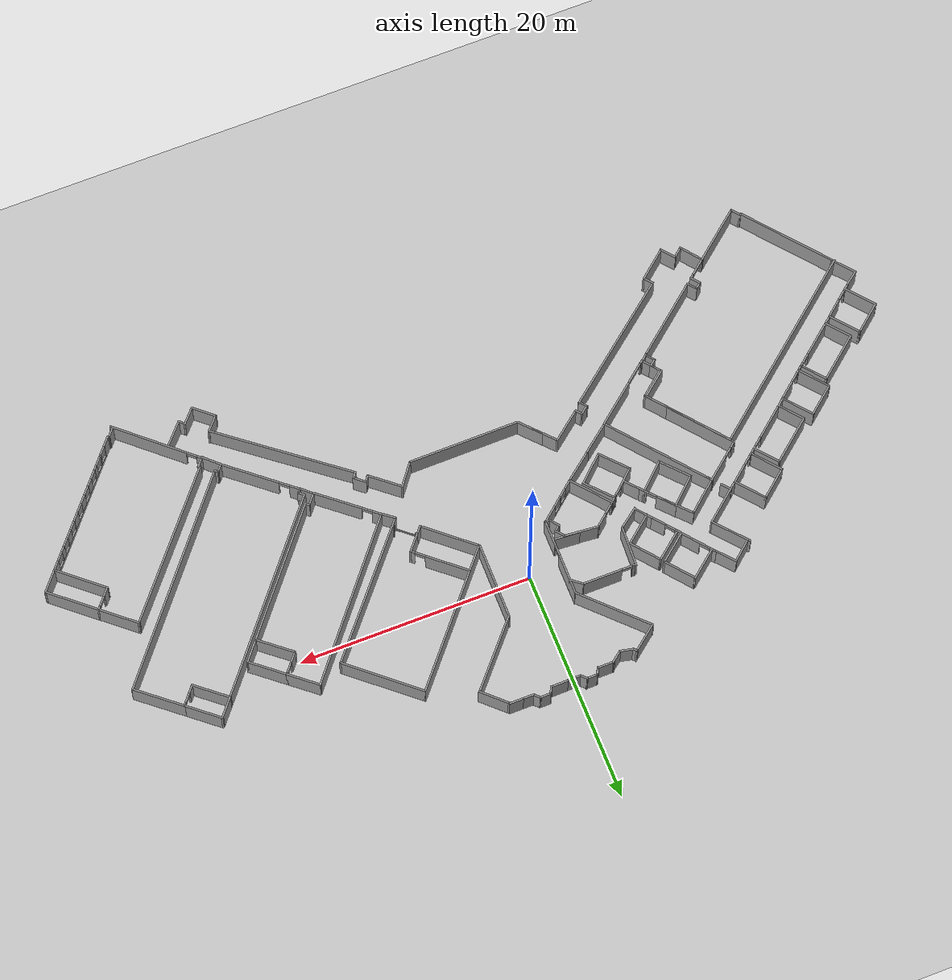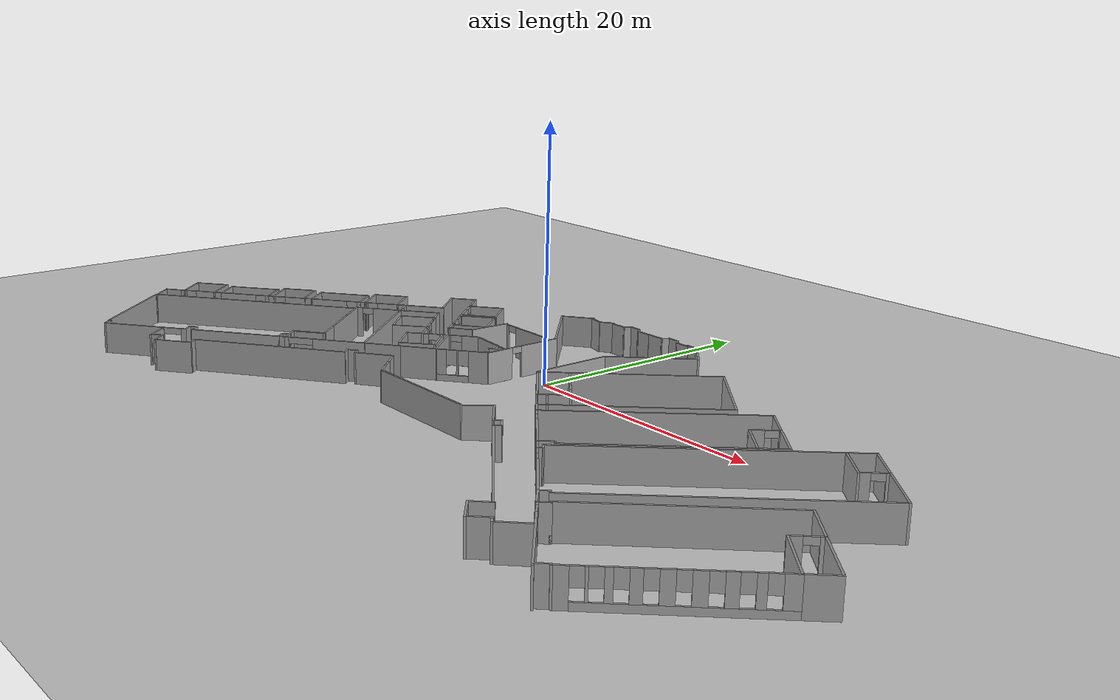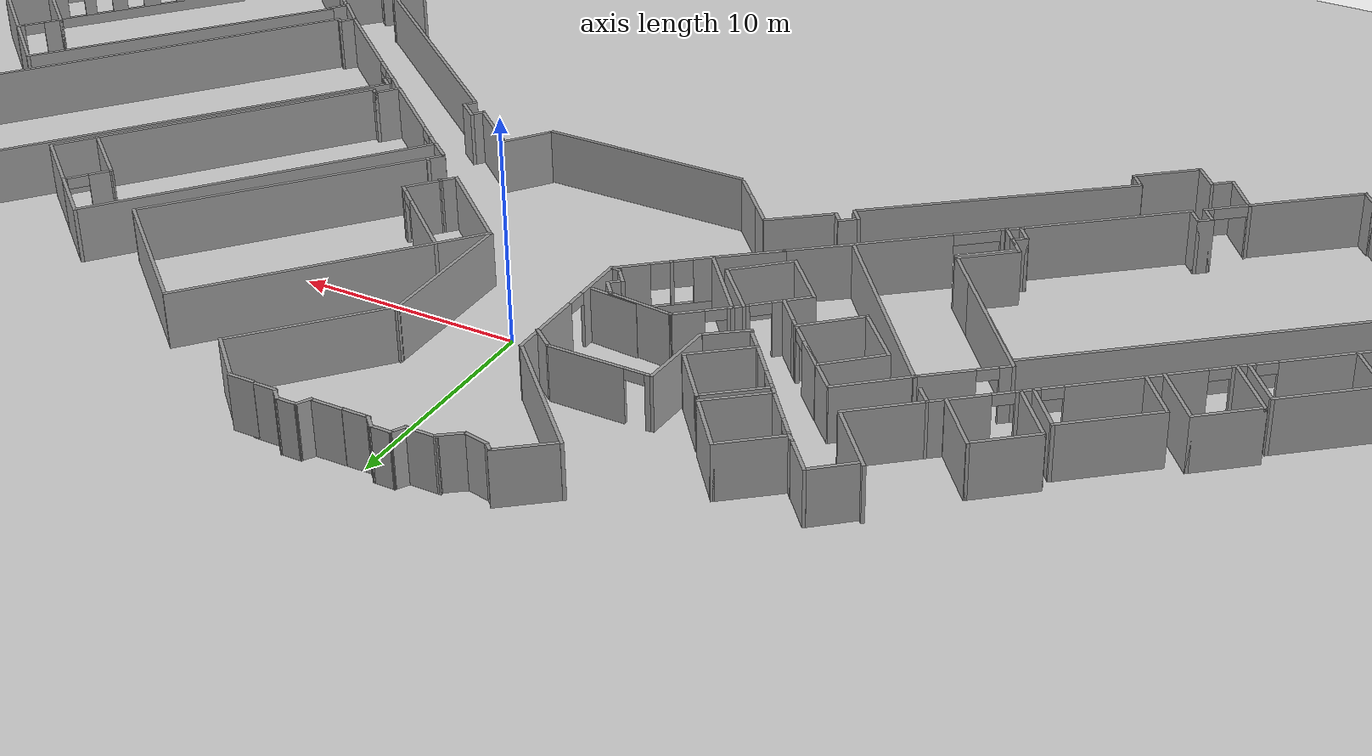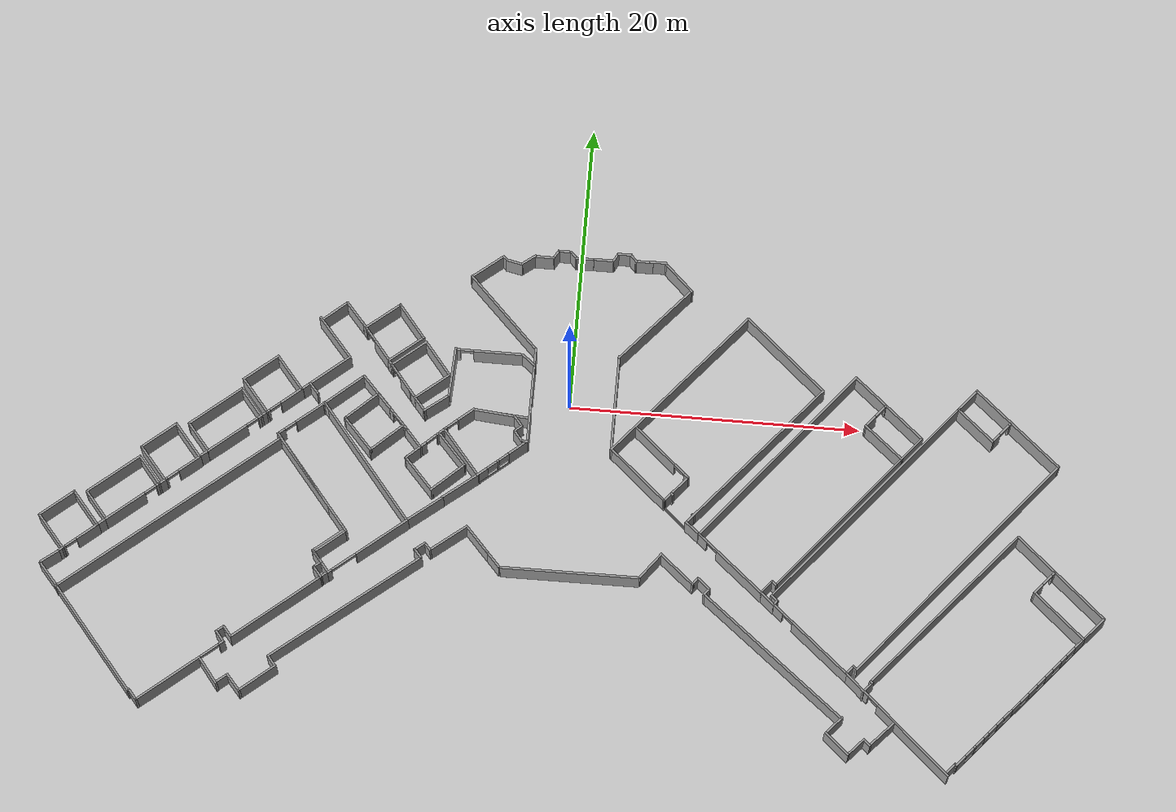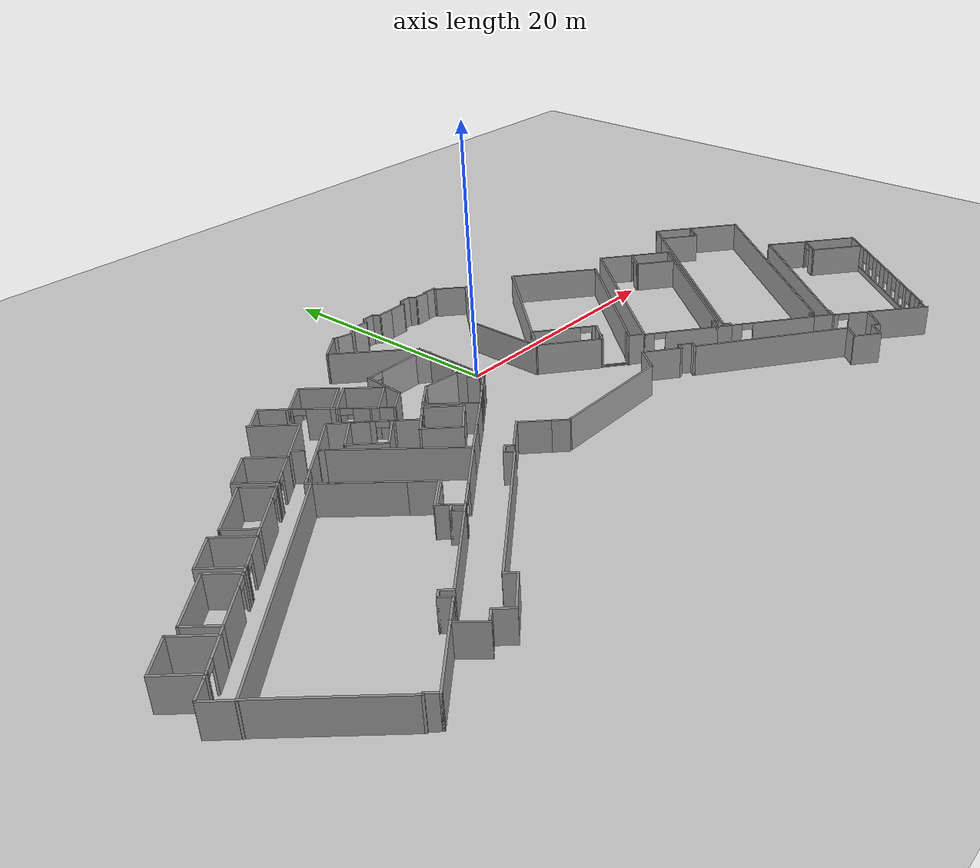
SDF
<sdf version="1.6">
 <world name="default">
  <light name="sun" type="directional">
   <pose>0 0 10 0 -0 0</pose>
   <diffuse>0.8 0.8 0.8 1</diffuse>
   <specular>0.2 0.2 0.2 1</specular>
   <attenuation>
    <range>1000</range>
    <constant>0.9</constant>
    <linear>0.01</linear>
    <quadratic>0.001</quadratic>
   </attenuation>
   <direction>-0.5 0.1 -0.9</direction>
  </light>
  <model name="ground_plane">
   <static>1</static>
   <link name="link">
    <collision name="collision">
     <geometry><plane><normal>0 0 1</normal><size>100 100</size></plane></geometry>
     <surface>
      <contact><collide_bitmask>65535</collide_bitmask></contact>
      <friction><ode><mu>100</mu><mu2>50</mu2></ode></friction>
     </surface>
    </collision>
    <visual name="visual">
     <cast_shadows>0</cast_shadows>
     <geometry><plane><normal>0 0 1</normal><size>100 100</size></plane></geometry>
     <material>
      <script><uri>file://media/materials/scripts/gazebo.material</uri><name>Gazebo/Grey</name></script>
     </material>
    </visual>
   </link>
  </model>
  <gravity>0 0 -9.8</gravity>
  <magnetic_field>6e-06 2.3e-05 -4.2e-05</magnetic_field>
  <atmosphere type="adiabatic"/>
  <physics name="default_physics" default="0" type="ode">
   <max_step_size>0.001</max_step_size>
   <real_time_factor>1</real_time_factor>
   <real_time_update_rate>1000</real_time_update_rate>
  </physics>
  <scene><ambient>0.4 0.4 0.4 1</ambient><background>0.7 0.7 0.7 1</background><shadows>1</shadows></scene>
  <audio><device>default</device></audio>
  <spherical_coordinates>
   <surface_model>EARTH_WGS84</surface_model>
   <latitude_deg>0</latitude_deg>
   <longitude_deg>0</longitude_deg>
   <elevation>0</elevation>
   <heading_deg>0</heading_deg>
  </spherical_coordinates>
  <model name="wall(6.75)_0_clone">
   <pose>3.09203 -0.032897 0 0 0 -1.5756</pose>
   <link name="Wall_106">
    <collision name="Wall_106_Collision">
     <geometry><box><size>6.75 0.15 2.5</size></box></geometry>
     <pose>0 0 1.25 0 -0 0</pose>
    </collision>
    <visual name="Wall_106_Visual">
     <pose>0 0 1.25 0 -0 0</pose>
     <geometry><box><size>6.75 0.15 2.5</size></box></geometry>
     <material>
      <script><uri>file://media/materials/scripts/gazebo.material</uri><name>Gazebo/Grey</name></script>
      <ambient>1 1 1 1</ambient>
     </material>
     <meta><layer>0</layer></meta>
    </visual>
   </link>
   <static>1</static>
  </model>
  <model name="wall(6.9)">
   <link name="Wall_106">
    <inertial>
     <mass>1</mass>
     <inertia><ixx>1</ixx><ixy>0</ixy><ixz>0</ixz><iyy>1</iyy><iyz>0</iyz><izz>1</izz></inertia>
    </inertial>
    <visual name="Wall_106_Visual">
     <pose>0 0 1.25 0 -0 0</pose>
     <geometry><box><size>6.9 0.15 2.5</size></box></geometry>
     <material>
      <script><uri>file://media/materials/scripts/gazebo.material</uri><name>Gazebo/Grey</name></script>
      <ambient>1 1 1 1</ambient>
      <shader type="vertex"><normal_map>__default__</normal_map></shader>
      <diffuse>0.7 0.7 0.7 1</diffuse>
      <specular>0.01 0.01 0.01 1</specular>
      <emissive>0 0 0 1</emissive>
     </material>
     <meta><layer>0</layer></meta>
    </visual>
    <collision name="Wall_106_Collision">
     <pose>0 0 1.25 0 -0 0</pose>
     <geometry><box><size>6.75 0.15 2.5</size></box></geometry>
     <surface>
      <friction>
       <ode><mu>1</mu><mu2>1</mu2><fdir1>0 0 0</fdir1><slip1>0</slip1><slip2>0</slip2></ode>
       <torsional>
        <coefficient>1</coefficient>
        <patch_radius>0</patch_radius>
        <surface_radius>0</surface_radius>
        <use_patch_radius>1</use_patch_radius>
        <ode><slip>0</slip></ode>
       </torsional>
      </friction>
      <bounce><restitution_coefficient>0</restitution_coefficient><threshold>1e+06</threshold></bounce>
      <contact>
       <collide_without_contact>0</collide_without_contact>
       <collide_without_contact_bitmask>1</collide_without_contact_bitmask>
       <collide_bitmask>1</collide_bitmask>
       <ode>
        <soft_cfm>0</soft_cfm>
        <soft_erp>0.2</soft_erp>
        <kp>1e+13</kp>
        <kd>1</kd>
        <max_vel>0.01</max_vel>
        <min_depth>0</min_depth>
       </ode>
       <bullet>
        <split_impulse>1</split_impulse>
        <split_impulse_penetration_threshold>-0.01</split_impulse_penetration_threshold>
        <soft_cfm>0</soft_cfm>
        <soft_erp>0.2</soft_erp>
        <kp>1e+13</kp>
        <kd>1</kd>
       </bullet>
      </contact>
     </surface>
    </collision>
   </link>
   <static>1</static>
   <pose>-5.08386 5.75321 0 0 0 -0.789714</pose>
  </model>
  <model name="wall_6.75">
   <pose>-6.43503 8.95426 0 0 -0 0.672508</pose>
   <link name="Wall_108">
    <collision name="Wall_108_Collision">
     <geometry><box><size>2.75 0.15 2.5</size></box></geometry>
     <pose>0 0 1.25 0 -0 0</pose>
    </collision>
    <visual name="Wall_108_Visual">
     <pose>0 0 1.25 0 -0 0</pose>
     <geometry><box><size>2.75 0.15 2.5</size></box></geometry>
     <material>
      <script><uri>file://media/materials/scripts/gazebo.material</uri><name>Gazebo/Grey</name></script>
      <ambient>1 1 1 1</ambient>
     </material>
     <meta><layer>0</layer></meta>
    </visual>
   </link>
   <link name="Wall_109">
    <collision name="Wall_109_Collision">
     <geometry><box><size>0.15 0.15 2.5</size></box></geometry>
     <pose>0 0 1.25 0 -0 0</pose>
    </collision>
    <visual name="Wall_109_Visual">
     <pose>0 0 1.25 0 -0 0</pose>
     <geometry><box><size>0.15 0.15 2.5</size></box></geometry>
     <material>
      <script><uri>file://media/materials/scripts/gazebo.material</uri><name>Gazebo/Grey</name></script>
      <ambient>0 0 0 1</ambient>
     </material>
     <meta><layer>0</layer></meta>
    </visual>
    <pose>1.3 0 0 0 -0 0</pose>
   </link>
   <static>1</static>
  </model>
  <model name="lift">
   <pose>-1.30167 10.2174 0 0 0 -3.13924</pose>
   <link name="Wall_113">
    <collision name="Wall_113_Collision">
     <geometry><box><size>1.5 0.15 2.5</size></box></geometry>
     <pose>0 0 1.25 0 -0 0</pose>
    </collision>
    <visual name="Wall_113_Visual">
     <pose>0 0 1.25 0 -0 0</pose>
     <geometry><box><size>1.5 0.15 2.5</size></box></geometry>
     <material>
      <script><uri>file://media/materials/scripts/gazebo.material</uri><name>Gazebo/Grey</name></script>
      <ambient>1 1 1 1</ambient>
     </material>
     <meta><layer>0</layer></meta>
    </visual>
    <pose>1.33713 0.261614 0 0 -0 3.14159</pose>
   </link>
   <link name="Wall_114">
    <collision name="Wall_114_Collision">
     <geometry><box><size>0.75 0.15 2.5</size></box></geometry>
     <pose>0 0 1.25 0 -0 0</pose>
    </collision>
    <visual name="Wall_114_Visual">
     <pose>0 0 1.25 0 -0 0</pose>
     <geometry><box><size>0.75 0.15 2.5</size></box></geometry>
     <material>
      <script><uri>file://media/materials/scripts/gazebo.material</uri><name>Gazebo/Grey</name></script>
      <ambient>1 1 1 1</ambient>
     </material>
     <meta><layer>0</layer></meta>
    </visual>
    <pose>0.512132 0.001807 0 0 -0 -2.0944</pose>
   </link>
   <link name="Wall_115">
    <collision name="Wall_115_Collision">
     <geometry><box><size>1 0.15 2.5</size></box></geometry>
     <pose>0 0 1.25 0 -0 0</pose>
    </collision>
    <visual name="Wall_115_Visual">
     <pose>0 0 1.25 0 -0 0</pose>
     <geometry><box><size>1 0.15 2.5</size></box></geometry>
     <material>
      <script><uri>file://media/materials/scripts/gazebo.material</uri><name>Gazebo/Grey</name></script>
      <ambient>1 1 1 1</ambient>
     </material>
     <meta><layer>0</layer></meta>
    </visual>
    <pose>-0.062868 -0.258001 0 0 -0 3.14159</pose>
   </link>
   <link name="Wall_116">
    <collision name="Wall_116_Collision">
     <geometry><box><size>0.75 0.15 2.5</size></box></geometry>
     <pose>0 0 1.25 0 -0 0</pose>
    </collision>
    <visual name="Wall_116_Visual">
     <pose>0 0 1.25 0 -0 0</pose>
     <geometry><box><size>0.75 0.15 2.5</size></box></geometry>
     <material>
      <script><uri>file://media/materials/scripts/gazebo.material</uri><name>Gazebo/Grey</name></script>
      <ambient>1 1 1 1</ambient>
     </material>
     <meta><layer>0</layer></meta>
    </visual>
    <pose>-0.7 -0.045868 0 0 -0 2.35619</pose>
   </link>
   <link name="Wall_117">
    <collision name="Wall_117_Collision">
     <geometry><box><size>1.25 0.15 2.5</size></box></geometry>
     <pose>0 0 1.25 0 -0 0</pose>
    </collision>
    <visual name="Wall_117_Visual">
     <pose>0 0 1.25 0 -0 0</pose>
     <geometry><box><size>1.25 0.15 2.5</size></box></geometry>
     <material>
      <script><uri>file://media/materials/scripts/gazebo.material</uri><name>Gazebo/Grey</name></script>
      <ambient>1 1 1 1</ambient>
     </material>
     <meta><layer>0</layer></meta>
    </visual>
    <pose>-1.46213 0.166263 0 0 -0 3.14159</pose>
   </link>
   <static>1</static>
  </model>
  <model name="lift_clone">
   <pose>2.81764 10.3434 0 0 0 -3.13924</pose>
   <link name="Wall_113">
    <collision name="Wall_113_Collision">
     <geometry><box><size>1.5 0.15 2.5</size></box></geometry>
     <pose>0 0 1.25 0 -0 0</pose>
    </collision>
    <visual name="Wall_113_Visual">
     <pose>0 0 1.25 0 -0 0</pose>
     <geometry><box><size>1.5 0.15 2.5</size></box></geometry>
     <material>
      <script><uri>file://media/materials/scripts/gazebo.material</uri><name>Gazebo/Grey</name></script>
      <ambient>1 1 1 1</ambient>
     </material>
     <meta><layer>0</layer></meta>
    </visual>
    <pose>1.33713 0.261614 0 0 -0 3.14159</pose>
   </link>
   <link name="Wall_114">
    <collision name="Wall_114_Collision">
     <geometry><box><size>0.75 0.15 2.5</size></box></geometry>
     <pose>0 0 1.25 0 -0 0</pose>
    </collision>
    <visual name="Wall_114_Visual">
     <pose>0 0 1.25 0 -0 0</pose>
     <geometry><box><size>0.75 0.15 2.5</size></box></geometry>
     <material>
      <script><uri>file://media/materials/scripts/gazebo.material</uri><name>Gazebo/Grey</name></script>
      <ambient>1 1 1 1</ambient>
     </material>
     <meta><layer>0</layer></meta>
    </visual>
    <pose>0.512132 0.001807 0 0 -0 -2.0944</pose>
   </link>
   <link name="Wall_115">
    <collision name="Wall_115_Collision">
     <geometry><box><size>1 0.15 2.5</size></box></geometry>
     <pose>0 0 1.25 0 -0 0</pose>
    </collision>
    <visual name="Wall_115_Visual">
     <pose>0 0 1.25 0 -0 0</pose>
     <geometry><box><size>1 0.15 2.5</size></box></geometry>
     <material>
      <script><uri>file://media/materials/scripts/gazebo.material</uri><name>Gazebo/Grey</name></script>
      <ambient>1 1 1 1</ambient>
     </material>
     <meta><layer>0</layer></meta>
    </visual>
    <pose>-0.062868 -0.258001 0 0 -0 3.14159</pose>
   </link>
   <link name="Wall_116">
    <collision name="Wall_116_Collision">
     <geometry><box><size>0.75 0.15 2.5</size></box></geometry>
     <pose>0 0 1.25 0 -0 0</pose>
    </collision>
    <visual name="Wall_116_Visual">
     <pose>0 0 1.25 0 -0 0</pose>
     <geometry><box><size>0.75 0.15 2.5</size></box></geometry>
     <material>
      <script><uri>file://media/materials/scripts/gazebo.material</uri><name>Gazebo/Grey</name></script>
      <ambient>1 1 1 1</ambient>
     </material>
     <meta><layer>0</layer></meta>
    </visual>
    <pose>-0.7 -0.045868 0 0 -0 2.35619</pose>
   </link>
   <link name="Wall_117">
    <collision name="Wall_117_Collision">
     <geometry><box><size>1.25 0.15 2.5</size></box></geometry>
     <pose>0 0 1.25 0 -0 0</pose>
    </collision>
    <visual name="Wall_117_Visual">
     <pose>0 0 1.25 0 -0 0</pose>
     <geometry><box><size>1.25 0.15 2.5</size></box></geometry>
     <material>
      <script><uri>file://media/materials/scripts/gazebo.material</uri><name>Gazebo/Grey</name></script>
      <ambient>1 1 1 1</ambient>
     </material>
     <meta><layer>0</layer></meta>
    </visual>
    <pose>-1.46213 0.166263 0 0 -0 3.14159</pose>
   </link>
   <static>1</static>
  </model>
  <model name="wall(6.9)_clone">
   <link name="Wall_106">
    <inertial>
     <mass>1</mass>
     <inertia><ixx>1</ixx><ixy>0</ixy><ixz>0</ixz><iyy>1</iyy><iyz>0</iyz><izz>1</izz></inertia>
    </inertial>
    <visual name="Wall_106_Visual">
     <pose>0 0 1.25 0 -0 0</pose>
     <geometry><box><size>6.9 0.15 2.5</size></box></geometry>
     <material>
      <script><uri>file://media/materials/scripts/gazebo.material</uri><name>Gazebo/Grey</name></script>
      <ambient>1 1 1 1</ambient>
      <shader type="vertex"><normal_map>__default__</normal_map></shader>
      <diffuse>0.7 0.7 0.7 1</diffuse>
      <specular>0.01 0.01 0.01 1</specular>
      <emissive>0 0 0 1</emissive>
     </material>
     <meta><layer>0</layer></meta>
    </visual>
    <collision name="Wall_106_Collision">
     <pose>0 0 1.25 0 -0 0</pose>
     <geometry><box><size>6.75 0.15 2.5</size></box></geometry>
     <surface>
      <friction>
       <ode><mu>1</mu><mu2>1</mu2><fdir1>0 0 0</fdir1><slip1>0</slip1><slip2>0</slip2></ode>
       <torsional>
        <coefficient>1</coefficient>
        <patch_radius>0</patch_radius>
        <surface_radius>0</surface_radius>
        <use_patch_radius>1</use_patch_radius>
        <ode><slip>0</slip></ode>
       </torsional>
      </friction>
      <bounce><restitution_coefficient>0</restitution_coefficient><threshold>1e+06</threshold></bounce>
      <contact>
       <collide_without_contact>0</collide_without_contact>
       <collide_without_contact_bitmask>1</collide_without_contact_bitmask>
       <collide_bitmask>1</collide_bitmask>
       <ode>
        <soft_cfm>0</soft_cfm>
        <soft_erp>0.2</soft_erp>
        <kp>1e+13</kp>
        <kd>1</kd>
        <max_vel>0.01</max_vel>
        <min_depth>0</min_depth>
       </ode>
       <bullet>
        <split_impulse>1</split_impulse>
        <split_impulse_penetration_threshold>-0.01</split_impulse_penetration_threshold>
        <soft_cfm>0</soft_cfm>
        <soft_erp>0.2</soft_erp>
        <kp>1e+13</kp>
        <kd>1</kd>
       </bullet>
      </contact>
     </surface>
    </collision>
   </link>
   <static>1</static>
   <pose>5.35911 5.71378 0 0 0 -2.29576</pose>
  </model>
  <model name="wall_6.75_clone">
   <pose>6.76863 9.22687 0 0 -0 2.38301</pose>
   <link name="Wall_108">
    <collision name="Wall_108_Collision">
     <geometry><box><size>2.75 0.15 2.5</size></box></geometry>
     <pose>0 0 1.25 0 -0 0</pose>
    </collision>
    <visual name="Wall_108_Visual">
     <pose>0 0 1.25 0 -0 0</pose>
     <geometry><box><size>2.75 0.15 2.5</size></box></geometry>
     <material>
      <script><uri>file://media/materials/scripts/gazebo.material</uri><name>Gazebo/Grey</name></script>
      <ambient>1 1 1 1</ambient>
     </material>
     <meta><layer>0</layer></meta>
    </visual>
   </link>
   <link name="Wall_109">
    <collision name="Wall_109_Collision">
     <geometry><box><size>0.15 0.15 2.5</size></box></geometry>
     <pose>0 0 1.25 0 -0 0</pose>
    </collision>
    <visual name="Wall_109_Visual">
     <pose>0 0 1.25 0 -0 0</pose>
     <geometry><box><size>0.15 0.15 2.5</size></box></geometry>
     <material>
      <script><uri>file://media/materials/scripts/gazebo.material</uri><name>Gazebo/Grey</name></script>
      <ambient>0 0 0 1</ambient>
     </material>
     <meta><layer>0</layer></meta>
    </visual>
    <pose>1.3 0 0 0 -0 0</pose>
   </link>
   <static>1</static>
  </model>
  <model name="1804">
   <pose>10.1904 -0.701306 0 0 0 -0.710113</pose>
   <link name="Stairs_1">
    <visual name="Stairs_1_Visual_0">
     <pose>2.5799 -6.58604 0.0375 0 -0 -3.14159</pose>
     <geometry><box><size>2.12 0.075 0.075</size></box></geometry>
     <material>
      <script><uri>file://media/materials/scripts/gazebo.material</uri><name>Gazebo/Grey</name></script>
      <ambient>1 1 1 1</ambient>
     </material>
     <meta><layer>0</layer></meta>
    </visual>
    <collision name="Stairs_1_Collision_0">
     <geometry><box><size>2.12 0.075 0.075</size></box></geometry>
     <pose>2.5799 -6.58604 0.0375 0 -0 -3.14159</pose>
    </collision>
    <visual name="Stairs_1_Visual_1">
     <pose>2.5799 -6.51104 0.1125 0 -0 -3.14159</pose>
     <geometry><box><size>2.12 0.075 0.075</size></box></geometry>
     <material>
      <script><uri>file://media/materials/scripts/gazebo.material</uri><name>Gazebo/Grey</name></script>
      <ambient>1 1 1 1</ambient>
     </material>
     <meta><layer>0</layer></meta>
    </visual>
    <collision name="Stairs_1_Collision_1">
     <geometry><box><size>2.12 0.075 0.075</size></box></geometry>
     <pose>2.5799 -6.51104 0.1125 0 -0 -3.14159</pose>
    </collision>
   </link>
   <link name="Wall_40">
    <collision name="Wall_40_Collision">
     <geometry><box><size>5.25 0.15 2.5</size></box></geometry>
     <pose>0 0 1.25 0 -0 0</pose>
    </collision>
    <visual name="Wall_40_Visual">
     <pose>0 0 1.25 0 -0 0</pose>
     <geometry><box><size>5.25 0.15 2.5</size></box></geometry>
     <material>
      <script><uri>file://media/materials/scripts/gazebo.material</uri><name>Gazebo/Grey</name></script>
      <ambient>1 1 1 1</ambient>
     </material>
     <meta><layer>0</layer></meta>
    </visual>
    <pose>-1.0762 -6.6225 0 0 -0 3.14159</pose>
   </link>
   <link name="Wall_41">
    <collision name="Wall_41_Collision">
     <geometry><box><size>13.395 0.15 2.5</size></box></geometry>
     <pose>0 0 1.25 0 -0 0</pose>
    </collision>
    <visual name="Wall_41_Visual">
     <pose>0 0 1.25 0 -0 0</pose>
     <geometry><box><size>13.395 0.15 2.5</size></box></geometry>
     <material>
      <script><uri>file://media/materials/scripts/gazebo.material</uri><name>Gazebo/Grey</name></script>
      <ambient>1 1 1 1</ambient>
     </material>
     <meta><layer>0</layer></meta>
    </visual>
    <pose>-3.6262 0 0 0 -0 1.5708</pose>
   </link>
   <link name="Wall_42">
    <collision name="Wall_42_Collision">
     <geometry><box><size>7.397 0.15 2.5</size></box></geometry>
     <pose>0 0 1.25 0 -0 0</pose>
    </collision>
    <visual name="Wall_42_Visual">
     <pose>0 0 1.25 0 -0 0</pose>
     <geometry><box><size>7.397 0.15 2.5</size></box></geometry>
     <material>
      <script><uri>file://media/materials/scripts/gazebo.material</uri><name>Gazebo/Grey</name></script>
      <ambient>1 1 1 1</ambient>
     </material>
     <meta><layer>0</layer></meta>
    </visual>
    <pose>-0.002699 6.6225 0 0 -0 0</pose>
   </link>
   <link name="Wall_43">
    <collision name="Wall_43_Collision">
     <geometry><box><size>13.3954 0.15 2.5</size></box></geometry>
     <pose>0 0 1.25 0 -0 0</pose>
    </collision>
    <visual name="Wall_43_Visual">
     <pose>0 0 1.25 0 -0 0</pose>
     <geometry><box><size>13.3954 0.15 2.5</size></box></geometry>
     <material>
      <script><uri>file://media/materials/scripts/gazebo.material</uri><name>Gazebo/Grey</name></script>
      <ambient>1 1 1 1</ambient>
     </material>
     <meta><layer>0</layer></meta>
    </visual>
    <pose>3.6208 0 0 0 -0 -1.5708</pose>
   </link>
   <link name="Wall_45">
    <collision name="Wall_45_Collision">
     <geometry><box><size>0.854548 0.15 2.5</size></box></geometry>
     <pose>0 0 1.25 0 -0 0</pose>
    </collision>
    <visual name="Wall_45_Visual">
     <pose>0 0 1.25 0 -0 0</pose>
     <geometry><box><size>0.854548 0.15 2.5</size></box></geometry>
     <material>
      <script><uri>file://media/materials/scripts/gazebo.material</uri><name>Gazebo/Grey</name></script>
      <ambient>1 1 1 1</ambient>
     </material>
     <meta><layer>0</layer></meta>
    </visual>
    <pose>1.47361 -6.27023 0 0 -0 1.57135</pose>
   </link>
   <link name="Wall_46">
    <collision name="Wall_46_Collision">
     <geometry><box><size>0.25 0.15 2.5</size></box></geometry>
     <pose>0 0 1.25 0 -0 0</pose>
    </collision>
    <visual name="Wall_46_Visual">
     <pose>0 0 1.25 0 -0 0</pose>
     <geometry><box><size>0.25 0.15 2.5</size></box></geometry>
     <material>
      <script><uri>file://media/materials/scripts/gazebo.material</uri><name>Gazebo/Grey</name></script>
      <ambient>1 1 1 1</ambient>
     </material>
     <meta><layer>0</layer></meta>
    </visual>
    <pose>1.52341 -5.91795 0 0 -0 0</pose>
   </link>
   <link name="Wall_48">
    <collision name="Wall_48_Collision">
     <geometry><box><size>0.25 0.15 2.5</size></box></geometry>
     <pose>0 0 1.25 0 -0 0</pose>
    </collision>
    <visual name="Wall_48_Visual">
     <pose>0 0 1.25 0 -0 0</pose>
     <geometry><box><size>0.25 0.15 2.5</size></box></geometry>
     <material>
      <script><uri>file://media/materials/scripts/gazebo.material</uri><name>Gazebo/Grey</name></script>
      <ambient>1 1 1 1</ambient>
     </material>
     <meta><layer>0</layer></meta>
    </visual>
    <pose>3.57659 -5.92481 0 0 -0 0</pose>
   </link>
   <link name="Wall_50">
    <collision name="Wall_50_Collision">
     <geometry><box><size>1.75 0.15 2.5</size></box></geometry>
     <pose>0 0 1.25 0 -0 0</pose>
    </collision>
    <visual name="Wall_50_Visual">
     <pose>0 0 1.25 0 -0 0</pose>
     <geometry><box><size>1.75 0.15 2.5</size></box></geometry>
     <material>
      <script><uri>file://media/materials/scripts/gazebo.material</uri><name>Gazebo/Grey</name></script>
      <ambient>1 1 1 1</ambient>
     </material>
     <meta><layer>0</layer></meta>
    </visual>
    <pose>1.47341 -5.11795 0 0 -0 1.5708</pose>
   </link>
   <link name="Wall_51">
    <pose>-1.07659 -4.31795 0 0 -0 3.14159</pose>
    <visual name="Wall_51_Visual_0">
     <pose>-2.40355 0 1.25 0 -0 0</pose>
     <geometry><box><size>0.442906 0.15 2.5</size></box></geometry>
     <material>
      <script><uri>file://media/materials/scripts/gazebo.material</uri><name>Gazebo/Grey</name></script>
      <ambient>1 1 1 1</ambient>
     </material>
     <meta><layer>0</layer></meta>
    </visual>
    <collision name="Wall_51_Collision_0">
     <geometry><box><size>0.442906 0.15 2.5</size></box></geometry>
     <pose>-2.40355 0 1.25 0 -0 0</pose>
    </collision>
    <visual name="Wall_51_Visual_1">
     <pose>0.671453 0 1.25 0 -0 0</pose>
     <geometry><box><size>3.90709 0.15 2.5</size></box></geometry>
     <material>
      <script><uri>file://media/materials/scripts/gazebo.material</uri><name>Gazebo/Grey</name></script>
      <ambient>1 1 1 1</ambient>
     </material>
     <meta><layer>0</layer></meta>
    </visual>
    <collision name="Wall_51_Collision_1">
     <geometry><box><size>3.90709 0.15 2.5</size></box></geometry>
     <pose>0.671453 0 1.25 0 -0 0</pose>
    </collision>
    <visual name="Wall_51_Visual_2">
     <pose>-1.73209 0 2.25 0 -0 0</pose>
     <geometry><box><size>0.9 0.15 0.5</size></box></geometry>
     <material>
      <script><uri>file://media/materials/scripts/gazebo.material</uri><name>Gazebo/Grey</name></script>
      <ambient>1 1 1 1</ambient>
     </material>
     <meta><layer>0</layer></meta>
    </visual>
    <collision name="Wall_51_Collision_2">
     <geometry><box><size>0.9 0.15 0.5</size></box></geometry>
     <pose>-1.73209 0 2.25 0 -0 0</pose>
    </collision>
   </link>
   <static>1</static>
  </model>
  <model name="1802">
   <pose>24.1192 -7.53078 0 0 -0 2.44606</pose>
   <link name="Wall_100">
    <collision name="Wall_100_Collision">
     <geometry><box><size>3.3883 0.15 2.5</size></box></geometry>
     <pose>0 0 1.25 0 -0 0</pose>
    </collision>
    <visual name="Wall_100_Visual">
     <pose>0 0 1.25 0 -0 0</pose>
     <geometry><box><size>3.3883 0.15 2.5</size></box></geometry>
     <material>
      <script><uri>file://media/materials/scripts/gazebo.material</uri><name>Gazebo/Grey</name></script>
      <ambient>1 1 1 1</ambient>
     </material>
     <meta><layer>0</layer></meta>
    </visual>
    <pose>2.21705 -8.45439 0 0 -0 3.14159</pose>
   </link>
   <link name="Wall_101">
    <pose>0.598047 -9.40484 0 0 -0 -1.57085</pose>
    <visual name="Wall_101_Visual_0">
     <pose>-0.610406 0 1.25 0 -0 0</pose>
     <geometry><box><size>0.728286 0.15 2.5</size></box></geometry>
     <material>
      <script><uri>file://media/materials/scripts/gazebo.material</uri><name>Gazebo/Grey</name></script>
      <ambient>1 1 1 1</ambient>
     </material>
     <meta><layer>0</layer></meta>
    </visual>
    <collision name="Wall_101_Collision_0">
     <geometry><box><size>0.728286 0.15 2.5</size></box></geometry>
     <pose>-0.610406 0 1.25 0 -0 0</pose>
    </collision>
    <visual name="Wall_101_Visual_1">
     <pose>0.814143 0 1.25 0 -0 0</pose>
     <geometry><box><size>0.320812 0.15 2.5</size></box></geometry>
     <material>
      <script><uri>file://media/materials/scripts/gazebo.material</uri><name>Gazebo/Grey</name></script>
      <ambient>1 1 1 1</ambient>
     </material>
     <meta><layer>0</layer></meta>
    </visual>
    <collision name="Wall_101_Collision_1">
     <geometry><box><size>0.320812 0.15 2.5</size></box></geometry>
     <pose>0.814143 0 1.25 0 -0 0</pose>
    </collision>
    <visual name="Wall_101_Visual_2">
     <pose>0.203737 0 2.25 0 -0 0</pose>
     <geometry><box><size>0.9 0.15 0.5</size></box></geometry>
     <material>
      <script><uri>file://media/materials/scripts/gazebo.material</uri><name>Gazebo/Grey</name></script>
      <ambient>1 1 1 1</ambient>
     </material>
     <meta><layer>0</layer></meta>
    </visual>
    <collision name="Wall_101_Collision_2">
     <geometry><box><size>0.9 0.15 0.5</size></box></geometry>
     <pose>0.203737 0 2.25 0 -0 0</pose>
    </collision>
   </link>
   <link name="Wall_102">
    <collision name="Wall_102_Collision">
     <geometry><box><size>4.58439 0.15 2.5</size></box></geometry>
     <pose>0 0 1.25 0 -0 0</pose>
    </collision>
    <visual name="Wall_102_Visual">
     <pose>0 0 1.25 0 -0 0</pose>
     <geometry><box><size>4.58439 0.15 2.5</size></box></geometry>
     <material>
      <script><uri>file://media/materials/scripts/gazebo.material</uri><name>Gazebo/Grey</name></script>
      <ambient>1 1 1 1</ambient>
     </material>
     <meta><layer>0</layer></meta>
    </visual>
    <pose>-1.619 -10.3044 0 0 -0 3.14159</pose>
   </link>
   <link name="Wall_103">
    <collision name="Wall_103_Collision">
     <geometry><box><size>20.059 0.15 2.5</size></box></geometry>
     <pose>0 0 1.25 0 -0 0</pose>
    </collision>
    <visual name="Wall_103_Visual">
     <pose>0 0 1.25 0 -0 0</pose>
     <geometry><box><size>20.059 0.15 2.5</size></box></geometry>
     <material>
      <script><uri>file://media/materials/scripts/gazebo.material</uri><name>Gazebo/Grey</name></script>
      <ambient>1 1 1 1</ambient>
     </material>
     <meta><layer>0</layer></meta>
    </visual>
    <pose>-3.836 -0.349889 0 0 -0 1.5708</pose>
   </link>
   <link name="Wall_104">
    <collision name="Wall_104_Collision">
     <geometry><box><size>0.445 0.15 2.5</size></box></geometry>
     <pose>0 0 1.25 0 -0 0</pose>
    </collision>
    <visual name="Wall_104_Visual">
     <pose>0 0 1.25 0 -0 0</pose>
     <geometry><box><size>0.445 0.15 2.5</size></box></geometry>
     <material>
      <script><uri>file://media/materials/scripts/gazebo.material</uri><name>Gazebo/Grey</name></script>
      <ambient>1 1 1 1</ambient>
     </material>
     <meta><layer>0</layer></meta>
    </visual>
    <pose>-3.6885 9.60461 0 0 -0 0</pose>
   </link>
   <link name="Wall_106">
    <collision name="Wall_106_Collision">
     <geometry><box><size>0.849769 0.15 2.5</size></box></geometry>
     <pose>0 0 1.25 0 -0 0</pose>
    </collision>
    <visual name="Wall_106_Visual">
     <pose>0 0 1.25 0 -0 0</pose>
     <geometry><box><size>0.849769 0.15 2.5</size></box></geometry>
     <material>
      <script><uri>file://media/materials/scripts/gazebo.material</uri><name>Gazebo/Grey</name></script>
      <ambient>1 1 1 1</ambient>
     </material>
     <meta><layer>0</layer></meta>
    </visual>
    <pose>-3.54093 9.95449 0 0 -0 1.57059</pose>
   </link>
   <link name="Wall_114">
    <collision name="Wall_114_Collision">
     <geometry><box><size>2 0.15 2.5</size></box></geometry>
     <pose>0 0 1.25 0 -0 0</pose>
    </collision>
    <visual name="Wall_114_Visual">
     <pose>0 0 1.25 0 -0 0</pose>
     <geometry><box><size>2 0.15 2.5</size></box></geometry>
     <material>
      <script><uri>file://media/materials/scripts/gazebo.material</uri><name>Gazebo/Grey</name></script>
      <ambient>1 1 1 1</ambient>
     </material>
     <meta><layer>0</layer></meta>
    </visual>
    <pose>3.836 -9.37929 0 0 -0 -1.5708</pose>
   </link>
   <link name="Wall_116">
    <collision name="Wall_116_Collision">
     <geometry><box><size>3.3883 0.15 2.5</size></box></geometry>
     <pose>0 0 1.25 0 -0 0</pose>
    </collision>
    <visual name="Wall_116_Visual">
     <pose>0 0 1.25 0 -0 0</pose>
     <geometry><box><size>3.3883 0.15 2.5</size></box></geometry>
     <material>
      <script><uri>file://media/materials/scripts/gazebo.material</uri><name>Gazebo/Grey</name></script>
      <ambient>1 1 1 1</ambient>
     </material>
     <meta><layer>0</layer></meta>
    </visual>
    <pose>2.217 -10.3043 0 0 -0 -3.14153</pose>
   </link>
   <link name="Wall_93">
    <pose>-0.115858 10.3044 0 0 -0 0</pose>
    <visual name="Wall_93_Visual_0">
     <pose>-0.934826 0 1.25 0 -0 0</pose>
     <geometry><box><size>5.13035 0.15 2.5</size></box></geometry>
     <material>
      <script><uri>file://media/materials/scripts/gazebo.material</uri><name>Gazebo/Grey</name></script>
      <ambient>1 1 1 1</ambient>
     </material>
     <meta><layer>0</layer></meta>
    </visual>
    <collision name="Wall_93_Collision_0">
     <geometry><box><size>5.13035 0.15 2.5</size></box></geometry>
     <pose>-0.934826 0 1.25 0 -0 0</pose>
    </collision>
    <visual name="Wall_93_Visual_1">
     <pose>3.01517 0 1.25 0 -0 0</pose>
     <geometry><box><size>0.969653 0.15 2.5</size></box></geometry>
     <material>
      <script><uri>file://media/materials/scripts/gazebo.material</uri><name>Gazebo/Grey</name></script>
      <ambient>1 1 1 1</ambient>
     </material>
     <meta><layer>0</layer></meta>
    </visual>
    <collision name="Wall_93_Collision_1">
     <geometry><box><size>0.969653 0.15 2.5</size></box></geometry>
     <pose>3.01517 0 1.25 0 -0 0</pose>
    </collision>
    <visual name="Wall_93_Visual_2">
     <pose>2.08035 0 2.25 0 -0 0</pose>
     <geometry><box><size>0.9 0.15 0.5</size></box></geometry>
     <material>
      <script><uri>file://media/materials/scripts/gazebo.material</uri><name>Gazebo/Grey</name></script>
      <ambient>1 1 1 1</ambient>
     </material>
     <meta><layer>0</layer></meta>
    </visual>
    <collision name="Wall_93_Collision_2">
     <geometry><box><size>0.9 0.15 0.5</size></box></geometry>
     <pose>2.08035 0 2.25 0 -0 0</pose>
    </collision>
   </link>
   <link name="Wall_94">
    <collision name="Wall_94_Collision">
     <geometry><box><size>0.5 0.15 2.5</size></box></geometry>
     <pose>0 0 1.25 0 -0 0</pose>
    </collision>
    <visual name="Wall_94_Visual">
     <pose>0 0 1.25 0 -0 0</pose>
     <geometry><box><size>0.5 0.15 2.5</size></box></geometry>
     <material>
      <script><uri>file://media/materials/scripts/gazebo.material</uri><name>Gazebo/Grey</name></script>
      <ambient>1 1 1 1</ambient>
     </material>
     <meta><layer>0</layer></meta>
    </visual>
    <pose>3.30914 10.1294 0 0 -0 -1.5708</pose>
   </link>
   <link name="Wall_95">
    <collision name="Wall_95_Collision">
     <geometry><box><size>0.676857 0.15 2.5</size></box></geometry>
     <pose>0 0 1.25 0 -0 0</pose>
    </collision>
    <visual name="Wall_95_Visual">
     <pose>0 0 1.25 0 -0 0</pose>
     <geometry><box><size>0.676857 0.15 2.5</size></box></geometry>
     <material>
      <script><uri>file://media/materials/scripts/gazebo.material</uri><name>Gazebo/Grey</name></script>
      <ambient>1 1 1 1</ambient>
     </material>
     <meta><layer>0</layer></meta>
    </visual>
    <pose>3.57257 9.95449 0 0 -0 0.000439</pose>
   </link>
   <link name="Wall_99">
    <collision name="Wall_99_Collision">
     <geometry><box><size>18.5597 0.15 2.5</size></box></geometry>
     <pose>0 0 1.25 0 -0 0</pose>
    </collision>
    <visual name="Wall_99_Visual">
     <pose>0 0 1.25 0 -0 0</pose>
     <geometry><box><size>18.5597 0.15 2.5</size></box></geometry>
     <material>
      <script><uri>file://media/materials/scripts/gazebo.material</uri><name>Gazebo/Grey</name></script>
      <ambient>1 1 1 1</ambient>
     </material>
     <meta><layer>0</layer></meta>
    </visual>
    <pose>3.836 0.750111 0 0 -0 -1.5708</pose>
   </link>
   <static>1</static>
  </model>
  <model name="1801_new">
   <link name="Wall_23">
    <pose>3.9053 7.17484 0 0 0 -1.5708</pose>
    <visual name="Wall_23_Visual">
     <pose>0 0 1.25 0 -0 0</pose>
     <geometry><box><size>1 0.15 2.5</size></box></geometry>
     <material>
      <script><uri>file://media/materials/scripts/gazebo.material</uri><name>Gazebo/Grey</name></script>
      <ambient>1 1 1 1</ambient>
     </material>
     <meta><layer>0</layer></meta>
    </visual>
    <collision name="Wall_23_Collision">
     <pose>0 0 1.25 0 -0 0</pose>
     <geometry><box><size>1 0.15 2.5</size></box></geometry>
     <surface>
      <friction>
       <ode><mu>1</mu><mu2>1</mu2><fdir1>0 0 0</fdir1><slip1>0</slip1><slip2>0</slip2></ode>
       <torsional>
        <coefficient>1</coefficient>
        <patch_radius>0</patch_radius>
        <surface_radius>0</surface_radius>
        <use_patch_radius>1</use_patch_radius>
        <ode><slip>0</slip></ode>
       </torsional>
      </friction>
      <bounce><restitution_coefficient>0</restitution_coefficient><threshold>1e+06</threshold></bounce>
      <contact>
       <collide_without_contact>0</collide_without_contact>
       <collide_without_contact_bitmask>1</collide_without_contact_bitmask>
       <collide_bitmask>1</collide_bitmask>
       <ode>
        <soft_cfm>0</soft_cfm>
        <soft_erp>0.2</soft_erp>
        <kp>1e+13</kp>
        <kd>1</kd>
        <max_vel>0.01</max_vel>
        <min_depth>0</min_depth>
       </ode>
       <bullet>
        <split_impulse>1</split_impulse>
        <split_impulse_penetration_threshold>-0.01</split_impulse_penetration_threshold>
        <soft_cfm>0</soft_cfm>
        <soft_erp>0.2</soft_erp>
        <kp>1e+13</kp>
        <kd>1</kd>
       </bullet>
      </contact>
     </surface>
    </collision>
   </link>
   <link name="Wall_25">
    <pose>3.9553 6.74984 0 0 -0 0</pose>
    <visual name="Wall_25_Visual">
     <pose>0 0 1.25 0 -0 0</pose>
     <geometry><box><size>0.25 0.15 2.5</size></box></geometry>
     <material>
      <script><uri>file://media/materials/scripts/gazebo.material</uri><name>Gazebo/Grey</name></script>
      <ambient>1 1 1 1</ambient>
     </material>
     <meta><layer>0</layer></meta>
    </visual>
    <collision name="Wall_25_Collision">
     <pose>0 0 1.25 0 -0 0</pose>
     <geometry><box><size>0.25 0.15 2.5</size></box></geometry>
     <surface>
      <friction>
       <ode><mu>1</mu><mu2>1</mu2><fdir1>0 0 0</fdir1><slip1>0</slip1><slip2>0</slip2></ode>
       <torsional>
        <coefficient>1</coefficient>
        <patch_radius>0</patch_radius>
        <surface_radius>0</surface_radius>
        <use_patch_radius>1</use_patch_radius>
        <ode><slip>0</slip></ode>
       </torsional>
      </friction>
      <bounce><restitution_coefficient>0</restitution_coefficient><threshold>1e+06</threshold></bounce>
      <contact>
       <collide_without_contact>0</collide_without_contact>
       <collide_without_contact_bitmask>1</collide_without_contact_bitmask>
       <collide_bitmask>1</collide_bitmask>
       <ode>
        <soft_cfm>0</soft_cfm>
        <soft_erp>0.2</soft_erp>
        <kp>1e+13</kp>
        <kd>1</kd>
        <max_vel>0.01</max_vel>
        <min_depth>0</min_depth>
       </ode>
       <bullet>
        <split_impulse>1</split_impulse>
        <split_impulse_penetration_threshold>-0.01</split_impulse_penetration_threshold>
        <soft_cfm>0</soft_cfm>
        <soft_erp>0.2</soft_erp>
        <kp>1e+13</kp>
        <kd>1</kd>
       </bullet>
      </contact>
     </surface>
    </collision>
   </link>
   <link name="Wall_27">
    <pose>-3.9447 7.17484 0 0 0 -1.5708</pose>
    <visual name="Wall_27_Visual">
     <pose>0 0 1.25 0 -0 0</pose>
     <geometry><box><size>1 0.15 2.5</size></box></geometry>
     <material>
      <script><uri>file://media/materials/scripts/gazebo.material</uri><name>Gazebo/Grey</name></script>
      <ambient>1 1 1 1</ambient>
     </material>
     <meta><layer>0</layer></meta>
    </visual>
    <collision name="Wall_27_Collision">
     <pose>0 0 1.25 0 -0 0</pose>
     <geometry><box><size>1 0.15 2.5</size></box></geometry>
     <surface>
      <friction>
       <ode><mu>1</mu><mu2>1</mu2><fdir1>0 0 0</fdir1><slip1>0</slip1><slip2>0</slip2></ode>
       <torsional>
        <coefficient>1</coefficient>
        <patch_radius>0</patch_radius>
        <surface_radius>0</surface_radius>
        <use_patch_radius>1</use_patch_radius>
        <ode><slip>0</slip></ode>
       </torsional>
      </friction>
      <bounce><restitution_coefficient>0</restitution_coefficient><threshold>1e+06</threshold></bounce>
      <contact>
       <collide_without_contact>0</collide_without_contact>
       <collide_without_contact_bitmask>1</collide_without_contact_bitmask>
       <collide_bitmask>1</collide_bitmask>
       <ode>
        <soft_cfm>0</soft_cfm>
        <soft_erp>0.2</soft_erp>
        <kp>1e+13</kp>
        <kd>1</kd>
        <max_vel>0.01</max_vel>
        <min_depth>0</min_depth>
       </ode>
       <bullet>
        <split_impulse>1</split_impulse>
        <split_impulse_penetration_threshold>-0.01</split_impulse_penetration_threshold>
        <soft_cfm>0</soft_cfm>
        <soft_erp>0.2</soft_erp>
        <kp>1e+13</kp>
        <kd>1</kd>
       </bullet>
      </contact>
     </surface>
    </collision>
   </link>
   <link name="Wall_28">
    <pose>-3.99448 6.75002 0 0 -0 3.13811</pose>
    <visual name="Wall_28_Visual">
     <pose>0 0 1.25 0 -0 0</pose>
     <geometry><box><size>0.25 0.15 2.5</size></box></geometry>
     <material>
      <script><uri>file://media/materials/scripts/gazebo.material</uri><name>Gazebo/Grey</name></script>
      <ambient>1 1 1 1</ambient>
     </material>
     <meta><layer>0</layer></meta>
    </visual>
    <collision name="Wall_28_Collision">
     <pose>0 0 1.25 0 -0 0</pose>
     <geometry><box><size>0.25 0.15 2.5</size></box></geometry>
     <surface>
      <friction>
       <ode><mu>1</mu><mu2>1</mu2><fdir1>0 0 0</fdir1><slip1>0</slip1><slip2>0</slip2></ode>
       <torsional>
        <coefficient>1</coefficient>
        <patch_radius>0</patch_radius>
        <surface_radius>0</surface_radius>
        <use_patch_radius>1</use_patch_radius>
        <ode><slip>0</slip></ode>
       </torsional>
      </friction>
      <bounce><restitution_coefficient>0</restitution_coefficient><threshold>1e+06</threshold></bounce>
      <contact>
       <collide_without_contact>0</collide_without_contact>
       <collide_without_contact_bitmask>1</collide_without_contact_bitmask>
       <collide_bitmask>1</collide_bitmask>
       <ode>
        <soft_cfm>0</soft_cfm>
        <soft_erp>0.2</soft_erp>
        <kp>1e+13</kp>
        <kd>1</kd>
        <max_vel>0.01</max_vel>
        <min_depth>0</min_depth>
       </ode>
       <bullet>
        <split_impulse>1</split_impulse>
        <split_impulse_penetration_threshold>-0.01</split_impulse_penetration_threshold>
        <soft_cfm>0</soft_cfm>
        <soft_erp>0.2</soft_erp>
        <kp>1e+13</kp>
        <kd>1</kd>
       </bullet>
      </contact>
     </surface>
    </collision>
   </link>
   <link name="Wall_29">
    <pose>-4.04426 0.575187 0 0 0 -1.5708</pose>
    <visual name="Wall_29_Visual_0">
     <pose>-5.76562 0 1.25 0 -0 0</pose>
     <geometry><box><size>0.968761 0.15 2.5</size></box></geometry>
     <material>
      <script><uri>file://media/materials/scripts/gazebo.material</uri><name>Gazebo/Grey</name></script>
      <ambient>1 1 1 1</ambient>
     </material>
     <meta><layer>0</layer></meta>
    </visual>
    <visual name="Wall_29_Visual_1">
     <pose>0.48438 0 0.25 0 -0 0</pose>
     <geometry><box><size>11.5312 0.15 0.5</size></box></geometry>
     <material>
      <script><uri>file://media/materials/scripts/gazebo.material</uri><name>Gazebo/Grey</name></script>
      <ambient>1 1 1 1</ambient>
     </material>
     <meta><layer>0</layer></meta>
    </visual>
    <visual name="Wall_29_Visual_2">
     <pose>-4.3955 0 1.5 0 -0 0</pose>
     <geometry><box><size>0.171486 0.15 2</size></box></geometry>
     <material>
      <script><uri>file://media/materials/scripts/gazebo.material</uri><name>Gazebo/Grey</name></script>
      <ambient>1 1 1 1</ambient>
     </material>
     <meta><layer>0</layer></meta>
    </visual>
    <visual name="Wall_29_Visual_3">
     <pose>-3.28523 0 1.5 0 -0 0</pose>
     <geometry><box><size>0.449053 0.15 2</size></box></geometry>
     <material>
      <script><uri>file://media/materials/scripts/gazebo.material</uri><name>Gazebo/Grey</name></script>
      <ambient>1 1 1 1</ambient>
     </material>
     <meta><layer>0</layer></meta>
    </visual>
    <visual name="Wall_29_Visual_4">
     <pose>-1.92052 0 1.5 0 -0 0</pose>
     <geometry><box><size>0.680359 0.15 2</size></box></geometry>
     <material>
      <script><uri>file://media/materials/scripts/gazebo.material</uri><name>Gazebo/Grey</name></script>
      <ambient>1 1 1 1</ambient>
     </material>
     <meta><layer>0</layer></meta>
    </visual>
    <visual name="Wall_29_Visual_5">
     <pose>-0.37077 0 1.5 0 -0 0</pose>
     <geometry><box><size>0.819143 0.15 2</size></box></geometry>
     <material>
      <script><uri>file://media/materials/scripts/gazebo.material</uri><name>Gazebo/Grey</name></script>
      <ambient>1 1 1 1</ambient>
     </material>
     <meta><layer>0</layer></meta>
    </visual>
    <visual name="Wall_29_Visual_6">
     <pose>1.24837 0 1.5 0 -0 0</pose>
     <geometry><box><size>0.819143 0.15 2</size></box></geometry>
     <material>
      <script><uri>file://media/materials/scripts/gazebo.material</uri><name>Gazebo/Grey</name></script>
      <ambient>1 1 1 1</ambient>
     </material>
     <meta><layer>0</layer></meta>
    </visual>
    <visual name="Wall_29_Visual_7">
     <pose>2.82125 0 1.5 0 -0 0</pose>
     <geometry><box><size>0.72662 0.15 2</size></box></geometry>
     <material>
      <script><uri>file://media/materials/scripts/gazebo.material</uri><name>Gazebo/Grey</name></script>
      <ambient>1 1 1 1</ambient>
     </material>
     <meta><layer>0</layer></meta>
    </visual>
    <visual name="Wall_29_Visual_8">
     <pose>4.25535 0 1.5 0 -0 0</pose>
     <geometry><box><size>0.541576 0.15 2</size></box></geometry>
     <material>
      <script><uri>file://media/materials/scripts/gazebo.material</uri><name>Gazebo/Grey</name></script>
      <ambient>1 1 1 1</ambient>
     </material>
     <meta><layer>0</layer></meta>
    </visual>
    <visual name="Wall_29_Visual_9">
     <pose>5.78807 0 1.5 0 -0 0</pose>
     <geometry><box><size>0.923861 0.15 2</size></box></geometry>
     <material>
      <script><uri>file://media/materials/scripts/gazebo.material</uri><name>Gazebo/Grey</name></script>
      <ambient>1 1 1 1</ambient>
     </material>
     <meta><layer>0</layer></meta>
    </visual>
    <visual name="Wall_29_Visual_10">
     <pose>-4.88124 0 1.9 0 -0 0</pose>
     <geometry><box><size>0.8 0.15 1.2</size></box></geometry>
     <material>
      <script><uri>file://media/materials/scripts/gazebo.material</uri><name>Gazebo/Grey</name></script>
      <ambient>1 1 1 1</ambient>
     </material>
     <meta><layer>0</layer></meta>
    </visual>
    <visual name="Wall_29_Visual_11">
     <pose>-3.90975 0 1.9 0 -0 0</pose>
     <geometry><box><size>0.8 0.15 1.2</size></box></geometry>
     <material>
      <script><uri>file://media/materials/scripts/gazebo.material</uri><name>Gazebo/Grey</name></script>
      <ambient>1 1 1 1</ambient>
     </material>
     <meta><layer>0</layer></meta>
    </visual>
    <visual name="Wall_29_Visual_12">
     <pose>-2.6607 0 1.9 0 -0 0</pose>
     <geometry><box><size>0.8 0.15 1.2</size></box></geometry>
     <material>
      <script><uri>file://media/materials/scripts/gazebo.material</uri><name>Gazebo/Grey</name></script>
      <ambient>1 1 1 1</ambient>
     </material>
     <meta><layer>0</layer></meta>
    </visual>
    <visual name="Wall_29_Visual_13">
     <pose>-1.18034 0 1.9 0 -0 0</pose>
     <geometry><box><size>0.8 0.15 1.2</size></box></geometry>
     <material>
      <script><uri>file://media/materials/scripts/gazebo.material</uri><name>Gazebo/Grey</name></script>
      <ambient>1 1 1 1</ambient>
     </material>
     <meta><layer>0</layer></meta>
    </visual>
    <visual name="Wall_29_Visual_14">
     <pose>0.438801 0 1.9 0 -0 0</pose>
     <geometry><box><size>0.8 0.15 1.2</size></box></geometry>
     <material>
      <script><uri>file://media/materials/scripts/gazebo.material</uri><name>Gazebo/Grey</name></script>
      <ambient>1 1 1 1</ambient>
     </material>
     <meta><layer>0</layer></meta>
    </visual>
    <visual name="Wall_29_Visual_15">
     <pose>2.05794 0 1.9 0 -0 0</pose>
     <geometry><box><size>0.8 0.15 1.2</size></box></geometry>
     <material>
      <script><uri>file://media/materials/scripts/gazebo.material</uri><name>Gazebo/Grey</name></script>
      <ambient>1 1 1 1</ambient>
     </material>
     <meta><layer>0</layer></meta>
    </visual>
    <visual name="Wall_29_Visual_16">
     <pose>3.58456 0 1.9 0 -0 0</pose>
     <geometry><box><size>0.8 0.15 1.2</size></box></geometry>
     <material>
      <script><uri>file://media/materials/scripts/gazebo.material</uri><name>Gazebo/Grey</name></script>
      <ambient>1 1 1 1</ambient>
     </material>
     <meta><layer>0</layer></meta>
    </visual>
    <visual name="Wall_29_Visual_17">
     <pose>4.92614 0 1.9 0 -0 0</pose>
     <geometry><box><size>0.8 0.15 1.2</size></box></geometry>
     <material>
      <script><uri>file://media/materials/scripts/gazebo.material</uri><name>Gazebo/Grey</name></script>
      <ambient>1 1 1 1</ambient>
     </material>
     <meta><layer>0</layer></meta>
    </visual>
    <collision name="Wall_29_Collision_0">
     <pose>-5.76562 0 1.25 0 -0 0</pose>
     <geometry><box><size>0.968761 0.15 2.5</size></box></geometry>
     <surface>
      <friction>
       <ode><mu>1</mu><mu2>1</mu2><fdir1>0 0 0</fdir1><slip1>0</slip1><slip2>0</slip2></ode>
       <torsional>
        <coefficient>1</coefficient>
        <patch_radius>0</patch_radius>
        <surface_radius>0</surface_radius>
        <use_patch_radius>1</use_patch_radius>
        <ode><slip>0</slip></ode>
       </torsional>
      </friction>
      <bounce><restitution_coefficient>0</restitution_coefficient><threshold>1e+06</threshold></bounce>
      <contact>
       <collide_without_contact>0</collide_without_contact>
       <collide_without_contact_bitmask>1</collide_without_contact_bitmask>
       <collide_bitmask>1</collide_bitmask>
       <ode>
        <soft_cfm>0</soft_cfm>
        <soft_erp>0.2</soft_erp>
        <kp>1e+13</kp>
        <kd>1</kd>
        <max_vel>0.01</max_vel>
        <min_depth>0</min_depth>
       </ode>
       <bullet>
        <split_impulse>1</split_impulse>
        <split_impulse_penetration_threshold>-0.01</split_impulse_penetration_threshold>
        <soft_cfm>0</soft_cfm>
        <soft_erp>0.2</soft_erp>
        <kp>1e+13</kp>
        <kd>1</kd>
       </bullet>
      </contact>
     </surface>
    </collision>
    <collision name="Wall_29_Collision_1">
     <pose>0.48438 0 0.25 0 -0 0</pose>
     <geometry><box><size>11.5312 0.15 0.5</size></box></geometry>
     <surface>
      <friction>
       <ode><mu>1</mu><mu2>1</mu2><fdir1>0 0 0</fdir1><slip1>0</slip1><slip2>0</slip2></ode>
       <torsional>
        <coefficient>1</coefficient>
        <patch_radius>0</patch_radius>
        <surface_radius>0</surface_radius>
        <use_patch_radius>1</use_patch_radius>
        <ode><slip>0</slip></ode>
       </torsional>
      </friction>
      <bounce><restitution_coefficient>0</restitution_coefficient><threshold>1e+06</threshold></bounce>
      <contact>
       <collide_without_contact>0</collide_without_contact>
       <collide_without_contact_bitmask>1</collide_without_contact_bitmask>
       <collide_bitmask>1</collide_bitmask>
       <ode>
        <soft_cfm>0</soft_cfm>
        <soft_erp>0.2</soft_erp>
        <kp>1e+13</kp>
        <kd>1</kd>
        <max_vel>0.01</max_vel>
        <min_depth>0</min_depth>
       </ode>
       <bullet>
        <split_impulse>1</split_impulse>
        <split_impulse_penetration_threshold>-0.01</split_impulse_penetration_threshold>
        <soft_cfm>0</soft_cfm>
        <soft_erp>0.2</soft_erp>
        <kp>1e+13</kp>
        <kd>1</kd>
       </bullet>
      </contact>
     </surface>
    </collision>
    <collision name="Wall_29_Collision_2">
     <pose>-4.3955 0 1.5 0 -0 0</pose>
     <geometry><box><size>0.171486 0.15 2</size></box></geometry>
     <surface>
      <friction>
       <ode><mu>1</mu><mu2>1</mu2><fdir1>0 0 0</fdir1><slip1>0</slip1><slip2>0</slip2></ode>
       <torsional>
        <coefficient>1</coefficient>
        <patch_radius>0</patch_radius>
        <surface_radius>0</surface_radius>
        <use_patch_radius>1</use_patch_radius>
        <ode><slip>0</slip></ode>
       </torsional>
      </friction>
      <bounce><restitution_coefficient>0</restitution_coefficient><threshold>1e+06</threshold></bounce>
      <contact>
       <collide_without_contact>0</collide_without_contact>
       <collide_without_contact_bitmask>1</collide_without_contact_bitmask>
       <collide_bitmask>1</collide_bitmask>
       <ode>
        <soft_cfm>0</soft_cfm>
        <soft_erp>0.2</soft_erp>
        <kp>1e+13</kp>
        <kd>1</kd>
        <max_vel>0.01</max_vel>
        <min_depth>0</min_depth>
       </ode>
       <bullet>
        <split_impulse>1</split_impulse>
        <split_impulse_penetration_threshold>-0.01</split_impulse_penetration_threshold>
        <soft_cfm>0</soft_cfm>
        <soft_erp>0.2</soft_erp>
        <kp>1e+13</kp>
        <kd>1</kd>
       </bullet>
      </contact>
     </surface>
    </collision>
    <collision name="Wall_29_Collision_3">
     <pose>-3.28523 0 1.5 0 -0 0</pose>
     <geometry><box><size>0.449053 0.15 2</size></box></geometry>
     <surface>
      <friction>
       <ode><mu>1</mu><mu2>1</mu2><fdir1>0 0 0</fdir1><slip1>0</slip1><slip2>0</slip2></ode>
       <torsional>
        <coefficient>1</coefficient>
        <patch_radius>0</patch_radius>
        <surface_radius>0</surface_radius>
        <use_patch_radius>1</use_patch_radius>
        <ode><slip>0</slip></ode>
       </torsional>
      </friction>
      <bounce><restitution_coefficient>0</restitution_coefficient><threshold>1e+06</threshold></bounce>
      <contact>
       <collide_without_contact>0</collide_without_contact>
       <collide_without_contact_bitmask>1</collide_without_contact_bitmask>
       <collide_bitmask>1</collide_bitmask>
       <ode>
        <soft_cfm>0</soft_cfm>
        <soft_erp>0.2</soft_erp>
        <kp>1e+13</kp>
        <kd>1</kd>
        <max_vel>0.01</max_vel>
        <min_depth>0</min_depth>
       </ode>
       <bullet>
        <split_impulse>1</split_impulse>
        <split_impulse_penetration_threshold>-0.01</split_impulse_penetration_threshold>
        <soft_cfm>0</soft_cfm>
        <soft_erp>0.2</soft_erp>
        <kp>1e+13</kp>
        <kd>1</kd>
       </bullet>
      </contact>
     </surface>
    </collision>
    <collision name="Wall_29_Collision_4">
     <pose>-1.92052 0 1.5 0 -0 0</pose>
     <geometry><box><size>0.680359 0.15 2</size></box></geometry>
     <surface>
      <friction>
       <ode><mu>1</mu><mu2>1</mu2><fdir1>0 0 0</fdir1><slip1>0</slip1><slip2>0</slip2></ode>
       <torsional>
        <coefficient>1</coefficient>
        <patch_radius>0</patch_radius>
        <surface_radius>0</surface_radius>
        <use_patch_radius>1</use_patch_radius>
        <ode><slip>0</slip></ode>
       </torsional>
      </friction>
      <bounce><restitution_coefficient>0</restitution_coefficient><threshold>1e+06</threshold></bounce>
      <contact>
       <collide_without_contact>0</collide_without_contact>
       <collide_without_contact_bitmask>1</collide_without_contact_bitmask>
       <collide_bitmask>1</collide_bitmask>
       <ode>
        <soft_cfm>0</soft_cfm>
        <soft_erp>0.2</soft_erp>
        <kp>1e+13</kp>
        <kd>1</kd>
        <max_vel>0.01</max_vel>
        <min_depth>0</min_depth>
       </ode>
       <bullet>
        <split_impulse>1</split_impulse>
        <split_impulse_penetration_threshold>-0.01</split_impulse_penetration_threshold>
        <soft_cfm>0</soft_cfm>
        <soft_erp>0.2</soft_erp>
        <kp>1e+13</kp>
        <kd>1</kd>
       </bullet>
      </contact>
     </surface>
    </collision>
    <collision name="Wall_29_Collision_5">
     <pose>-0.37077 0 1.5 0 -0 0</pose>
     <geometry><box><size>0.819143 0.15 2</size></box></geometry>
     <surface>
      <friction>
       <ode><mu>1</mu><mu2>1</mu2><fdir1>0 0 0</fdir1><slip1>0</slip1><slip2>0</slip2></ode>
       <torsional>
        <coefficient>1</coefficient>
        <patch_radius>0</patch_radius>
        <surface_radius>0</surface_radius>
        <use_patch_radius>1</use_patch_radius>
        <ode><slip>0</slip></ode>
       </torsional>
      </friction>
      <bounce><restitution_coefficient>0</restitution_coefficient><threshold>1e+06</threshold></bounce>
      <contact>
       <collide_without_contact>0</collide_without_contact>
       <collide_without_contact_bitmask>1</collide_without_contact_bitmask>
       <collide_bitmask>1</collide_bitmask>
       <ode>
        <soft_cfm>0</soft_cfm>
        <soft_erp>0.2</soft_erp>
        <kp>1e+13</kp>
        <kd>1</kd>
        <max_vel>0.01</max_vel>
        <min_depth>0</min_depth>
       </ode>
       <bullet>
        <split_impulse>1</split_impulse>
        <split_impulse_penetration_threshold>-0.01</split_impulse_penetration_threshold>
        <soft_cfm>0</soft_cfm>
        <soft_erp>0.2</soft_erp>
        <kp>1e+13</kp>
        <kd>1</kd>
       </bullet>
      </contact>
     </surface>
    </collision>
    <collision name="Wall_29_Collision_6">
     <pose>1.24837 0 1.5 0 -0 0</pose>
     <geometry><box><size>0.819143 0.15 2</size></box></geometry>
     <surface>
      <friction>
       <ode><mu>1</mu><mu2>1</mu2><fdir1>0 0 0</fdir1><slip1>0</slip1><slip2>0</slip2></ode>
       <torsional>
        <coefficient>1</coefficient>
        <patch_radius>0</patch_radius>
        <surface_radius>0</surface_radius>
        <use_patch_radius>1</use_patch_radius>
        <ode><slip>0</slip></ode>
       </torsional>
      </friction>
      <bounce><restitution_coefficient>0</restitution_coefficient><threshold>1e+06</threshold></bounce>
      <contact>
       <collide_without_contact>0</collide_without_contact>
       <collide_without_contact_bitmask>1</collide_without_contact_bitmask>
       <collide_bitmask>1</collide_bitmask>
       <ode>
        <soft_cfm>0</soft_cfm>
        <soft_erp>0.2</soft_erp>
        <kp>1e+13</kp>
        <kd>1</kd>
        <max_vel>0.01</max_vel>
        <min_depth>0</min_depth>
       </ode>
       <bullet>
        <split_impulse>1</split_impulse>
        <split_impulse_penetration_threshold>-0.01</split_impulse_penetration_threshold>
        <soft_cfm>0</soft_cfm>
        <soft_erp>0.2</soft_erp>
        <kp>1e+13</kp>
        <kd>1</kd>
       </bullet>
      </contact>
     </surface>
    </collision>
    <collision name="Wall_29_Collision_7">
     <pose>2.82125 0 1.5 0 -0 0</pose>
     <geometry><box><size>0.72662 0.15 2</size></box></geometry>
     <surface>
      <friction>
       <ode><mu>1</mu><mu2>1</mu2><fdir1>0 0 0</fdir1><slip1>0</slip1><slip2>0</slip2></ode>
       <torsional>
        <coefficient>1</coefficient>
        <patch_radius>0</patch_radius>
        <surface_radius>0</surface_radius>
        <use_patch_radius>1</use_patch_radius>
        <ode><slip>0</slip></ode>
       </torsional>
      </friction>
      <bounce><restitution_coefficient>0</restitution_coefficient><threshold>1e+06</threshold></bounce>
      <contact>
       <collide_without_contact>0</collide_without_contact>
       <collide_without_contact_bitmask>1</collide_without_contact_bitmask>
       <collide_bitmask>1</collide_bitmask>
       <ode>
        <soft_cfm>0</soft_cfm>
        <soft_erp>0.2</soft_erp>
        <kp>1e+13</kp>
        <kd>1</kd>
        <max_vel>0.01</max_vel>
        <min_depth>0</min_depth>
       </ode>
       <bullet>
        <split_impulse>1</split_impulse>
        <split_impulse_penetration_threshold>-0.01</split_impulse_penetration_threshold>
        <soft_cfm>0</soft_cfm>
        <soft_erp>0.2</soft_erp>
        <kp>1e+13</kp>
        <kd>1</kd>
       </bullet>
      </contact>
     </surface>
    </collision>
    <collision name="Wall_29_Collision_8">
     <pose>4.25535 0 1.5 0 -0 0</pose>
     <geometry><box><size>0.541576 0.15 2</size></box></geometry>
     <surface>
      <friction>
       <ode><mu>1</mu><mu2>1</mu2><fdir1>0 0 0</fdir1><slip1>0</slip1><slip2>0</slip2></ode>
       <torsional>
        <coefficient>1</coefficient>
        <patch_radius>0</patch_radius>
        <surface_radius>0</surface_radius>
        <use_patch_radius>1</use_patch_radius>
        <ode><slip>0</slip></ode>
       </torsional>
      </friction>
      <bounce><restitution_coefficient>0</restitution_coefficient><threshold>1e+06</threshold></bounce>
      <contact>
       <collide_without_contact>0</collide_without_contact>
       <collide_without_contact_bitmask>1</collide_without_contact_bitmask>
       <collide_bitmask>1</collide_bitmask>
       <ode>
        <soft_cfm>0</soft_cfm>
        <soft_erp>0.2</soft_erp>
        <kp>1e+13</kp>
        <kd>1</kd>
        <max_vel>0.01</max_vel>
        <min_depth>0</min_depth>
       </ode>
       <bullet>
        <split_impulse>1</split_impulse>
        <split_impulse_penetration_threshold>-0.01</split_impulse_penetration_threshold>
        <soft_cfm>0</soft_cfm>
        <soft_erp>0.2</soft_erp>
        <kp>1e+13</kp>
        <kd>1</kd>
       </bullet>
      </contact>
     </surface>
    </collision>
    <collision name="Wall_29_Collision_9">
     <pose>5.78807 0 1.5 0 -0 0</pose>
     <geometry><box><size>0.923861 0.15 2</size></box></geometry>
     <surface>
      <friction>
       <ode><mu>1</mu><mu2>1</mu2><fdir1>0 0 0</fdir1><slip1>0</slip1><slip2>0</slip2></ode>
       <torsional>
        <coefficient>1</coefficient>
        <patch_radius>0</patch_radius>
        <surface_radius>0</surface_radius>
        <use_patch_radius>1</use_patch_radius>
        <ode><slip>0</slip></ode>
       </torsional>
      </friction>
      <bounce><restitution_coefficient>0</restitution_coefficient><threshold>1e+06</threshold></bounce>
      <contact>
       <collide_without_contact>0</collide_without_contact>
       <collide_without_contact_bitmask>1</collide_without_contact_bitmask>
       <collide_bitmask>1</collide_bitmask>
       <ode>
        <soft_cfm>0</soft_cfm>
        <soft_erp>0.2</soft_erp>
        <kp>1e+13</kp>
        <kd>1</kd>
        <max_vel>0.01</max_vel>
        <min_depth>0</min_depth>
       </ode>
       <bullet>
        <split_impulse>1</split_impulse>
        <split_impulse_penetration_threshold>-0.01</split_impulse_penetration_threshold>
        <soft_cfm>0</soft_cfm>
        <soft_erp>0.2</soft_erp>
        <kp>1e+13</kp>
        <kd>1</kd>
       </bullet>
      </contact>
     </surface>
    </collision>
    <collision name="Wall_29_Collision_10">
     <pose>-4.88124 0 1.9 0 -0 0</pose>
     <geometry><box><size>0.8 0.15 1.2</size></box></geometry>
     <surface>
      <friction>
       <ode><mu>1</mu><mu2>1</mu2><fdir1>0 0 0</fdir1><slip1>0</slip1><slip2>0</slip2></ode>
       <torsional>
        <coefficient>1</coefficient>
        <patch_radius>0</patch_radius>
        <surface_radius>0</surface_radius>
        <use_patch_radius>1</use_patch_radius>
        <ode><slip>0</slip></ode>
       </torsional>
      </friction>
      <bounce><restitution_coefficient>0</restitution_coefficient><threshold>1e+06</threshold></bounce>
      <contact>
       <collide_without_contact>0</collide_without_contact>
       <collide_without_contact_bitmask>1</collide_without_contact_bitmask>
       <collide_bitmask>1</collide_bitmask>
       <ode>
        <soft_cfm>0</soft_cfm>
        <soft_erp>0.2</soft_erp>
        <kp>1e+13</kp>
        <kd>1</kd>
        <max_vel>0.01</max_vel>
        <min_depth>0</min_depth>
       </ode>
       <bullet>
        <split_impulse>1</split_impulse>
        <split_impulse_penetration_threshold>-0.01</split_impulse_penetration_threshold>
        <soft_cfm>0</soft_cfm>
        <soft_erp>0.2</soft_erp>
        <kp>1e+13</kp>
        <kd>1</kd>
       </bullet>
      </contact>
     </surface>
    </collision>
    <collision name="Wall_29_Collision_11">
     <pose>-3.90975 0 1.9 0 -0 0</pose>
     <geometry><box><size>0.8 0.15 1.2</size></box></geometry>
     <surface>
      <friction>
       <ode><mu>1</mu><mu2>1</mu2><fdir1>0 0 0</fdir1><slip1>0</slip1><slip2>0</slip2></ode>
       <torsional>
        <coefficient>1</coefficient>
        <patch_radius>0</patch_radius>
        <surface_radius>0</surface_radius>
        <use_patch_radius>1</use_patch_radius>
        <ode><slip>0</slip></ode>
       </torsional>
      </friction>
      <bounce><restitution_coefficient>0</restitution_coefficient><threshold>1e+06</threshold></bounce>
      <contact>
       <collide_without_contact>0</collide_without_contact>
       <collide_without_contact_bitmask>1</collide_without_contact_bitmask>
       <collide_bitmask>1</collide_bitmask>
       <ode>
        <soft_cfm>0</soft_cfm>
        <soft_erp>0.2</soft_erp>
        <kp>1e+13</kp>
        <kd>1</kd>
        <max_vel>0.01</max_vel>
        <min_depth>0</min_depth>
       </ode>
       <bullet>
        <split_impulse>1</split_impulse>
        <split_impulse_penetration_threshold>-0.01</split_impulse_penetration_threshold>
        <soft_cfm>0</soft_cfm>
        <soft_erp>0.2</soft_erp>
        <kp>1e+13</kp>
        <kd>1</kd>
       </bullet>
      </contact>
     </surface>
    </collision>
    <collision name="Wall_29_Collision_12">
     <pose>-2.6607 0 1.9 0 -0 0</pose>
     <geometry><box><size>0.8 0.15 1.2</size></box></geometry>
     <surface>
      <friction>
       <ode><mu>1</mu><mu2>1</mu2><fdir1>0 0 0</fdir1><slip1>0</slip1><slip2>0</slip2></ode>
       <torsional>
        <coefficient>1</coefficient>
        <patch_radius>0</patch_radius>
        <surface_radius>0</surface_radius>
        <use_patch_radius>1</use_patch_radius>
        <ode><slip>0</slip></ode>
       </torsional>
      </friction>
      <bounce><restitution_coefficient>0</restitution_coefficient><threshold>1e+06</threshold></bounce>
      <contact>
       <collide_without_contact>0</collide_without_contact>
       <collide_without_contact_bitmask>1</collide_without_contact_bitmask>
       <collide_bitmask>1</collide_bitmask>
       <ode>
        <soft_cfm>0</soft_cfm>
        <soft_erp>0.2</soft_erp>
        <kp>1e+13</kp>
        <kd>1</kd>
        <max_vel>0.01</max_vel>
        <min_depth>0</min_depth>
       </ode>
       <bullet>
        <split_impulse>1</split_impulse>
        <split_impulse_penetration_threshold>-0.01</split_impulse_penetration_threshold>
        <soft_cfm>0</soft_cfm>
        <soft_erp>0.2</soft_erp>
        <kp>1e+13</kp>
        <kd>1</kd>
       </bullet>
      </contact>
     </surface>
    </collision>
    <collision name="Wall_29_Collision_13">
     <pose>-1.18034 0 1.9 0 -0 0</pose>
     <geometry><box><size>0.8 0.15 1.2</size></box></geometry>
     <surface>
      <friction>
       <ode><mu>1</mu><mu2>1</mu2><fdir1>0 0 0</fdir1><slip1>0</slip1><slip2>0</slip2></ode>
       <torsional>
        <coefficient>1</coefficient>
        <patch_radius>0</patch_radius>
        <surface_radius>0</surface_radius>
        <use_patch_radius>1</use_patch_radius>
        <ode><slip>0</slip></ode>
       </torsional>
      </friction>
      <bounce><restitution_coefficient>0</restitution_coefficient><threshold>1e+06</threshold></bounce>
      <contact>
       <collide_without_contact>0</collide_without_contact>
       <collide_without_contact_bitmask>1</collide_without_contact_bitmask>
       <collide_bitmask>1</collide_bitmask>
       <ode>
        <soft_cfm>0</soft_cfm>
        <soft_erp>0.2</soft_erp>
        <kp>1e+13</kp>
        <kd>1</kd>
        <max_vel>0.01</max_vel>
        <min_depth>0</min_depth>
       </ode>
       <bullet>
        <split_impulse>1</split_impulse>
        <split_impulse_penetration_threshold>-0.01</split_impulse_penetration_threshold>
        <soft_cfm>0</soft_cfm>
        <soft_erp>0.2</soft_erp>
        <kp>1e+13</kp>
        <kd>1</kd>
       </bullet>
      </contact>
     </surface>
    </collision>
    <collision name="Wall_29_Collision_14">
     <pose>0.438801 0 1.9 0 -0 0</pose>
     <geometry><box><size>0.8 0.15 1.2</size></box></geometry>
     <surface>
      <friction>
       <ode><mu>1</mu><mu2>1</mu2><fdir1>0 0 0</fdir1><slip1>0</slip1><slip2>0</slip2></ode>
       <torsional>
        <coefficient>1</coefficient>
        <patch_radius>0</patch_radius>
        <surface_radius>0</surface_radius>
        <use_patch_radius>1</use_patch_radius>
        <ode><slip>0</slip></ode>
       </torsional>
      </friction>
      <bounce><restitution_coefficient>0</restitution_coefficient><threshold>1e+06</threshold></bounce>
      <contact>
       <collide_without_contact>0</collide_without_contact>
       <collide_without_contact_bitmask>1</collide_without_contact_bitmask>
       <collide_bitmask>1</collide_bitmask>
       <ode>
        <soft_cfm>0</soft_cfm>
        <soft_erp>0.2</soft_erp>
        <kp>1e+13</kp>
        <kd>1</kd>
        <max_vel>0.01</max_vel>
        <min_depth>0</min_depth>
       </ode>
       <bullet>
        <split_impulse>1</split_impulse>
        <split_impulse_penetration_threshold>-0.01</split_impulse_penetration_threshold>
        <soft_cfm>0</soft_cfm>
        <soft_erp>0.2</soft_erp>
        <kp>1e+13</kp>
        <kd>1</kd>
       </bullet>
      </contact>
     </surface>
    </collision>
    <collision name="Wall_29_Collision_15">
     <pose>2.05794 0 1.9 0 -0 0</pose>
     <geometry><box><size>0.8 0.15 1.2</size></box></geometry>
     <surface>
      <friction>
       <ode><mu>1</mu><mu2>1</mu2><fdir1>0 0 0</fdir1><slip1>0</slip1><slip2>0</slip2></ode>
       <torsional>
        <coefficient>1</coefficient>
        <patch_radius>0</patch_radius>
        <surface_radius>0</surface_radius>
        <use_patch_radius>1</use_patch_radius>
        <ode><slip>0</slip></ode>
       </torsional>
      </friction>
      <bounce><restitution_coefficient>0</restitution_coefficient><threshold>1e+06</threshold></bounce>
      <contact>
       <collide_without_contact>0</collide_without_contact>
       <collide_without_contact_bitmask>1</collide_without_contact_bitmask>
       <collide_bitmask>1</collide_bitmask>
       <ode>
        <soft_cfm>0</soft_cfm>
        <soft_erp>0.2</soft_erp>
        <kp>1e+13</kp>
        <kd>1</kd>
        <max_vel>0.01</max_vel>
        <min_depth>0</min_depth>
       </ode>
       <bullet>
        <split_impulse>1</split_impulse>
        <split_impulse_penetration_threshold>-0.01</split_impulse_penetration_threshold>
        <soft_cfm>0</soft_cfm>
        <soft_erp>0.2</soft_erp>
        <kp>1e+13</kp>
        <kd>1</kd>
       </bullet>
      </contact>
     </surface>
    </collision>
    <collision name="Wall_29_Collision_16">
     <pose>3.58456 0 1.9 0 -0 0</pose>
     <geometry><box><size>0.8 0.15 1.2</size></box></geometry>
     <surface>
      <friction>
       <ode><mu>1</mu><mu2>1</mu2><fdir1>0 0 0</fdir1><slip1>0</slip1><slip2>0</slip2></ode>
       <torsional>
        <coefficient>1</coefficient>
        <patch_radius>0</patch_radius>
        <surface_radius>0</surface_radius>
        <use_patch_radius>1</use_patch_radius>
        <ode><slip>0</slip></ode>
       </torsional>
      </friction>
      <bounce><restitution_coefficient>0</restitution_coefficient><threshold>1e+06</threshold></bounce>
      <contact>
       <collide_without_contact>0</collide_without_contact>
       <collide_without_contact_bitmask>1</collide_without_contact_bitmask>
       <collide_bitmask>1</collide_bitmask>
       <ode>
        <soft_cfm>0</soft_cfm>
        <soft_erp>0.2</soft_erp>
        <kp>1e+13</kp>
        <kd>1</kd>
        <max_vel>0.01</max_vel>
        <min_depth>0</min_depth>
       </ode>
       <bullet>
        <split_impulse>1</split_impulse>
        <split_impulse_penetration_threshold>-0.01</split_impulse_penetration_threshold>
        <soft_cfm>0</soft_cfm>
        <soft_erp>0.2</soft_erp>
        <kp>1e+13</kp>
        <kd>1</kd>
       </bullet>
      </contact>
     </surface>
    </collision>
    <collision name="Wall_29_Collision_17">
     <pose>4.92614 0 1.9 0 -0 0</pose>
     <geometry><box><size>0.8 0.15 1.2</size></box></geometry>
     <surface>
      <friction>
       <ode><mu>1</mu><mu2>1</mu2><fdir1>0 0 0</fdir1><slip1>0</slip1><slip2>0</slip2></ode>
       <torsional>
        <coefficient>1</coefficient>
        <patch_radius>0</patch_radius>
        <surface_radius>0</surface_radius>
        <use_patch_radius>1</use_patch_radius>
        <ode><slip>0</slip></ode>
       </torsional>
      </friction>
      <bounce><restitution_coefficient>0</restitution_coefficient><threshold>1e+06</threshold></bounce>
      <contact>
       <collide_without_contact>0</collide_without_contact>
       <collide_without_contact_bitmask>1</collide_without_contact_bitmask>
       <collide_bitmask>1</collide_bitmask>
       <ode>
        <soft_cfm>0</soft_cfm>
        <soft_erp>0.2</soft_erp>
        <kp>1e+13</kp>
        <kd>1</kd>
        <max_vel>0.01</max_vel>
        <min_depth>0</min_depth>
       </ode>
       <bullet>
        <split_impulse>1</split_impulse>
        <split_impulse_penetration_threshold>-0.01</split_impulse_penetration_threshold>
        <soft_cfm>0</soft_cfm>
        <soft_erp>0.2</soft_erp>
        <kp>1e+13</kp>
        <kd>1</kd>
       </bullet>
      </contact>
     </surface>
    </collision>
   </link>
   <link name="Wall_30">
    <pose>-1.74426 -5.59981 0 0 -0 0</pose>
    <visual name="Wall_30_Visual">
     <pose>0 0 1.25 0 -0 0</pose>
     <geometry><box><size>4.75 0.15 2.5</size></box></geometry>
     <material>
      <script><uri>file://media/materials/scripts/gazebo.material</uri><name>Gazebo/Grey</name></script>
      <ambient>1 1 1 1</ambient>
     </material>
     <meta><layer>0</layer></meta>
    </visual>
    <collision name="Wall_30_Collision">
     <pose>0 0 1.25 0 -0 0</pose>
     <geometry><box><size>4.75 0.15 2.5</size></box></geometry>
     <surface>
      <friction>
       <ode><mu>1</mu><mu2>1</mu2><fdir1>0 0 0</fdir1><slip1>0</slip1><slip2>0</slip2></ode>
       <torsional>
        <coefficient>1</coefficient>
        <patch_radius>0</patch_radius>
        <surface_radius>0</surface_radius>
        <use_patch_radius>1</use_patch_radius>
        <ode><slip>0</slip></ode>
       </torsional>
      </friction>
      <bounce><restitution_coefficient>0</restitution_coefficient><threshold>1e+06</threshold></bounce>
      <contact>
       <collide_without_contact>0</collide_without_contact>
       <collide_without_contact_bitmask>1</collide_without_contact_bitmask>
       <collide_bitmask>1</collide_bitmask>
       <ode>
        <soft_cfm>0</soft_cfm>
        <soft_erp>0.2</soft_erp>
        <kp>1e+13</kp>
        <kd>1</kd>
        <max_vel>0.01</max_vel>
        <min_depth>0</min_depth>
       </ode>
       <bullet>
        <split_impulse>1</split_impulse>
        <split_impulse_penetration_threshold>-0.01</split_impulse_penetration_threshold>
        <soft_cfm>0</soft_cfm>
        <soft_erp>0.2</soft_erp>
        <kp>1e+13</kp>
        <kd>1</kd>
       </bullet>
      </contact>
     </surface>
    </collision>
   </link>
   <link name="Wall_31">
    <pose>0.555737 -6.59981 0 0 0 -1.5708</pose>
    <visual name="Wall_31_Visual_0">
     <pose>-0.637878 0 1.25 0 -0 0</pose>
     <geometry><box><size>0.874244 0.15 2.5</size></box></geometry>
     <material>
      <script><uri>file://media/materials/scripts/gazebo.material</uri><name>Gazebo/Grey</name></script>
      <ambient>1 1 1 1</ambient>
     </material>
     <meta><layer>0</layer></meta>
    </visual>
    <visual name="Wall_31_Visual_1">
     <pose>0.887122 0 1.25 0 -0 0</pose>
     <geometry><box><size>0.375756 0.15 2.5</size></box></geometry>
     <material>
      <script><uri>file://media/materials/scripts/gazebo.material</uri><name>Gazebo/Grey</name></script>
      <ambient>1 1 1 1</ambient>
     </material>
     <meta><layer>0</layer></meta>
    </visual>
    <visual name="Wall_31_Visual_2">
     <pose>0.249244 0 2.25 0 -0 0</pose>
     <geometry><box><size>0.9 0.15 0.5</size></box></geometry>
     <material>
      <script><uri>file://media/materials/scripts/gazebo.material</uri><name>Gazebo/Grey</name></script>
      <ambient>1 1 1 1</ambient>
     </material>
     <meta><layer>0</layer></meta>
    </visual>
    <collision name="Wall_31_Collision_0">
     <pose>-0.637878 0 1.25 0 -0 0</pose>
     <geometry><box><size>0.874244 0.15 2.5</size></box></geometry>
     <surface>
      <friction>
       <ode><mu>1</mu><mu2>1</mu2><fdir1>0 0 0</fdir1><slip1>0</slip1><slip2>0</slip2></ode>
       <torsional>
        <coefficient>1</coefficient>
        <patch_radius>0</patch_radius>
        <surface_radius>0</surface_radius>
        <use_patch_radius>1</use_patch_radius>
        <ode><slip>0</slip></ode>
       </torsional>
      </friction>
      <bounce><restitution_coefficient>0</restitution_coefficient><threshold>1e+06</threshold></bounce>
      <contact>
       <collide_without_contact>0</collide_without_contact>
       <collide_without_contact_bitmask>1</collide_without_contact_bitmask>
       <collide_bitmask>1</collide_bitmask>
       <ode>
        <soft_cfm>0</soft_cfm>
        <soft_erp>0.2</soft_erp>
        <kp>1e+13</kp>
        <kd>1</kd>
        <max_vel>0.01</max_vel>
        <min_depth>0</min_depth>
       </ode>
       <bullet>
        <split_impulse>1</split_impulse>
        <split_impulse_penetration_threshold>-0.01</split_impulse_penetration_threshold>
        <soft_cfm>0</soft_cfm>
        <soft_erp>0.2</soft_erp>
        <kp>1e+13</kp>
        <kd>1</kd>
       </bullet>
      </contact>
     </surface>
    </collision>
    <collision name="Wall_31_Collision_1">
     <pose>0.887122 0 1.25 0 -0 0</pose>
     <geometry><box><size>0.375756 0.15 2.5</size></box></geometry>
     <surface>
      <friction>
       <ode><mu>1</mu><mu2>1</mu2><fdir1>0 0 0</fdir1><slip1>0</slip1><slip2>0</slip2></ode>
       <torsional>
        <coefficient>1</coefficient>
        <patch_radius>0</patch_radius>
        <surface_radius>0</surface_radius>
        <use_patch_radius>1</use_patch_radius>
        <ode><slip>0</slip></ode>
       </torsional>
      </friction>
      <bounce><restitution_coefficient>0</restitution_coefficient><threshold>1e+06</threshold></bounce>
      <contact>
       <collide_without_contact>0</collide_without_contact>
       <collide_without_contact_bitmask>1</collide_without_contact_bitmask>
       <collide_bitmask>1</collide_bitmask>
       <ode>
        <soft_cfm>0</soft_cfm>
        <soft_erp>0.2</soft_erp>
        <kp>1e+13</kp>
        <kd>1</kd>
        <max_vel>0.01</max_vel>
        <min_depth>0</min_depth>
       </ode>
       <bullet>
        <split_impulse>1</split_impulse>
        <split_impulse_penetration_threshold>-0.01</split_impulse_penetration_threshold>
        <soft_cfm>0</soft_cfm>
        <soft_erp>0.2</soft_erp>
        <kp>1e+13</kp>
        <kd>1</kd>
       </bullet>
      </contact>
     </surface>
    </collision>
    <collision name="Wall_31_Collision_2">
     <pose>0.249244 0 2.25 0 -0 0</pose>
     <geometry><box><size>0.9 0.15 0.5</size></box></geometry>
     <surface>
      <friction>
       <ode><mu>1</mu><mu2>1</mu2><fdir1>0 0 0</fdir1><slip1>0</slip1><slip2>0</slip2></ode>
       <torsional>
        <coefficient>1</coefficient>
        <patch_radius>0</patch_radius>
        <surface_radius>0</surface_radius>
        <use_patch_radius>1</use_patch_radius>
        <ode><slip>0</slip></ode>
       </torsional>
      </friction>
      <bounce><restitution_coefficient>0</restitution_coefficient><threshold>1e+06</threshold></bounce>
      <contact>
       <collide_without_contact>0</collide_without_contact>
       <collide_without_contact_bitmask>1</collide_without_contact_bitmask>
       <collide_bitmask>1</collide_bitmask>
       <ode>
        <soft_cfm>0</soft_cfm>
        <soft_erp>0.2</soft_erp>
        <kp>1e+13</kp>
        <kd>1</kd>
        <max_vel>0.01</max_vel>
        <min_depth>0</min_depth>
       </ode>
       <bullet>
        <split_impulse>1</split_impulse>
        <split_impulse_penetration_threshold>-0.01</split_impulse_penetration_threshold>
        <soft_cfm>0</soft_cfm>
        <soft_erp>0.2</soft_erp>
        <kp>1e+13</kp>
        <kd>1</kd>
       </bullet>
      </contact>
     </surface>
    </collision>
   </link>
   <link name="Wall_32">
    <pose>2.30024 -7.59981 0 0 -0 0</pose>
    <visual name="Wall_32_Visual">
     <pose>0 0 1.25 0 -0 0</pose>
     <geometry><box><size>3.639 0.15 2.5</size></box></geometry>
     <material>
      <script><uri>file://media/materials/scripts/gazebo.material</uri><name>Gazebo/Grey</name></script>
      <ambient>1 1 1 1</ambient>
     </material>
     <meta><layer>0</layer></meta>
    </visual>
    <collision name="Wall_32_Collision">
     <pose>0 0 1.25 0 -0 0</pose>
     <geometry><box><size>3.639 0.15 2.5</size></box></geometry>
     <surface>
      <friction>
       <ode><mu>1</mu><mu2>1</mu2><fdir1>0 0 0</fdir1><slip1>0</slip1><slip2>0</slip2></ode>
       <torsional>
        <coefficient>1</coefficient>
        <patch_radius>0</patch_radius>
        <surface_radius>0</surface_radius>
        <use_patch_radius>1</use_patch_radius>
        <ode><slip>0</slip></ode>
       </torsional>
      </friction>
      <bounce><restitution_coefficient>0</restitution_coefficient><threshold>1e+06</threshold></bounce>
      <contact>
       <collide_without_contact>0</collide_without_contact>
       <collide_without_contact_bitmask>1</collide_without_contact_bitmask>
       <collide_bitmask>1</collide_bitmask>
       <ode>
        <soft_cfm>0</soft_cfm>
        <soft_erp>0.2</soft_erp>
        <kp>1e+13</kp>
        <kd>1</kd>
        <max_vel>0.01</max_vel>
        <min_depth>0</min_depth>
       </ode>
       <bullet>
        <split_impulse>1</split_impulse>
        <split_impulse_penetration_threshold>-0.01</split_impulse_penetration_threshold>
        <soft_cfm>0</soft_cfm>
        <soft_erp>0.2</soft_erp>
        <kp>1e+13</kp>
        <kd>1</kd>
       </bullet>
      </contact>
     </surface>
    </collision>
   </link>
   <link name="Wall_34">
    <pose>4.04474 -0.422812 0 0 0 -1.5708</pose>
    <visual name="Wall_34_Visual">
     <pose>0 0 1.25 0 -0 0</pose>
     <geometry><box><size>14.5041 0.15 2.5</size></box></geometry>
     <material>
      <script><uri>file://media/materials/scripts/gazebo.material</uri><name>Gazebo/Grey</name></script>
      <ambient>1 1 1 1</ambient>
     </material>
     <meta><layer>0</layer></meta>
    </visual>
    <collision name="Wall_34_Collision">
     <pose>0 0 1.25 0 -0 0</pose>
     <geometry><box><size>14.5041 0.15 2.5</size></box></geometry>
     <surface>
      <friction>
       <ode><mu>1</mu><mu2>1</mu2><fdir1>0 0 0</fdir1><slip1>0</slip1><slip2>0</slip2></ode>
       <torsional>
        <coefficient>1</coefficient>
        <patch_radius>0</patch_radius>
        <surface_radius>0</surface_radius>
        <use_patch_radius>1</use_patch_radius>
        <ode><slip>0</slip></ode>
       </torsional>
      </friction>
      <bounce><restitution_coefficient>0</restitution_coefficient><threshold>1e+06</threshold></bounce>
      <contact>
       <collide_without_contact>0</collide_without_contact>
       <collide_without_contact_bitmask>1</collide_without_contact_bitmask>
       <collide_bitmask>1</collide_bitmask>
       <ode>
        <soft_cfm>0</soft_cfm>
        <soft_erp>0.2</soft_erp>
        <kp>1e+13</kp>
        <kd>1</kd>
        <max_vel>0.01</max_vel>
        <min_depth>0</min_depth>
       </ode>
       <bullet>
        <split_impulse>1</split_impulse>
        <split_impulse_penetration_threshold>-0.01</split_impulse_penetration_threshold>
        <soft_cfm>0</soft_cfm>
        <soft_erp>0.2</soft_erp>
        <kp>1e+13</kp>
        <kd>1</kd>
       </bullet>
      </contact>
     </surface>
    </collision>
   </link>
   <link name="Wall_36">
    <pose>-4.04426 -6.59981 0 0 0 -1.5708</pose>
    <visual name="Wall_36_Visual">
     <pose>0 0 1.25 0 -0 0</pose>
     <geometry><box><size>2.15 0.15 2.5</size></box></geometry>
     <material>
      <script><uri>file://media/materials/scripts/gazebo.material</uri><name>Gazebo/Grey</name></script>
      <ambient>1 1 1 1</ambient>
     </material>
     <meta><layer>0</layer></meta>
    </visual>
    <collision name="Wall_36_Collision">
     <pose>0 0 1.25 0 -0 0</pose>
     <geometry><box><size>2.15 0.15 2.5</size></box></geometry>
     <surface>
      <friction>
       <ode><mu>1</mu><mu2>1</mu2><fdir1>0 0 0</fdir1><slip1>0</slip1><slip2>0</slip2></ode>
       <torsional>
        <coefficient>1</coefficient>
        <patch_radius>0</patch_radius>
        <surface_radius>0</surface_radius>
        <use_patch_radius>1</use_patch_radius>
        <ode><slip>0</slip></ode>
       </torsional>
      </friction>
      <bounce><restitution_coefficient>0</restitution_coefficient><threshold>1e+06</threshold></bounce>
      <contact>
       <collide_without_contact>0</collide_without_contact>
       <collide_without_contact_bitmask>1</collide_without_contact_bitmask>
       <collide_bitmask>1</collide_bitmask>
       <ode>
        <soft_cfm>0</soft_cfm>
        <soft_erp>0.2</soft_erp>
        <kp>1e+13</kp>
        <kd>1</kd>
        <max_vel>0.01</max_vel>
        <min_depth>0</min_depth>
       </ode>
       <bullet>
        <split_impulse>1</split_impulse>
        <split_impulse_penetration_threshold>-0.01</split_impulse_penetration_threshold>
        <soft_cfm>0</soft_cfm>
        <soft_erp>0.2</soft_erp>
        <kp>1e+13</kp>
        <kd>1</kd>
       </bullet>
      </contact>
     </surface>
    </collision>
   </link>
   <link name="Wall_37">
    <pose>-1.74426 -7.59981 0 0 -0 0</pose>
    <visual name="Wall_37_Visual">
     <pose>0 0 1.25 0 -0 0</pose>
     <geometry><box><size>4.75 0.15 2.5</size></box></geometry>
     <material>
      <script><uri>file://media/materials/scripts/gazebo.material</uri><name>Gazebo/Grey</name></script>
      <ambient>1 1 1 1</ambient>
     </material>
     <meta><layer>0</layer></meta>
    </visual>
    <collision name="Wall_37_Collision">
     <pose>0 0 1.25 0 -0 0</pose>
     <geometry><box><size>4.75 0.15 2.5</size></box></geometry>
     <surface>
      <friction>
       <ode><mu>1</mu><mu2>1</mu2><fdir1>0 0 0</fdir1><slip1>0</slip1><slip2>0</slip2></ode>
       <torsional>
        <coefficient>1</coefficient>
        <patch_radius>0</patch_radius>
        <surface_radius>0</surface_radius>
        <use_patch_radius>1</use_patch_radius>
        <ode><slip>0</slip></ode>
       </torsional>
      </friction>
      <bounce><restitution_coefficient>0</restitution_coefficient><threshold>1e+06</threshold></bounce>
      <contact>
       <collide_without_contact>0</collide_without_contact>
       <collide_without_contact_bitmask>1</collide_without_contact_bitmask>
       <collide_bitmask>1</collide_bitmask>
       <ode>
        <soft_cfm>0</soft_cfm>
        <soft_erp>0.2</soft_erp>
        <kp>1e+13</kp>
        <kd>1</kd>
        <max_vel>0.01</max_vel>
        <min_depth>0</min_depth>
       </ode>
       <bullet>
        <split_impulse>1</split_impulse>
        <split_impulse_penetration_threshold>-0.01</split_impulse_penetration_threshold>
        <soft_cfm>0</soft_cfm>
        <soft_erp>0.2</soft_erp>
        <kp>1e+13</kp>
        <kd>1</kd>
       </bullet>
      </contact>
     </surface>
    </collision>
   </link>
   <static>1</static>
   <pose>29.3701 -15.635 0 0 -0 2.43386</pose>
  </model>
  <model name="1803">
   <pose>16.8833 -4.84922 0 0 -0 2.44874</pose>
   <link name="Wall_14">
    <pose>0.175076 7.7485 0 0 -0 0</pose>
    <visual name="Wall_14_Visual_0">
     <pose>-0.877839 0 1.25 0 -0 0</pose>
     <geometry><box><size>4.24432 0.15 2.5</size></box></geometry>
     <material>
      <script><uri>file://media/materials/scripts/gazebo.material</uri><name>Gazebo/Grey</name></script>
      <ambient>1 1 1 1</ambient>
     </material>
     <meta><layer>0</layer></meta>
    </visual>
    <collision name="Wall_14_Collision_0">
     <geometry><box><size>4.24432 0.15 2.5</size></box></geometry>
     <pose>-0.877839 0 1.25 0 -0 0</pose>
    </collision>
    <visual name="Wall_14_Visual_1">
     <pose>2.57216 0 1.25 0 -0 0</pose>
     <geometry><box><size>0.855678 0.15 2.5</size></box></geometry>
     <material>
      <script><uri>file://media/materials/scripts/gazebo.material</uri><name>Gazebo/Grey</name></script>
      <ambient>1 1 1 1</ambient>
     </material>
     <meta><layer>0</layer></meta>
    </visual>
    <collision name="Wall_14_Collision_1">
     <geometry><box><size>0.855678 0.15 2.5</size></box></geometry>
     <pose>2.57216 0 1.25 0 -0 0</pose>
    </collision>
    <visual name="Wall_14_Visual_2">
     <pose>1.69432 0 2.25 0 -0 0</pose>
     <geometry><box><size>0.9 0.15 0.5</size></box></geometry>
     <material>
      <script><uri>file://media/materials/scripts/gazebo.material</uri><name>Gazebo/Grey</name></script>
      <ambient>1 1 1 1</ambient>
     </material>
     <meta><layer>0</layer></meta>
    </visual>
    <collision name="Wall_14_Collision_2">
     <geometry><box><size>0.9 0.15 0.5</size></box></geometry>
     <pose>1.69432 0 2.25 0 -0 0</pose>
    </collision>
   </link>
   <link name="Wall_15">
    <collision name="Wall_15_Collision">
     <geometry><box><size>15.647 0.15 2.5</size></box></geometry>
     <pose>0 0 1.25 0 -0 0</pose>
    </collision>
    <visual name="Wall_15_Visual">
     <pose>0 0 1.25 0 -0 0</pose>
     <geometry><box><size>15.647 0.15 2.5</size></box></geometry>
     <material>
      <script><uri>file://media/materials/scripts/gazebo.material</uri><name>Gazebo/Grey</name></script>
      <ambient>1 1 1 1</ambient>
     </material>
     <meta><layer>0</layer></meta>
    </visual>
    <pose>3.10008 -0 0 0 -0 -1.5708</pose>
   </link>
   <link name="Wall_17">
    <collision name="Wall_17_Collision">
     <geometry><box><size>2.15 0.15 2.5</size></box></geometry>
     <pose>0 0 1.25 0 -0 0</pose>
    </collision>
    <visual name="Wall_17_Visual">
     <pose>0 0 1.25 0 -0 0</pose>
     <geometry><box><size>2.15 0.15 2.5</size></box></geometry>
     <material>
      <script><uri>file://media/materials/scripts/gazebo.material</uri><name>Gazebo/Grey</name></script>
      <ambient>1 1 1 1</ambient>
     </material>
     <meta><layer>0</layer></meta>
    </visual>
    <pose>-3.09992 -6.7485 0 0 -0 -1.5708</pose>
   </link>
   <link name="Wall_18">
    <collision name="Wall_18_Collision">
     <geometry><box><size>3.5 0.15 2.5</size></box></geometry>
     <pose>0 0 1.25 0 -0 0</pose>
    </collision>
    <visual name="Wall_18_Visual">
     <pose>0 0 1.25 0 -0 0</pose>
     <geometry><box><size>3.5 0.15 2.5</size></box></geometry>
     <material>
      <script><uri>file://media/materials/scripts/gazebo.material</uri><name>Gazebo/Grey</name></script>
      <ambient>1 1 1 1</ambient>
     </material>
     <meta><layer>0</layer></meta>
    </visual>
    <pose>-1.42492 -7.7485 0 0 -0 0</pose>
   </link>
   <link name="Wall_2">
    <collision name="Wall_2_Collision">
     <geometry><box><size>1.25 0.15 2.5</size></box></geometry>
     <pose>0 0 1.25 0 -0 0</pose>
    </collision>
    <visual name="Wall_2_Visual">
     <pose>0 0 1.25 0 -0 0</pose>
     <geometry><box><size>1.25 0.15 2.5</size></box></geometry>
     <material>
      <script><uri>file://media/materials/scripts/gazebo.material</uri><name>Gazebo/Grey</name></script>
      <ambient>1 1 1 1</ambient>
     </material>
     <meta><layer>0</layer></meta>
    </visual>
    <pose>-2.74992 7.1985 0 0 -0 -1.5708</pose>
   </link>
   <link name="Wall_3">
    <collision name="Wall_3_Collision">
     <geometry><box><size>0.5 0.15 2.5</size></box></geometry>
     <pose>0 0 1.25 0 -0 0</pose>
    </collision>
    <visual name="Wall_3_Visual">
     <pose>0 0 1.25 0 -0 0</pose>
     <geometry><box><size>0.5 0.15 2.5</size></box></geometry>
     <material>
      <script><uri>file://media/materials/scripts/gazebo.material</uri><name>Gazebo/Grey</name></script>
      <ambient>1 1 1 1</ambient>
     </material>
     <meta><layer>0</layer></meta>
    </visual>
    <pose>-2.92492 6.6485 0 0 -0 3.14159</pose>
   </link>
   <link name="Wall_4">
    <collision name="Wall_4_Collision">
     <geometry><box><size>12.547 0.15 2.5</size></box></geometry>
     <pose>0 0 1.25 0 -0 0</pose>
    </collision>
    <visual name="Wall_4_Visual">
     <pose>0 0 1.25 0 -0 0</pose>
     <geometry><box><size>12.547 0.15 2.5</size></box></geometry>
     <material>
      <script><uri>file://media/materials/scripts/gazebo.material</uri><name>Gazebo/Grey</name></script>
      <ambient>1 1 1 1</ambient>
     </material>
     <meta><layer>0</layer></meta>
    </visual>
    <pose>-3.09992 0.45 0 0 -0 -1.5708</pose>
   </link>
   <link name="Wall_5">
    <collision name="Wall_5_Collision">
     <geometry><box><size>3.5 0.15 2.5</size></box></geometry>
     <pose>0 0 1.25 0 -0 0</pose>
    </collision>
    <visual name="Wall_5_Visual">
     <pose>0 0 1.25 0 -0 0</pose>
     <geometry><box><size>3.5 0.15 2.5</size></box></geometry>
     <material>
      <script><uri>file://media/materials/scripts/gazebo.material</uri><name>Gazebo/Grey</name></script>
      <ambient>1 1 1 1</ambient>
     </material>
     <meta><layer>0</layer></meta>
    </visual>
    <pose>-1.42492 -5.745 0 0 -0 0.00209</pose>
   </link>
   <link name="Wall_6">
    <pose>0.250076 -6.745 0 0 -0 -1.5708</pose>
    <visual name="Wall_6_Visual_0">
     <pose>-0.556999 0 1.25 0 -0 0</pose>
     <geometry><box><size>1.043 0.15 2.5</size></box></geometry>
     <material>
      <script><uri>file://media/materials/scripts/gazebo.material</uri><name>Gazebo/Grey</name></script>
      <ambient>1 1 1 1</ambient>
     </material>
     <meta><layer>0</layer></meta>
    </visual>
    <collision name="Wall_6_Collision_0">
     <geometry><box><size>1.043 0.15 2.5</size></box></geometry>
     <pose>-0.556999 0 1.25 0 -0 0</pose>
    </collision>
    <visual name="Wall_6_Visual_1">
     <pose>0.971501 0 1.25 0 -0 0</pose>
     <geometry><box><size>0.213998 0.15 2.5</size></box></geometry>
     <material>
      <script><uri>file://media/materials/scripts/gazebo.material</uri><name>Gazebo/Grey</name></script>
      <ambient>1 1 1 1</ambient>
     </material>
     <meta><layer>0</layer></meta>
    </visual>
    <collision name="Wall_6_Collision_1">
     <geometry><box><size>0.213998 0.15 2.5</size></box></geometry>
     <pose>0.971501 0 1.25 0 -0 0</pose>
    </collision>
    <visual name="Wall_6_Visual_2">
     <pose>0.414502 0 2.25 0 -0 0</pose>
     <geometry><box><size>0.9 0.15 0.5</size></box></geometry>
     <material>
      <script><uri>file://media/materials/scripts/gazebo.material</uri><name>Gazebo/Grey</name></script>
      <ambient>1 1 1 1</ambient>
     </material>
     <meta><layer>0</layer></meta>
    </visual>
    <collision name="Wall_6_Collision_2">
     <geometry><box><size>0.9 0.15 0.5</size></box></geometry>
     <pose>0.414502 0 2.25 0 -0 0</pose>
    </collision>
   </link>
   <link name="Wall_7">
    <collision name="Wall_7_Collision">
     <geometry><box><size>3 0.15 2.5</size></box></geometry>
     <pose>0 0 1.25 0 -0 0</pose>
    </collision>
    <visual name="Wall_7_Visual">
     <pose>0 0 1.25 0 -0 0</pose>
     <geometry><box><size>3 0.15 2.5</size></box></geometry>
     <material>
      <script><uri>file://media/materials/scripts/gazebo.material</uri><name>Gazebo/Grey</name></script>
      <ambient>1 1 1 1</ambient>
     </material>
     <meta><layer>0</layer></meta>
    </visual>
    <pose>1.67508 -7.7485 0 0 -0 0</pose>
   </link>
   <static>1</static>
  </model>
  <model name="wall(2.25)">
   <pose>22.9447 -21.6446 0 0 -0 0.83086</pose>
   <link name="Wall_0">
    <collision name="Wall_0_Collision">
     <geometry><box><size>2.25 0.15 2.5</size></box></geometry>
     <pose>0 0 1.25 0 -0 0</pose>
    </collision>
    <visual name="Wall_0_Visual">
     <pose>0 0 1.25 0 -0 0</pose>
     <geometry><box><size>2.25 0.15 2.5</size></box></geometry>
     <material>
      <script><uri>file://media/materials/scripts/gazebo.material</uri><name>Gazebo/Grey</name></script>
      <ambient>1 1 1 1</ambient>
     </material>
     <meta><layer>0</layer></meta>
    </visual>
   </link>
   <static>1</static>
  </model>
  <model name="wall(2.25)_clone">
   <pose>19.932 -22.5892 0 0 0 -0.711746</pose>
   <link name="Wall_0">
    <collision name="Wall_0_Collision">
     <geometry><box><size>2.25 0.15 2.5</size></box></geometry>
     <pose>0 0 1.25 0 -0 0</pose>
    </collision>
    <visual name="Wall_0_Visual">
     <pose>0 0 1.25 0 -0 0</pose>
     <geometry><box><size>2.25 0.15 2.5</size></box></geometry>
     <material>
      <script><uri>file://media/materials/scripts/gazebo.material</uri><name>Gazebo/Grey</name></script>
      <ambient>1 1 1 1</ambient>
     </material>
     <meta><layer>0</layer></meta>
    </visual>
   </link>
   <static>1</static>
  </model>
  <model name="wall(2.3)">
   <link name="Wall_0">
    <pose>0.83486 -0.115986 -0.042972 0 -0 0</pose>
    <inertial>
     <mass>1</mass>
     <inertia><ixx>1</ixx><ixy>0</ixy><ixz>0</ixz><iyy>1</iyy><iyz>0</iyz><izz>1</izz></inertia>
    </inertial>
    <visual name="Wall_0_Visual">
     <pose>0 0 1.25 0 -0 0</pose>
     <geometry><box><size>2.3 0.15 2.5</size></box></geometry>
     <material>
      <script><uri>file://media/materials/scripts/gazebo.material</uri><name>Gazebo/Grey</name></script>
      <ambient>1 1 1 1</ambient>
      <shader type="vertex"><normal_map>__default__</normal_map></shader>
      <diffuse>0.7 0.7 0.7 1</diffuse>
      <specular>0.01 0.01 0.01 1</specular>
      <emissive>0 0 0 1</emissive>
     </material>
     <meta><layer>0</layer></meta>
    </visual>
    <collision name="Wall_0_Collision">
     <pose>0 0 1.25 0 -0 0</pose>
     <geometry><box><size>2.25 0.15 2.5</size></box></geometry>
     <surface>
      <friction>
       <ode><mu>1</mu><mu2>1</mu2><fdir1>0 0 0</fdir1><slip1>0</slip1><slip2>0</slip2></ode>
       <torsional>
        <coefficient>1</coefficient>
        <patch_radius>0</patch_radius>
        <surface_radius>0</surface_radius>
        <use_patch_radius>1</use_patch_radius>
        <ode><slip>0</slip></ode>
       </torsional>
      </friction>
      <bounce><restitution_coefficient>0</restitution_coefficient><threshold>1e+06</threshold></bounce>
      <contact>
       <collide_without_contact>0</collide_without_contact>
       <collide_without_contact_bitmask>1</collide_without_contact_bitmask>
       <collide_bitmask>1</collide_bitmask>
       <ode>
        <soft_cfm>0</soft_cfm>
        <soft_erp>0.2</soft_erp>
        <kp>1e+13</kp>
        <kd>1</kd>
        <max_vel>0.01</max_vel>
        <min_depth>0</min_depth>
       </ode>
       <bullet>
        <split_impulse>1</split_impulse>
        <split_impulse_penetration_threshold>-0.01</split_impulse_penetration_threshold>
        <soft_cfm>0</soft_cfm>
        <soft_erp>0.2</soft_erp>
        <kp>1e+13</kp>
        <kd>1</kd>
       </bullet>
      </contact>
     </surface>
    </collision>
   </link>
   <static>1</static>
   <pose>7.0369 -10.7173 0 0 0 -2.22485</pose>
  </model>
  <model name="wall(2.3)_clone">
   <link name="Wall_0">
    <pose>0.83486 -0.115986 -0.042972 0 -0 0</pose>
    <inertial>
     <mass>1</mass>
     <inertia><ixx>1</ixx><ixy>0</ixy><ixz>0</ixz><iyy>1</iyy><iyz>0</iyz><izz>1</izz></inertia>
    </inertial>
    <visual name="Wall_0_Visual">
     <pose>0 0 1.25 0 -0 0</pose>
     <geometry><box><size>2.3 0.15 2.5</size></box></geometry>
     <material>
      <script><uri>file://media/materials/scripts/gazebo.material</uri><name>Gazebo/Grey</name></script>
      <ambient>1 1 1 1</ambient>
      <shader type="vertex"><normal_map>__default__</normal_map></shader>
      <diffuse>0.7 0.7 0.7 1</diffuse>
      <specular>0.01 0.01 0.01 1</specular>
      <emissive>0 0 0 1</emissive>
     </material>
     <meta><layer>0</layer></meta>
    </visual>
    <collision name="Wall_0_Collision">
     <pose>0 0 1.25 0 -0 0</pose>
     <geometry><box><size>2.25 0.15 2.5</size></box></geometry>
     <surface>
      <friction>
       <ode><mu>1</mu><mu2>1</mu2><fdir1>0 0 0</fdir1><slip1>0</slip1><slip2>0</slip2></ode>
       <torsional>
        <coefficient>1</coefficient>
        <patch_radius>0</patch_radius>
        <surface_radius>0</surface_radius>
        <use_patch_radius>1</use_patch_radius>
        <ode><slip>0</slip></ode>
       </torsional>
      </friction>
      <bounce><restitution_coefficient>0</restitution_coefficient><threshold>1e+06</threshold></bounce>
      <contact>
       <collide_without_contact>0</collide_without_contact>
       <collide_without_contact_bitmask>1</collide_without_contact_bitmask>
       <collide_bitmask>1</collide_bitmask>
       <ode>
        <soft_cfm>0</soft_cfm>
        <soft_erp>0.2</soft_erp>
        <kp>1e+13</kp>
        <kd>1</kd>
        <max_vel>0.01</max_vel>
        <min_depth>0</min_depth>
       </ode>
       <bullet>
        <split_impulse>1</split_impulse>
        <split_impulse_penetration_threshold>-0.01</split_impulse_penetration_threshold>
        <soft_cfm>0</soft_cfm>
        <soft_erp>0.2</soft_erp>
        <kp>1e+13</kp>
        <kd>1</kd>
       </bullet>
      </contact>
     </surface>
    </collision>
   </link>
   <static>1</static>
   <pose>-5.0787 -10.7375 0 0 0 -0.829206</pose>
  </model>
  <model name="wall_before_teacher_room">
   <pose>-2.67292 0.00538 0 0 -0 1.5664</pose>
   <link name="Wall_2">
    <visual name="Wall_2_Visual_0">
     <pose>-2.2225 0 1.25 0 -0 0</pose>
     <geometry><box><size>2.305 0.15 2.5</size></box></geometry>
     <material>
      <script><uri>file://media/materials/scripts/gazebo.material</uri><name>Gazebo/Grey</name></script>
      <ambient>1 1 1 1</ambient>
     </material>
     <meta><layer>0</layer></meta>
    </visual>
    <collision name="Wall_2_Collision_0">
     <geometry><box><size>2.305 0.15 2.5</size></box></geometry>
     <pose>-2.2225 0 1.25 0 -0 0</pose>
    </collision>
    <visual name="Wall_2_Visual_1">
     <pose>1.6025 0 1.25 0 -0 0</pose>
     <geometry><box><size>3.545 0.15 2.5</size></box></geometry>
     <material>
      <script><uri>file://media/materials/scripts/gazebo.material</uri><name>Gazebo/Grey</name></script>
      <ambient>1 1 1 1</ambient>
     </material>
     <meta><layer>0</layer></meta>
    </visual>
    <collision name="Wall_2_Collision_1">
     <geometry><box><size>3.545 0.15 2.5</size></box></geometry>
     <pose>1.6025 0 1.25 0 -0 0</pose>
    </collision>
    <visual name="Wall_2_Visual_2">
     <pose>-0.62 0 2.25 0 -0 0</pose>
     <geometry><box><size>0.9 0.15 0.5</size></box></geometry>
     <material>
      <script><uri>file://media/materials/scripts/gazebo.material</uri><name>Gazebo/Grey</name></script>
      <ambient>1 1 1 1</ambient>
     </material>
     <meta><layer>0</layer></meta>
    </visual>
    <collision name="Wall_2_Collision_2">
     <geometry><box><size>0.9 0.15 0.5</size></box></geometry>
     <pose>-0.62 0 2.25 0 -0 0</pose>
    </collision>
   </link>
   <static>1</static>
  </model>
  <model name="P_tuna_room">
   <pose>-5.41392 -2.97136 0 0 0 -2.4469</pose>
   <link name="Wall_10">
    <collision name="Wall_10_Collision">
     <geometry><box><size>1 0.15 2.5</size></box></geometry>
     <pose>0 0 1.25 0 -0 0</pose>
    </collision>
    <visual name="Wall_10_Visual">
     <pose>0 0 1.25 0 -0 0</pose>
     <geometry><box><size>1 0.15 2.5</size></box></geometry>
     <material>
      <script><uri>file://media/materials/scripts/gazebo.material</uri><name>Gazebo/Grey</name></script>
      <ambient>1 1 1 1</ambient>
     </material>
     <meta><layer>0</layer></meta>
    </visual>
    <pose>-1.61072 1.30888 0 0 -0 1.5708</pose>
   </link>
   <link name="Wall_11">
    <collision name="Wall_11_Collision">
     <geometry><box><size>0.5 0.15 2.5</size></box></geometry>
     <pose>0 0 1.25 0 -0 0</pose>
    </collision>
    <visual name="Wall_11_Visual">
     <pose>0 0 1.25 0 -0 0</pose>
     <geometry><box><size>0.5 0.15 2.5</size></box></geometry>
     <material>
      <script><uri>file://media/materials/scripts/gazebo.material</uri><name>Gazebo/Grey</name></script>
      <ambient>1 1 1 1</ambient>
     </material>
     <meta><layer>0</layer></meta>
    </visual>
    <pose>-1.73447 1.85763 0 0 -0 2.35619</pose>
   </link>
   <link name="Wall_12">
    <pose>0.191787 1.98137 0 0 -0 0</pose>
    <visual name="Wall_12_Visual_0">
     <pose>-1.32113 0 1.25 0 -0 0</pose>
     <geometry><box><size>1.60774 0.15 2.5</size></box></geometry>
     <material>
      <script><uri>file://media/materials/scripts/gazebo.material</uri><name>Gazebo/Grey</name></script>
      <ambient>1 1 1 1</ambient>
     </material>
     <meta><layer>0</layer></meta>
    </visual>
    <collision name="Wall_12_Collision_0">
     <geometry><box><size>1.60774 0.15 2.5</size></box></geometry>
     <pose>-1.32113 0 1.25 0 -0 0</pose>
    </collision>
    <visual name="Wall_12_Visual_1">
     <pose>0.803871 0 0.25 0 -0 0</pose>
     <geometry><box><size>2.64226 0.15 0.5</size></box></geometry>
     <material>
      <script><uri>file://media/materials/scripts/gazebo.material</uri><name>Gazebo/Grey</name></script>
      <ambient>1 1 1 1</ambient>
     </material>
     <meta><layer>0</layer></meta>
    </visual>
    <collision name="Wall_12_Collision_1">
     <geometry><box><size>2.64226 0.15 0.5</size></box></geometry>
     <pose>0.803871 0 0.25 0 -0 0</pose>
    </collision>
    <visual name="Wall_12_Visual_2">
     <pose>0.357741 0 1.5 0 -0 0</pose>
     <geometry><box><size>0.15 0.15 2</size></box></geometry>
     <material>
      <script><uri>file://media/materials/scripts/gazebo.material</uri><name>Gazebo/Grey</name></script>
      <ambient>1 1 1 1</ambient>
     </material>
     <meta><layer>0</layer></meta>
    </visual>
    <collision name="Wall_12_Collision_2">
     <geometry><box><size>0.15 0.15 2</size></box></geometry>
     <pose>0.357741 0 1.5 0 -0 0</pose>
    </collision>
    <visual name="Wall_12_Visual_3">
     <pose>1.67887 0 1.5 0 -0 0</pose>
     <geometry><box><size>0.892259 0.15 2</size></box></geometry>
     <material>
      <script><uri>file://media/materials/scripts/gazebo.material</uri><name>Gazebo/Grey</name></script>
      <ambient>1 1 1 1</ambient>
     </material>
     <meta><layer>0</layer></meta>
    </visual>
    <collision name="Wall_12_Collision_3">
     <geometry><box><size>0.892259 0.15 2</size></box></geometry>
     <pose>1.67887 0 1.5 0 -0 0</pose>
    </collision>
    <visual name="Wall_12_Visual_4">
     <pose>-0.117259 0 1.9 0 -0 0</pose>
     <geometry><box><size>0.8 0.15 1.2</size></box></geometry>
     <material>
      <script><uri>file://media/materials/scripts/gazebo.material</uri><name>Gazebo/Grey</name></script>
      <ambient>1 1 1 1</ambient>
     </material>
     <meta><layer>0</layer></meta>
    </visual>
    <collision name="Wall_12_Collision_4">
     <geometry><box><size>0.8 0.15 1.2</size></box></geometry>
     <pose>-0.117259 0 1.9 0 -0 0</pose>
    </collision>
    <visual name="Wall_12_Visual_5">
     <pose>0.832741 0 1.9 0 -0 0</pose>
     <geometry><box><size>0.8 0.15 1.2</size></box></geometry>
     <material>
      <script><uri>file://media/materials/scripts/gazebo.material</uri><name>Gazebo/Grey</name></script>
      <ambient>1 1 1 1</ambient>
     </material>
     <meta><layer>0</layer></meta>
    </visual>
    <collision name="Wall_12_Collision_5">
     <geometry><box><size>0.8 0.15 1.2</size></box></geometry>
     <pose>0.832741 0 1.9 0 -0 0</pose>
    </collision>
   </link>
   <link name="Wall_13">
    <collision name="Wall_13_Collision">
     <geometry><box><size>4.1137 0.15 2.5</size></box></geometry>
     <pose>0 0 1.25 0 -0 0</pose>
    </collision>
    <visual name="Wall_13_Visual">
     <pose>0 0 1.25 0 -0 0</pose>
     <geometry><box><size>4.1137 0.15 2.5</size></box></geometry>
     <material>
      <script><uri>file://media/materials/scripts/gazebo.material</uri><name>Gazebo/Grey</name></script>
      <ambient>1 1 1 1</ambient>
     </material>
     <meta><layer>0</layer></meta>
    </visual>
    <pose>2.24166 0 0 0 -0 -1.57086</pose>
   </link>
   <link name="Wall_6">
    <pose>1.02303 -1.98137 0 0 -0 3.14159</pose>
    <visual name="Wall_6_Visual_0">
     <pose>-1.1525 0 1.25 0 -0 0</pose>
     <geometry><box><size>0.282 0.15 2.5</size></box></geometry>
     <material>
      <script><uri>file://media/materials/scripts/gazebo.material</uri><name>Gazebo/Grey</name></script>
      <ambient>1 1 1 1</ambient>
     </material>
     <meta><layer>0</layer></meta>
    </visual>
    <collision name="Wall_6_Collision_0">
     <geometry><box><size>0.282 0.15 2.5</size></box></geometry>
     <pose>-1.1525 0 1.25 0 -0 0</pose>
    </collision>
    <visual name="Wall_6_Visual_1">
     <pose>0.591 0 1.25 0 -0 0</pose>
     <geometry><box><size>1.405 0.15 2.5</size></box></geometry>
     <material>
      <script><uri>file://media/materials/scripts/gazebo.material</uri><name>Gazebo/Grey</name></script>
      <ambient>1 1 1 1</ambient>
     </material>
     <meta><layer>0</layer></meta>
    </visual>
    <collision name="Wall_6_Collision_1">
     <geometry><box><size>1.405 0.15 2.5</size></box></geometry>
     <pose>0.591 0 1.25 0 -0 0</pose>
    </collision>
    <visual name="Wall_6_Visual_2">
     <pose>-0.5615 0 2.25 0 -0 0</pose>
     <geometry><box><size>0.9 0.15 0.5</size></box></geometry>
     <material>
      <script><uri>file://media/materials/scripts/gazebo.material</uri><name>Gazebo/Grey</name></script>
      <ambient>1 1 1 1</ambient>
     </material>
     <meta><layer>0</layer></meta>
    </visual>
    <collision name="Wall_6_Collision_2">
     <geometry><box><size>0.9 0.15 0.5</size></box></geometry>
     <pose>-0.5615 0 2.25 0 -0 0</pose>
    </collision>
   </link>
   <link name="Wall_7">
    <collision name="Wall_7_Collision">
     <geometry><box><size>3 0.15 2.5</size></box></geometry>
     <pose>0 0 1.25 0 -0 0</pose>
    </collision>
    <visual name="Wall_7_Visual">
     <pose>0 0 1.25 0 -0 0</pose>
     <geometry><box><size>3 0.15 2.5</size></box></geometry>
     <material>
      <script><uri>file://media/materials/scripts/gazebo.material</uri><name>Gazebo/Grey</name></script>
      <ambient>1 1 1 1</ambient>
     </material>
     <meta><layer>0</layer></meta>
    </visual>
    <pose>-1.2031 -0.973744 0 0 -0 2.35619</pose>
   </link>
   <link name="Wall_8">
    <collision name="Wall_8_Collision">
     <geometry><box><size>1 0.15 2.5</size></box></geometry>
     <pose>0 0 1.25 0 -0 0</pose>
    </collision>
    <visual name="Wall_8_Visual">
     <pose>0 0 1.25 0 -0 0</pose>
     <geometry><box><size>1 0.15 2.5</size></box></geometry>
     <material>
      <script><uri>file://media/materials/scripts/gazebo.material</uri><name>Gazebo/Grey</name></script>
      <ambient>1 1 1 1</ambient>
     </material>
     <meta><layer>0</layer></meta>
    </visual>
    <pose>-2.21073 0.458884 0 0 -0 1.5708</pose>
   </link>
   <link name="Wall_9">
    <collision name="Wall_9_Collision">
     <geometry><box><size>0.75 0.15 2.5</size></box></geometry>
     <pose>0 0 1.25 0 -0 0</pose>
    </collision>
    <visual name="Wall_9_Visual">
     <pose>0 0 1.25 0 -0 0</pose>
     <geometry><box><size>0.75 0.15 2.5</size></box></geometry>
     <material>
      <script><uri>file://media/materials/scripts/gazebo.material</uri><name>Gazebo/Grey</name></script>
      <ambient>1 1 1 1</ambient>
     </material>
     <meta><layer>0</layer></meta>
    </visual>
    <pose>-1.91073 0.883883 0 0 -0 0</pose>
   </link>
   <static>1</static>
  </model>
  <model name="wall(2.3)_clone_0">
   <link name="Wall_0">
    <pose>0.83486 -0.115986 -0.042972 0 -0 0</pose>
    <inertial>
     <mass>1</mass>
     <inertia><ixx>1</ixx><ixy>0</ixy><ixz>0</ixz><iyy>1</iyy><iyz>0</iyz><izz>1</izz></inertia>
    </inertial>
    <visual name="Wall_0_Visual">
     <pose>0 0 1.25 0 -0 0</pose>
     <geometry><box><size>2.3 0.15 2.5</size></box></geometry>
     <material>
      <script><uri>file://media/materials/scripts/gazebo.material</uri><name>Gazebo/Grey</name></script>
      <ambient>1 1 1 1</ambient>
      <shader type="vertex"><normal_map>__default__</normal_map></shader>
      <diffuse>0.7 0.7 0.7 1</diffuse>
      <specular>0.01 0.01 0.01 1</specular>
      <emissive>0 0 0 1</emissive>
     </material>
     <meta><layer>0</layer></meta>
    </visual>
    <collision name="Wall_0_Collision">
     <pose>0 0 1.25 0 -0 0</pose>
     <geometry><box><size>2.25 0.15 2.5</size></box></geometry>
     <surface>
      <friction>
       <ode><mu>1</mu><mu2>1</mu2><fdir1>0 0 0</fdir1><slip1>0</slip1><slip2>0</slip2></ode>
       <torsional>
        <coefficient>1</coefficient>
        <patch_radius>0</patch_radius>
        <surface_radius>0</surface_radius>
        <use_patch_radius>1</use_patch_radius>
        <ode><slip>0</slip></ode>
       </torsional>
      </friction>
      <bounce><restitution_coefficient>0</restitution_coefficient><threshold>1e+06</threshold></bounce>
      <contact>
       <collide_without_contact>0</collide_without_contact>
       <collide_without_contact_bitmask>1</collide_without_contact_bitmask>
       <collide_bitmask>1</collide_bitmask>
       <ode>
        <soft_cfm>0</soft_cfm>
        <soft_erp>0.2</soft_erp>
        <kp>1e+13</kp>
        <kd>1</kd>
        <max_vel>0.01</max_vel>
        <min_depth>0</min_depth>
       </ode>
       <bullet>
        <split_impulse>1</split_impulse>
        <split_impulse_penetration_threshold>-0.01</split_impulse_penetration_threshold>
        <soft_cfm>0</soft_cfm>
        <soft_erp>0.2</soft_erp>
        <kp>1e+13</kp>
        <kd>1</kd>
       </bullet>
      </contact>
     </surface>
    </collision>
   </link>
   <static>1</static>
   <pose>-2.99097 -1.71721 0 0 -0 3.06805</pose>
  </model>
  <model name="door_lukna_room_0">
   <pose>-5.81468 2.83917 0 0 -0 0</pose>
   <link name="Wall_15">
    <visual name="Wall_15_Visual_0">
     <pose>-2.1275 0 1.25 0 -0 0</pose>
     <geometry><box><size>0.245 0.15 2.5</size></box></geometry>
     <material>
      <script><uri>file://media/materials/scripts/gazebo.material</uri><name>Gazebo/Grey</name></script>
      <ambient>1 1 1 1</ambient>
     </material>
     <meta><layer>0</layer></meta>
    </visual>
    <collision name="Wall_15_Collision_0">
     <geometry><box><size>0.245 0.15 2.5</size></box></geometry>
     <pose>-2.1275 0 1.25 0 -0 0</pose>
    </collision>
    <visual name="Wall_15_Visual_1">
     <pose>0.5725 0 1.25 0 -0 0</pose>
     <geometry><box><size>3.355 0.15 2.5</size></box></geometry>
     <material>
      <script><uri>file://media/materials/scripts/gazebo.material</uri><name>Gazebo/Grey</name></script>
      <ambient>1 1 1 1</ambient>
     </material>
     <meta><layer>0</layer></meta>
    </visual>
    <collision name="Wall_15_Collision_1">
     <geometry><box><size>3.355 0.15 2.5</size></box></geometry>
     <pose>0.5725 0 1.25 0 -0 0</pose>
    </collision>
    <visual name="Wall_15_Visual_2">
     <pose>-1.555 0 2.25 0 -0 0</pose>
     <geometry><box><size>0.9 0.15 0.5</size></box></geometry>
     <material>
      <script><uri>file://media/materials/scripts/gazebo.material</uri><name>Gazebo/Grey</name></script>
      <ambient>1 1 1 1</ambient>
     </material>
     <meta><layer>0</layer></meta>
    </visual>
    <collision name="Wall_15_Collision_2">
     <geometry><box><size>0.9 0.15 0.5</size></box></geometry>
     <pose>-1.555 0 2.25 0 -0 0</pose>
    </collision>
   </link>
   <static>1</static>
  </model>
  <model name="near_tuna_room">
   <pose>-8.70827 -5.09213 0 0 0 -2.40436</pose>
   <link name="Wall_20">
    <collision name="Wall_20_Collision">
     <geometry><box><size>0.5 0.15 2.5</size></box></geometry>
     <pose>0 0 1.25 0 -0 0</pose>
    </collision>
    <visual name="Wall_20_Visual">
     <pose>0 0 1.25 0 -0 0</pose>
     <geometry><box><size>0.5 0.15 2.5</size></box></geometry>
     <material>
      <script><uri>file://media/materials/scripts/gazebo.material</uri><name>Gazebo/Grey</name></script>
      <ambient>1 1 1 1</ambient>
     </material>
     <meta><layer>0</layer></meta>
    </visual>
    <pose>-1.425 -1.425 0 0 -0 0</pose>
   </link>
   <link name="Wall_21">
    <collision name="Wall_21_Collision">
     <geometry><box><size>3 0.15 2.5</size></box></geometry>
     <pose>0 0 1.25 0 -0 0</pose>
    </collision>
    <visual name="Wall_21_Visual">
     <pose>0 0 1.25 0 -0 0</pose>
     <geometry><box><size>3 0.15 2.5</size></box></geometry>
     <material>
      <script><uri>file://media/materials/scripts/gazebo.material</uri><name>Gazebo/Grey</name></script>
      <ambient>1 1 1 1</ambient>
     </material>
     <meta><layer>0</layer></meta>
    </visual>
    <pose>-1.25 -0 0 0 -0 1.5708</pose>
   </link>
   <link name="Wall_22">
    <collision name="Wall_22_Collision">
     <geometry><box><size>3 0.15 2.5</size></box></geometry>
     <pose>0 0 1.25 0 -0 0</pose>
    </collision>
    <visual name="Wall_22_Visual">
     <pose>0 0 1.25 0 -0 0</pose>
     <geometry><box><size>3 0.15 2.5</size></box></geometry>
     <material>
      <script><uri>file://media/materials/scripts/gazebo.material</uri><name>Gazebo/Grey</name></script>
      <ambient>1 1 1 1</ambient>
     </material>
     <meta><layer>0</layer></meta>
    </visual>
    <pose>0.175 1.425 0 0 -0 0</pose>
   </link>
   <link name="Wall_23">
    <collision name="Wall_23_Collision">
     <geometry><box><size>3 0.15 2.5</size></box></geometry>
     <pose>0 0 1.25 0 -0 0</pose>
    </collision>
    <visual name="Wall_23_Visual">
     <pose>0 0 1.25 0 -0 0</pose>
     <geometry><box><size>3 0.15 2.5</size></box></geometry>
     <material>
      <script><uri>file://media/materials/scripts/gazebo.material</uri><name>Gazebo/Grey</name></script>
      <ambient>1 1 1 1</ambient>
     </material>
     <meta><layer>0</layer></meta>
    </visual>
    <pose>1.6 -0 0 0 -0 -1.5708</pose>
   </link>
   <link name="Wall_24">
    <pose>0.175 -1.425 0 0 -0 3.14159</pose>
    <visual name="Wall_24_Visual_0">
     <pose>-0.5975 0 1.25 0 -0 0</pose>
     <geometry><box><size>1.805 0.15 2.5</size></box></geometry>
     <material>
      <script><uri>file://media/materials/scripts/gazebo.material</uri><name>Gazebo/Grey</name></script>
      <ambient>1 1 1 1</ambient>
     </material>
     <meta><layer>0</layer></meta>
    </visual>
    <collision name="Wall_24_Collision_0">
     <geometry><box><size>1.805 0.15 2.5</size></box></geometry>
     <pose>-0.5975 0 1.25 0 -0 0</pose>
    </collision>
    <visual name="Wall_24_Visual_1">
     <pose>1.3525 0 1.25 0 -0 0</pose>
     <geometry><box><size>0.295 0.15 2.5</size></box></geometry>
     <material>
      <script><uri>file://media/materials/scripts/gazebo.material</uri><name>Gazebo/Grey</name></script>
      <ambient>1 1 1 1</ambient>
     </material>
     <meta><layer>0</layer></meta>
    </visual>
    <collision name="Wall_24_Collision_1">
     <geometry><box><size>0.295 0.15 2.5</size></box></geometry>
     <pose>1.3525 0 1.25 0 -0 0</pose>
    </collision>
    <visual name="Wall_24_Visual_2">
     <pose>0.755 0 2.25 0 -0 0</pose>
     <geometry><box><size>0.9 0.15 0.5</size></box></geometry>
     <material>
      <script><uri>file://media/materials/scripts/gazebo.material</uri><name>Gazebo/Grey</name></script>
      <ambient>1 1 1 1</ambient>
     </material>
     <meta><layer>0</layer></meta>
    </visual>
    <collision name="Wall_24_Collision_2">
     <geometry><box><size>0.9 0.15 0.5</size></box></geometry>
     <pose>0.755 0 2.25 0 -0 0</pose>
    </collision>
   </link>
   <static>1</static>
  </model>
  <model name="near_tuna_room_clone">
   <pose>-10.5217 1.31534 0 0 0 -0.889073</pose>
   <link name="Wall_20">
    <collision name="Wall_20_Collision">
     <geometry><box><size>0.5 0.15 2.5</size></box></geometry>
     <pose>0 0 1.25 0 -0 0</pose>
    </collision>
    <visual name="Wall_20_Visual">
     <pose>0 0 1.25 0 -0 0</pose>
     <geometry><box><size>0.5 0.15 2.5</size></box></geometry>
     <material>
      <script><uri>file://media/materials/scripts/gazebo.material</uri><name>Gazebo/Grey</name></script>
      <ambient>1 1 1 1</ambient>
     </material>
     <meta><layer>0</layer></meta>
    </visual>
    <pose>-1.425 -1.425 0 0 -0 0</pose>
   </link>
   <link name="Wall_21">
    <collision name="Wall_21_Collision">
     <geometry><box><size>3 0.15 2.5</size></box></geometry>
     <pose>0 0 1.25 0 -0 0</pose>
    </collision>
    <visual name="Wall_21_Visual">
     <pose>0 0 1.25 0 -0 0</pose>
     <geometry><box><size>3 0.15 2.5</size></box></geometry>
     <material>
      <script><uri>file://media/materials/scripts/gazebo.material</uri><name>Gazebo/Grey</name></script>
      <ambient>1 1 1 1</ambient>
     </material>
     <meta><layer>0</layer></meta>
    </visual>
    <pose>-1.25 -0 0 0 -0 1.5708</pose>
   </link>
   <link name="Wall_22">
    <collision name="Wall_22_Collision">
     <geometry><box><size>3 0.15 2.5</size></box></geometry>
     <pose>0 0 1.25 0 -0 0</pose>
    </collision>
    <visual name="Wall_22_Visual">
     <pose>0 0 1.25 0 -0 0</pose>
     <geometry><box><size>3 0.15 2.5</size></box></geometry>
     <material>
      <script><uri>file://media/materials/scripts/gazebo.material</uri><name>Gazebo/Grey</name></script>
      <ambient>1 1 1 1</ambient>
     </material>
     <meta><layer>0</layer></meta>
    </visual>
    <pose>0.175 1.425 0 0 -0 0</pose>
   </link>
   <link name="Wall_23">
    <collision name="Wall_23_Collision">
     <geometry><box><size>3 0.15 2.5</size></box></geometry>
     <pose>0 0 1.25 0 -0 0</pose>
    </collision>
    <visual name="Wall_23_Visual">
     <pose>0 0 1.25 0 -0 0</pose>
     <geometry><box><size>3 0.15 2.5</size></box></geometry>
     <material>
      <script><uri>file://media/materials/scripts/gazebo.material</uri><name>Gazebo/Grey</name></script>
      <ambient>1 1 1 1</ambient>
     </material>
     <meta><layer>0</layer></meta>
    </visual>
    <pose>1.6 -0 0 0 -0 -1.5708</pose>
   </link>
   <link name="Wall_24">
    <pose>0.175 -1.425 0 0 -0 3.14159</pose>
    <visual name="Wall_24_Visual_0">
     <pose>-0.5975 0 1.25 0 -0 0</pose>
     <geometry><box><size>1.805 0.15 2.5</size></box></geometry>
     <material>
      <script><uri>file://media/materials/scripts/gazebo.material</uri><name>Gazebo/Grey</name></script>
      <ambient>1 1 1 1</ambient>
     </material>
     <meta><layer>0</layer></meta>
    </visual>
    <collision name="Wall_24_Collision_0">
     <geometry><box><size>1.805 0.15 2.5</size></box></geometry>
     <pose>-0.5975 0 1.25 0 -0 0</pose>
    </collision>
    <visual name="Wall_24_Visual_1">
     <pose>1.3525 0 1.25 0 -0 0</pose>
     <geometry><box><size>0.295 0.15 2.5</size></box></geometry>
     <material>
      <script><uri>file://media/materials/scripts/gazebo.material</uri><name>Gazebo/Grey</name></script>
      <ambient>1 1 1 1</ambient>
     </material>
     <meta><layer>0</layer></meta>
    </visual>
    <collision name="Wall_24_Collision_1">
     <geometry><box><size>0.295 0.15 2.5</size></box></geometry>
     <pose>1.3525 0 1.25 0 -0 0</pose>
    </collision>
    <visual name="Wall_24_Visual_2">
     <pose>0.755 0 2.25 0 -0 0</pose>
     <geometry><box><size>0.9 0.15 0.5</size></box></geometry>
     <material>
      <script><uri>file://media/materials/scripts/gazebo.material</uri><name>Gazebo/Grey</name></script>
      <ambient>1 1 1 1</ambient>
     </material>
     <meta><layer>0</layer></meta>
    </visual>
    <collision name="Wall_24_Collision_2">
     <geometry><box><size>0.9 0.15 0.5</size></box></geometry>
     <pose>0.755 0 2.25 0 -0 0</pose>
    </collision>
   </link>
   <static>1</static>
  </model>
  <model name="near_tuna_room_clone_clone">
   <pose>-12.5383 3.82224 0 0 0 -0.889073</pose>
   <link name="Wall_20">
    <collision name="Wall_20_Collision">
     <geometry><box><size>0.5 0.15 2.5</size></box></geometry>
     <pose>0 0 1.25 0 -0 0</pose>
    </collision>
    <visual name="Wall_20_Visual">
     <pose>0 0 1.25 0 -0 0</pose>
     <geometry><box><size>0.5 0.15 2.5</size></box></geometry>
     <material>
      <script><uri>file://media/materials/scripts/gazebo.material</uri><name>Gazebo/Grey</name></script>
      <ambient>1 1 1 1</ambient>
     </material>
     <meta><layer>0</layer></meta>
    </visual>
    <pose>-1.425 -1.425 0 0 -0 0</pose>
   </link>
   <link name="Wall_21">
    <collision name="Wall_21_Collision">
     <geometry><box><size>3 0.15 2.5</size></box></geometry>
     <pose>0 0 1.25 0 -0 0</pose>
    </collision>
    <visual name="Wall_21_Visual">
     <pose>0 0 1.25 0 -0 0</pose>
     <geometry><box><size>3 0.15 2.5</size></box></geometry>
     <material>
      <script><uri>file://media/materials/scripts/gazebo.material</uri><name>Gazebo/Grey</name></script>
      <ambient>1 1 1 1</ambient>
     </material>
     <meta><layer>0</layer></meta>
    </visual>
    <pose>-1.25 -0 0 0 -0 1.5708</pose>
   </link>
   <link name="Wall_22">
    <collision name="Wall_22_Collision">
     <geometry><box><size>3 0.15 2.5</size></box></geometry>
     <pose>0 0 1.25 0 -0 0</pose>
    </collision>
    <visual name="Wall_22_Visual">
     <pose>0 0 1.25 0 -0 0</pose>
     <geometry><box><size>3 0.15 2.5</size></box></geometry>
     <material>
      <script><uri>file://media/materials/scripts/gazebo.material</uri><name>Gazebo/Grey</name></script>
      <ambient>1 1 1 1</ambient>
     </material>
     <meta><layer>0</layer></meta>
    </visual>
    <pose>0.175 1.425 0 0 -0 0</pose>
   </link>
   <link name="Wall_23">
    <collision name="Wall_23_Collision">
     <geometry><box><size>3 0.15 2.5</size></box></geometry>
     <pose>0 0 1.25 0 -0 0</pose>
    </collision>
    <visual name="Wall_23_Visual">
     <pose>0 0 1.25 0 -0 0</pose>
     <geometry><box><size>3 0.15 2.5</size></box></geometry>
     <material>
      <script><uri>file://media/materials/scripts/gazebo.material</uri><name>Gazebo/Grey</name></script>
      <ambient>1 1 1 1</ambient>
     </material>
     <meta><layer>0</layer></meta>
    </visual>
    <pose>1.6 -0 0 0 -0 -1.5708</pose>
   </link>
   <link name="Wall_24">
    <pose>0.175 -1.425 0 0 -0 3.14159</pose>
    <visual name="Wall_24_Visual_0">
     <pose>-0.5975 0 1.25 0 -0 0</pose>
     <geometry><box><size>1.805 0.15 2.5</size></box></geometry>
     <material>
      <script><uri>file://media/materials/scripts/gazebo.material</uri><name>Gazebo/Grey</name></script>
      <ambient>1 1 1 1</ambient>
     </material>
     <meta><layer>0</layer></meta>
    </visual>
    <collision name="Wall_24_Collision_0">
     <geometry><box><size>1.805 0.15 2.5</size></box></geometry>
     <pose>-0.5975 0 1.25 0 -0 0</pose>
    </collision>
    <visual name="Wall_24_Visual_1">
     <pose>1.3525 0 1.25 0 -0 0</pose>
     <geometry><box><size>0.295 0.15 2.5</size></box></geometry>
     <material>
      <script><uri>file://media/materials/scripts/gazebo.material</uri><name>Gazebo/Grey</name></script>
      <ambient>1 1 1 1</ambient>
     </material>
     <meta><layer>0</layer></meta>
    </visual>
    <collision name="Wall_24_Collision_1">
     <geometry><box><size>0.295 0.15 2.5</size></box></geometry>
     <pose>1.3525 0 1.25 0 -0 0</pose>
    </collision>
    <visual name="Wall_24_Visual_2">
     <pose>0.755 0 2.25 0 -0 0</pose>
     <geometry><box><size>0.9 0.15 0.5</size></box></geometry>
     <material>
      <script><uri>file://media/materials/scripts/gazebo.material</uri><name>Gazebo/Grey</name></script>
      <ambient>1 1 1 1</ambient>
     </material>
     <meta><layer>0</layer></meta>
    </visual>
    <collision name="Wall_24_Collision_2">
     <geometry><box><size>0.9 0.15 0.5</size></box></geometry>
     <pose>0.755 0 2.25 0 -0 0</pose>
    </collision>
   </link>
   <static>1</static>
  </model>
  <model name="near_tuna_room_clone_clone_0">
   <pose>-13.1155 -2.88599 0 0 -0 2.31173</pose>
   <link name="Wall_20">
    <collision name="Wall_20_Collision">
     <geometry><box><size>0.5 0.15 2.5</size></box></geometry>
     <pose>0 0 1.25 0 -0 0</pose>
    </collision>
    <visual name="Wall_20_Visual">
     <pose>0 0 1.25 0 -0 0</pose>
     <geometry><box><size>0.5 0.15 2.5</size></box></geometry>
     <material>
      <script><uri>file://media/materials/scripts/gazebo.material</uri><name>Gazebo/Grey</name></script>
      <ambient>1 1 1 1</ambient>
     </material>
     <meta><layer>0</layer></meta>
    </visual>
    <pose>-1.425 -1.425 0 0 -0 0</pose>
   </link>
   <link name="Wall_21">
    <collision name="Wall_21_Collision">
     <geometry><box><size>3 0.15 2.5</size></box></geometry>
     <pose>0 0 1.25 0 -0 0</pose>
    </collision>
    <visual name="Wall_21_Visual">
     <pose>0 0 1.25 0 -0 0</pose>
     <geometry><box><size>3 0.15 2.5</size></box></geometry>
     <material>
      <script><uri>file://media/materials/scripts/gazebo.material</uri><name>Gazebo/Grey</name></script>
      <ambient>1 1 1 1</ambient>
     </material>
     <meta><layer>0</layer></meta>
    </visual>
    <pose>-1.25 -0 0 0 -0 1.5708</pose>
   </link>
   <link name="Wall_22">
    <collision name="Wall_22_Collision">
     <geometry><box><size>3 0.15 2.5</size></box></geometry>
     <pose>0 0 1.25 0 -0 0</pose>
    </collision>
    <visual name="Wall_22_Visual">
     <pose>0 0 1.25 0 -0 0</pose>
     <geometry><box><size>3 0.15 2.5</size></box></geometry>
     <material>
      <script><uri>file://media/materials/scripts/gazebo.material</uri><name>Gazebo/Grey</name></script>
      <ambient>1 1 1 1</ambient>
     </material>
     <meta><layer>0</layer></meta>
    </visual>
    <pose>0.175 1.425 0 0 -0 0</pose>
   </link>
   <link name="Wall_23">
    <collision name="Wall_23_Collision">
     <geometry><box><size>3 0.15 2.5</size></box></geometry>
     <pose>0 0 1.25 0 -0 0</pose>
    </collision>
    <visual name="Wall_23_Visual">
     <pose>0 0 1.25 0 -0 0</pose>
     <geometry><box><size>3 0.15 2.5</size></box></geometry>
     <material>
      <script><uri>file://media/materials/scripts/gazebo.material</uri><name>Gazebo/Grey</name></script>
      <ambient>1 1 1 1</ambient>
     </material>
     <meta><layer>0</layer></meta>
    </visual>
    <pose>1.6 -0 0 0 -0 -1.5708</pose>
   </link>
   <link name="Wall_24">
    <pose>0.175 -1.425 0 0 -0 3.14159</pose>
    <visual name="Wall_24_Visual_0">
     <pose>-0.5975 0 1.25 0 -0 0</pose>
     <geometry><box><size>1.805 0.15 2.5</size></box></geometry>
     <material>
      <script><uri>file://media/materials/scripts/gazebo.material</uri><name>Gazebo/Grey</name></script>
      <ambient>1 1 1 1</ambient>
     </material>
     <meta><layer>0</layer></meta>
    </visual>
    <collision name="Wall_24_Collision_0">
     <geometry><box><size>1.805 0.15 2.5</size></box></geometry>
     <pose>-0.5975 0 1.25 0 -0 0</pose>
    </collision>
    <visual name="Wall_24_Visual_1">
     <pose>1.3525 0 1.25 0 -0 0</pose>
     <geometry><box><size>0.295 0.15 2.5</size></box></geometry>
     <material>
      <script><uri>file://media/materials/scripts/gazebo.material</uri><name>Gazebo/Grey</name></script>
      <ambient>1 1 1 1</ambient>
     </material>
     <meta><layer>0</layer></meta>
    </visual>
    <collision name="Wall_24_Collision_1">
     <geometry><box><size>0.295 0.15 2.5</size></box></geometry>
     <pose>1.3525 0 1.25 0 -0 0</pose>
    </collision>
    <visual name="Wall_24_Visual_2">
     <pose>0.755 0 2.25 0 -0 0</pose>
     <geometry><box><size>0.9 0.15 0.5</size></box></geometry>
     <material>
      <script><uri>file://media/materials/scripts/gazebo.material</uri><name>Gazebo/Grey</name></script>
      <ambient>1 1 1 1</ambient>
     </material>
     <meta><layer>0</layer></meta>
    </visual>
    <collision name="Wall_24_Collision_2">
     <geometry><box><size>0.9 0.15 0.5</size></box></geometry>
     <pose>0.755 0 2.25 0 -0 0</pose>
    </collision>
   </link>
   <static>1</static>
  </model>
  <model name="wall(2.3)_clone_clone">
   <link name="Wall_0">
    <pose>0.83486 -0.115986 -0.042972 0 -0 0</pose>
    <inertial>
     <mass>1</mass>
     <inertia><ixx>1</ixx><ixy>0</ixy><ixz>0</ixz><iyy>1</iyy><iyz>0</iyz><izz>1</izz></inertia>
    </inertial>
    <visual name="Wall_0_Visual">
     <pose>0 0 1.25 0 -0 0</pose>
     <geometry><box><size>2.3 0.15 2.5</size></box></geometry>
     <material>
      <script><uri>file://media/materials/scripts/gazebo.material</uri><name>Gazebo/Grey</name></script>
      <ambient>1 1 1 1</ambient>
      <shader type="vertex"><normal_map>__default__</normal_map></shader>
      <diffuse>0.7 0.7 0.7 1</diffuse>
      <specular>0.01 0.01 0.01 1</specular>
      <emissive>0 0 0 1</emissive>
     </material>
     <meta><layer>0</layer></meta>
    </visual>
    <collision name="Wall_0_Collision">
     <pose>0 0 1.25 0 -0 0</pose>
     <geometry><box><size>2.25 0.15 2.5</size></box></geometry>
     <surface>
      <friction>
       <ode><mu>1</mu><mu2>1</mu2><fdir1>0 0 0</fdir1><slip1>0</slip1><slip2>0</slip2></ode>
       <torsional>
        <coefficient>1</coefficient>
        <patch_radius>0</patch_radius>
        <surface_radius>0</surface_radius>
        <use_patch_radius>1</use_patch_radius>
        <ode><slip>0</slip></ode>
       </torsional>
      </friction>
      <bounce><restitution_coefficient>0</restitution_coefficient><threshold>1e+06</threshold></bounce>
      <contact>
       <collide_without_contact>0</collide_without_contact>
       <collide_without_contact_bitmask>1</collide_without_contact_bitmask>
       <collide_bitmask>1</collide_bitmask>
       <ode>
        <soft_cfm>0</soft_cfm>
        <soft_erp>0.2</soft_erp>
        <kp>1e+13</kp>
        <kd>1</kd>
        <max_vel>0.01</max_vel>
        <min_depth>0</min_depth>
       </ode>
       <bullet>
        <split_impulse>1</split_impulse>
        <split_impulse_penetration_threshold>-0.01</split_impulse_penetration_threshold>
        <soft_cfm>0</soft_cfm>
        <soft_erp>0.2</soft_erp>
        <kp>1e+13</kp>
        <kd>1</kd>
       </bullet>
      </contact>
     </surface>
    </collision>
   </link>
   <static>1</static>
   <pose>-5.93211 -9.80853 0 0 0 -0.829206</pose>
  </model>
  <model name="1814">
   <pose>-16.0654 -7.65727 0 0 -0 0.68239</pose>
   <link name="Wall_84">
    <collision name="Wall_84_Collision">
     <geometry><box><size>2 0.15 2.5</size></box></geometry>
     <pose>0 0 1.25 0 -0 0</pose>
    </collision>
    <visual name="Wall_84_Visual">
     <pose>0 0 1.25 0 -0 0</pose>
     <geometry><box><size>2 0.15 2.5</size></box></geometry>
     <material>
      <script><uri>file://media/materials/scripts/gazebo.material</uri><name>Gazebo/Grey</name></script>
      <ambient>1 1 1 1</ambient>
     </material>
     <meta><layer>0</layer></meta>
    </visual>
    <pose>-3.22488 -4.105 0 0 -0 1.57067</pose>
   </link>
   <link name="Wall_85">
    <collision name="Wall_85_Collision">
     <geometry><box><size>2.75 0.15 2.5</size></box></geometry>
     <pose>0 0 1.25 0 -0 0</pose>
    </collision>
    <visual name="Wall_85_Visual">
     <pose>0 0 1.25 0 -0 0</pose>
     <geometry><box><size>2.75 0.15 2.5</size></box></geometry>
     <material>
      <script><uri>file://media/materials/scripts/gazebo.material</uri><name>Gazebo/Grey</name></script>
      <ambient>1 1 1 1</ambient>
     </material>
     <meta><layer>0</layer></meta>
    </visual>
    <pose>-1.92476 -3.17998 0 0 -0 0</pose>
   </link>
   <link name="Wall_86">
    <collision name="Wall_86_Collision">
     <geometry><box><size>8.36 0.15 2.5</size></box></geometry>
     <pose>0 0 1.25 0 -0 0</pose>
    </collision>
    <visual name="Wall_86_Visual">
     <pose>0 0 1.25 0 -0 0</pose>
     <geometry><box><size>8.36 0.15 2.5</size></box></geometry>
     <material>
      <script><uri>file://media/materials/scripts/gazebo.material</uri><name>Gazebo/Grey</name></script>
      <ambient>1 1 1 1</ambient>
     </material>
     <meta><layer>0</layer></meta>
    </visual>
    <pose>-0.624761 0.925021 0 0 -0 1.5708</pose>
   </link>
   <link name="Wall_87">
    <pose>1.30012 5.03 0 0 -0 -1.1e-05</pose>
    <visual name="Wall_87_Visual_0">
     <pose>-1.68316 0 1.25 0 -0 0</pose>
     <geometry><box><size>0.633447 0.15 2.5</size></box></geometry>
     <material>
      <script><uri>file://media/materials/scripts/gazebo.material</uri><name>Gazebo/Grey</name></script>
      <ambient>1 1 1 1</ambient>
     </material>
     <meta><layer>0</layer></meta>
    </visual>
    <collision name="Wall_87_Collision_0">
     <geometry><box><size>0.633447 0.15 2.5</size></box></geometry>
     <pose>-1.68316 0 1.25 0 -0 0</pose>
    </collision>
    <visual name="Wall_87_Visual_1">
     <pose>0.766723 0 1.25 0 -0 0</pose>
     <geometry><box><size>2.46632 0.15 2.5</size></box></geometry>
     <material>
      <script><uri>file://media/materials/scripts/gazebo.material</uri><name>Gazebo/Grey</name></script>
      <ambient>1 1 1 1</ambient>
     </material>
     <meta><layer>0</layer></meta>
    </visual>
    <collision name="Wall_87_Collision_1">
     <geometry><box><size>2.46632 0.15 2.5</size></box></geometry>
     <pose>0.766723 0 1.25 0 -0 0</pose>
    </collision>
    <visual name="Wall_87_Visual_2">
     <pose>-0.916436 0 2.25 0 -0 0</pose>
     <geometry><box><size>0.9 0.15 0.5</size></box></geometry>
     <material>
      <script><uri>file://media/materials/scripts/gazebo.material</uri><name>Gazebo/Grey</name></script>
      <ambient>1 1 1 1</ambient>
     </material>
     <meta><layer>0</layer></meta>
    </visual>
    <collision name="Wall_87_Collision_2">
     <geometry><box><size>0.9 0.15 0.5</size></box></geometry>
     <pose>-0.916436 0 2.25 0 -0 0</pose>
    </collision>
   </link>
   <link name="Wall_88">
    <collision name="Wall_88_Collision">
     <geometry><box><size>10.21 0.15 2.5</size></box></geometry>
     <pose>0 0 1.25 0 -0 0</pose>
    </collision>
    <visual name="Wall_88_Visual">
     <pose>0 0 1.25 0 -0 0</pose>
     <geometry><box><size>10.21 0.15 2.5</size></box></geometry>
     <material>
      <script><uri>file://media/materials/scripts/gazebo.material</uri><name>Gazebo/Grey</name></script>
      <ambient>1 1 1 1</ambient>
     </material>
     <meta><layer>0</layer></meta>
    </visual>
    <pose>3.225 -2.1e-05 0 0 -0 -1.5708</pose>
   </link>
   <link name="Wall_89">
    <pose>4e-06 -5.03002 0 0 -0 3.14159</pose>
    <visual name="Wall_89_Visual_0">
     <pose>-1.17013 0 1.25 0 -0 0</pose>
     <geometry><box><size>4.25951 0.15 2.5</size></box></geometry>
     <material>
      <script><uri>file://media/materials/scripts/gazebo.material</uri><name>Gazebo/Grey</name></script>
      <ambient>1 1 1 1</ambient>
     </material>
     <meta><layer>0</layer></meta>
    </visual>
    <collision name="Wall_89_Collision_0">
     <geometry><box><size>4.25951 0.15 2.5</size></box></geometry>
     <pose>-1.17013 0 1.25 0 -0 0</pose>
    </collision>
    <visual name="Wall_89_Visual_1">
     <pose>3.12976 0 1.25 0 -0 0</pose>
     <geometry><box><size>0.340254 0.15 2.5</size></box></geometry>
     <material>
      <script><uri>file://media/materials/scripts/gazebo.material</uri><name>Gazebo/Grey</name></script>
      <ambient>1 1 1 1</ambient>
     </material>
     <meta><layer>0</layer></meta>
    </visual>
    <collision name="Wall_89_Collision_1">
     <geometry><box><size>0.340254 0.15 2.5</size></box></geometry>
     <pose>3.12976 0 1.25 0 -0 0</pose>
    </collision>
    <visual name="Wall_89_Visual_2">
     <pose>1.95963 0 2.25 0 -0 0</pose>
     <geometry><box><size>2 0.15 0.5</size></box></geometry>
     <material>
      <script><uri>file://media/materials/scripts/gazebo.material</uri><name>Gazebo/Grey</name></script>
      <ambient>1 1 1 1</ambient>
     </material>
     <meta><layer>0</layer></meta>
    </visual>
    <collision name="Wall_89_Collision_2">
     <geometry><box><size>2 0.15 0.5</size></box></geometry>
     <pose>1.95963 0 2.25 0 -0 0</pose>
    </collision>
   </link>
   <static>1</static>
  </model>
  <model name="1815">
   <pose>-23.5714 -13.996 0 0 -0 0.685675</pose>
   <link name="Wall_66">
    <pose>-5.50546 -4.85 0 0 -0 3.14159</pose>
    <visual name="Wall_66_Visual_0">
     <pose>-3.39963 0 1.25 0 -0 0</pose>
     <geometry><box><size>0.450736 0.15 2.5</size></box></geometry>
     <material>
      <script><uri>file://media/materials/scripts/gazebo.material</uri><name>Gazebo/Grey</name></script>
      <ambient>1 1 1 1</ambient>
     </material>
     <meta><layer>0</layer></meta>
    </visual>
    <collision name="Wall_66_Collision_0">
     <geometry><box><size>0.450736 0.15 2.5</size></box></geometry>
     <pose>-3.39963 0 1.25 0 -0 0</pose>
    </collision>
    <visual name="Wall_66_Visual_1">
     <pose>0.975368 0 1.25 0 -0 0</pose>
     <geometry><box><size>5.29926 0.15 2.5</size></box></geometry>
     <material>
      <script><uri>file://media/materials/scripts/gazebo.material</uri><name>Gazebo/Grey</name></script>
      <ambient>1 1 1 1</ambient>
     </material>
     <meta><layer>0</layer></meta>
    </visual>
    <collision name="Wall_66_Collision_1">
     <geometry><box><size>5.29926 0.15 2.5</size></box></geometry>
     <pose>0.975368 0 1.25 0 -0 0</pose>
    </collision>
    <visual name="Wall_66_Visual_2">
     <pose>-2.42426 0 2.25 0 -0 0</pose>
     <geometry><box><size>1.5 0.15 0.5</size></box></geometry>
     <material>
      <script><uri>file://media/materials/scripts/gazebo.material</uri><name>Gazebo/Grey</name></script>
      <ambient>1 1 1 1</ambient>
     </material>
     <meta><layer>0</layer></meta>
    </visual>
    <collision name="Wall_66_Collision_2">
     <geometry><box><size>1.5 0.15 0.5</size></box></geometry>
     <pose>-2.42426 0 2.25 0 -0 0</pose>
    </collision>
   </link>
   <link name="Wall_67">
    <collision name="Wall_67_Collision">
     <geometry><box><size>1 0.15 2.5</size></box></geometry>
     <pose>0 0 1.25 0 -0 0</pose>
    </collision>
    <visual name="Wall_67_Visual">
     <pose>0 0 1.25 0 -0 0</pose>
     <geometry><box><size>1 0.15 2.5</size></box></geometry>
     <material>
      <script><uri>file://media/materials/scripts/gazebo.material</uri><name>Gazebo/Grey</name></script>
      <ambient>1 1 1 1</ambient>
     </material>
     <meta><layer>0</layer></meta>
    </visual>
    <pose>-9.05546 -4.425 0 0 -0 1.5708</pose>
   </link>
   <link name="Wall_68">
    <collision name="Wall_68_Collision">
     <geometry><box><size>0.25 0.15 2.5</size></box></geometry>
     <pose>0 0 1.25 0 -0 0</pose>
    </collision>
    <visual name="Wall_68_Visual">
     <pose>0 0 1.25 0 -0 0</pose>
     <geometry><box><size>0.25 0.15 2.5</size></box></geometry>
     <material>
      <script><uri>file://media/materials/scripts/gazebo.material</uri><name>Gazebo/Grey</name></script>
      <ambient>1 1 1 1</ambient>
     </material>
     <meta><layer>0</layer></meta>
    </visual>
    <pose>-9.10546 -4 0 0 -0 3.14159</pose>
   </link>
   <link name="Wall_69">
    <collision name="Wall_69_Collision">
     <geometry><box><size>9 0.15 2.5</size></box></geometry>
     <pose>0 0 1.25 0 -0 0</pose>
    </collision>
    <visual name="Wall_69_Visual">
     <pose>0 0 1.25 0 -0 0</pose>
     <geometry><box><size>9 0.15 2.5</size></box></geometry>
     <material>
      <script><uri>file://media/materials/scripts/gazebo.material</uri><name>Gazebo/Grey</name></script>
      <ambient>1 1 1 1</ambient>
     </material>
     <meta><layer>0</layer></meta>
    </visual>
    <pose>-9.15546 0.425 0 0 -0 1.5708</pose>
   </link>
   <link name="Wall_72">
    <collision name="Wall_72_Collision">
     <geometry><box><size>1 0.15 2.5</size></box></geometry>
     <pose>0 0 1.25 0 -0 0</pose>
    </collision>
    <visual name="Wall_72_Visual">
     <pose>0 0 1.25 0 -0 0</pose>
     <geometry><box><size>1 0.15 2.5</size></box></geometry>
     <material>
      <script><uri>file://media/materials/scripts/gazebo.material</uri><name>Gazebo/Grey</name></script>
      <ambient>1 1 1 1</ambient>
     </material>
     <meta><layer>0</layer></meta>
    </visual>
    <pose>-1.95546 -4.425 0 0 -0 1.5708</pose>
   </link>
   <link name="Wall_73">
    <collision name="Wall_73_Collision">
     <geometry><box><size>0.75 0.15 2.5</size></box></geometry>
     <pose>0 0 1.25 0 -0 0</pose>
    </collision>
    <visual name="Wall_73_Visual">
     <pose>0 0 1.25 0 -0 0</pose>
     <geometry><box><size>0.75 0.15 2.5</size></box></geometry>
     <material>
      <script><uri>file://media/materials/scripts/gazebo.material</uri><name>Gazebo/Grey</name></script>
      <ambient>1 1 1 1</ambient>
     </material>
     <meta><layer>0</layer></meta>
    </visual>
    <pose>-1.65546 -4 0 0 -0 0</pose>
   </link>
   <link name="Wall_74">
    <collision name="Wall_74_Collision">
     <geometry><box><size>1 0.15 2.5</size></box></geometry>
     <pose>0 0 1.25 0 -0 0</pose>
    </collision>
    <visual name="Wall_74_Visual">
     <pose>0 0 1.25 0 -0 0</pose>
     <geometry><box><size>1 0.15 2.5</size></box></geometry>
     <material>
      <script><uri>file://media/materials/scripts/gazebo.material</uri><name>Gazebo/Grey</name></script>
      <ambient>1 1 1 1</ambient>
     </material>
     <meta><layer>0</layer></meta>
    </visual>
    <pose>-1.35546 -4.425 0 0 -0 -1.5708</pose>
   </link>
   <link name="Wall_75">
    <collision name="Wall_75_Collision">
     <geometry><box><size>7.5 0.15 2.5</size></box></geometry>
     <pose>0 0 1.25 0 -0 0</pose>
    </collision>
    <visual name="Wall_75_Visual">
     <pose>0 0 1.25 0 -0 0</pose>
     <geometry><box><size>7.5 0.15 2.5</size></box></geometry>
     <material>
      <script><uri>file://media/materials/scripts/gazebo.material</uri><name>Gazebo/Grey</name></script>
      <ambient>1 1 1 1</ambient>
     </material>
     <meta><layer>0</layer></meta>
    </visual>
    <pose>2.31954 -4.85 0 0 -0 0</pose>
   </link>
   <link name="Wall_76">
    <collision name="Wall_76_Collision">
     <geometry><box><size>1 0.15 2.5</size></box></geometry>
     <pose>0 0 1.25 0 -0 0</pose>
    </collision>
    <visual name="Wall_76_Visual">
     <pose>0 0 1.25 0 -0 0</pose>
     <geometry><box><size>1 0.15 2.5</size></box></geometry>
     <material>
      <script><uri>file://media/materials/scripts/gazebo.material</uri><name>Gazebo/Grey</name></script>
      <ambient>1 1 1 1</ambient>
     </material>
     <meta><layer>0</layer></meta>
    </visual>
    <pose>5.99454 -4.425 0 0 -0 1.5708</pose>
   </link>
   <link name="Wall_77">
    <collision name="Wall_77_Collision">
     <geometry><box><size>0.75 0.15 2.5</size></box></geometry>
     <pose>0 0 1.25 0 -0 0</pose>
    </collision>
    <visual name="Wall_77_Visual">
     <pose>0 0 1.25 0 -0 0</pose>
     <geometry><box><size>0.75 0.15 2.5</size></box></geometry>
     <material>
      <script><uri>file://media/materials/scripts/gazebo.material</uri><name>Gazebo/Grey</name></script>
      <ambient>1 1 1 1</ambient>
     </material>
     <meta><layer>0</layer></meta>
    </visual>
    <pose>6.29454 -4 0 0 -0 0</pose>
   </link>
   <link name="Wall_78">
    <collision name="Wall_78_Collision">
     <geometry><box><size>1 0.15 2.5</size></box></geometry>
     <pose>0 0 1.25 0 -0 0</pose>
    </collision>
    <visual name="Wall_78_Visual">
     <pose>0 0 1.25 0 -0 0</pose>
     <geometry><box><size>1 0.15 2.5</size></box></geometry>
     <material>
      <script><uri>file://media/materials/scripts/gazebo.material</uri><name>Gazebo/Grey</name></script>
      <ambient>1 1 1 1</ambient>
     </material>
     <meta><layer>0</layer></meta>
    </visual>
    <pose>6.59454 -3.575 0 0 -0 1.5708</pose>
   </link>
   <link name="Wall_79">
    <collision name="Wall_79_Collision">
     <geometry><box><size>2.75 0.15 2.5</size></box></geometry>
     <pose>0 0 1.25 0 -0 0</pose>
    </collision>
    <visual name="Wall_79_Visual">
     <pose>0 0 1.25 0 -0 0</pose>
     <geometry><box><size>2.75 0.15 2.5</size></box></geometry>
     <material>
      <script><uri>file://media/materials/scripts/gazebo.material</uri><name>Gazebo/Grey</name></script>
      <ambient>1 1 1 1</ambient>
     </material>
     <meta><layer>0</layer></meta>
    </visual>
    <pose>7.89451 -3.14986 0 0 -0 0.000107</pose>
   </link>
   <link name="Wall_80">
    <collision name="Wall_80_Collision">
     <geometry><box><size>8.12003 0.15 2.5</size></box></geometry>
     <pose>0 0 1.25 0 -0 0</pose>
    </collision>
    <visual name="Wall_80_Visual">
     <pose>0 0 1.25 0 -0 0</pose>
     <geometry><box><size>8.12003 0.15 2.5</size></box></geometry>
     <material>
      <script><uri>file://media/materials/scripts/gazebo.material</uri><name>Gazebo/Grey</name></script>
      <ambient>1 1 1 1</ambient>
     </material>
     <meta><layer>0</layer></meta>
    </visual>
    <pose>9.19448 0.835278 0 0 -0 1.5708</pose>
   </link>
   <link name="Wall_81">
    <collision name="Wall_81_Collision">
     <geometry><box><size>18.539 0.15 2.5</size></box></geometry>
     <pose>0 0 1.25 0 -0 0</pose>
    </collision>
    <visual name="Wall_81_Visual">
     <pose>0 0 1.25 0 -0 0</pose>
     <geometry><box><size>18.539 0.15 2.5</size></box></geometry>
     <material>
      <script><uri>file://media/materials/scripts/gazebo.material</uri><name>Gazebo/Grey</name></script>
      <ambient>1 1 1 1</ambient>
     </material>
     <meta><layer>0</layer></meta>
    </visual>
    <pose>-1.8e-05 4.82028 0 0 -0 3.14159</pose>
   </link>
   <static>1</static>
  </model>
  <model name="near_tuna_room_clone_clone_0_clone">
   <pose>-20.5767 -0.788992 0 0 -0 0.69119</pose>
   <link name="Wall_20">
    <collision name="Wall_20_Collision">
     <geometry><box><size>0.5 0.15 2.5</size></box></geometry>
     <pose>0 0 1.25 0 -0 0</pose>
    </collision>
    <visual name="Wall_20_Visual">
     <pose>0 0 1.25 0 -0 0</pose>
     <geometry><box><size>0.5 0.15 2.5</size></box></geometry>
     <material>
      <script><uri>file://media/materials/scripts/gazebo.material</uri><name>Gazebo/Grey</name></script>
      <ambient>1 1 1 1</ambient>
     </material>
     <meta><layer>0</layer></meta>
    </visual>
    <pose>-1.425 -1.425 0 0 -0 0</pose>
   </link>
   <link name="Wall_21">
    <collision name="Wall_21_Collision">
     <geometry><box><size>3 0.15 2.5</size></box></geometry>
     <pose>0 0 1.25 0 -0 0</pose>
    </collision>
    <visual name="Wall_21_Visual">
     <pose>0 0 1.25 0 -0 0</pose>
     <geometry><box><size>3 0.15 2.5</size></box></geometry>
     <material>
      <script><uri>file://media/materials/scripts/gazebo.material</uri><name>Gazebo/Grey</name></script>
      <ambient>1 1 1 1</ambient>
     </material>
     <meta><layer>0</layer></meta>
    </visual>
    <pose>-1.25 -0 0 0 -0 1.5708</pose>
   </link>
   <link name="Wall_22">
    <collision name="Wall_22_Collision">
     <geometry><box><size>3 0.15 2.5</size></box></geometry>
     <pose>0 0 1.25 0 -0 0</pose>
    </collision>
    <visual name="Wall_22_Visual">
     <pose>0 0 1.25 0 -0 0</pose>
     <geometry><box><size>3 0.15 2.5</size></box></geometry>
     <material>
      <script><uri>file://media/materials/scripts/gazebo.material</uri><name>Gazebo/Grey</name></script>
      <ambient>1 1 1 1</ambient>
     </material>
     <meta><layer>0</layer></meta>
    </visual>
    <pose>0.175 1.425 0 0 -0 0</pose>
   </link>
   <link name="Wall_23">
    <collision name="Wall_23_Collision">
     <geometry><box><size>3 0.15 2.5</size></box></geometry>
     <pose>0 0 1.25 0 -0 0</pose>
    </collision>
    <visual name="Wall_23_Visual">
     <pose>0 0 1.25 0 -0 0</pose>
     <geometry><box><size>3 0.15 2.5</size></box></geometry>
     <material>
      <script><uri>file://media/materials/scripts/gazebo.material</uri><name>Gazebo/Grey</name></script>
      <ambient>1 1 1 1</ambient>
     </material>
     <meta><layer>0</layer></meta>
    </visual>
    <pose>1.6 -0 0 0 -0 -1.5708</pose>
   </link>
   <link name="Wall_24">
    <pose>0.175 -1.425 0 0 -0 3.14159</pose>
    <visual name="Wall_24_Visual_0">
     <pose>-0.5975 0 1.25 0 -0 0</pose>
     <geometry><box><size>1.805 0.15 2.5</size></box></geometry>
     <material>
      <script><uri>file://media/materials/scripts/gazebo.material</uri><name>Gazebo/Grey</name></script>
      <ambient>1 1 1 1</ambient>
     </material>
     <meta><layer>0</layer></meta>
    </visual>
    <collision name="Wall_24_Collision_0">
     <geometry><box><size>1.805 0.15 2.5</size></box></geometry>
     <pose>-0.5975 0 1.25 0 -0 0</pose>
    </collision>
    <visual name="Wall_24_Visual_1">
     <pose>1.3525 0 1.25 0 -0 0</pose>
     <geometry><box><size>0.295 0.15 2.5</size></box></geometry>
     <material>
      <script><uri>file://media/materials/scripts/gazebo.material</uri><name>Gazebo/Grey</name></script>
      <ambient>1 1 1 1</ambient>
     </material>
     <meta><layer>0</layer></meta>
    </visual>
    <collision name="Wall_24_Collision_1">
     <geometry><box><size>0.295 0.15 2.5</size></box></geometry>
     <pose>1.3525 0 1.25 0 -0 0</pose>
    </collision>
    <visual name="Wall_24_Visual_2">
     <pose>0.755 0 2.25 0 -0 0</pose>
     <geometry><box><size>0.9 0.15 0.5</size></box></geometry>
     <material>
      <script><uri>file://media/materials/scripts/gazebo.material</uri><name>Gazebo/Grey</name></script>
      <ambient>1 1 1 1</ambient>
     </material>
     <meta><layer>0</layer></meta>
    </visual>
    <collision name="Wall_24_Collision_2">
     <geometry><box><size>0.9 0.15 0.5</size></box></geometry>
     <pose>0.755 0 2.25 0 -0 0</pose>
    </collision>
   </link>
   <static>1</static>
  </model>
  <model name="Left_door_room_0">
   <pose>-23.6728 -3.66405 0 0 0 -2.45407</pose>
   <link name="Wall_29">
    <pose>-0.3 1.175 0 0 -0 0</pose>
    <visual name="Wall_29_Visual_0">
     <pose>-2.0775 0 1.25 0 -0 0</pose>
     <geometry><box><size>0.345 0.15 2.5</size></box></geometry>
     <material>
      <script><uri>file://media/materials/scripts/gazebo.material</uri><name>Gazebo/Grey</name></script>
      <ambient>1 1 1 1</ambient>
     </material>
     <meta><layer>0</layer></meta>
    </visual>
    <collision name="Wall_29_Collision_0">
     <geometry><box><size>0.345 0.15 2.5</size></box></geometry>
     <pose>-2.0775 0 1.25 0 -0 0</pose>
    </collision>
    <visual name="Wall_29_Visual_1">
     <pose>0.6225 0 1.25 0 -0 0</pose>
     <geometry><box><size>3.255 0.15 2.5</size></box></geometry>
     <material>
      <script><uri>file://media/materials/scripts/gazebo.material</uri><name>Gazebo/Grey</name></script>
      <ambient>1 1 1 1</ambient>
     </material>
     <meta><layer>0</layer></meta>
    </visual>
    <collision name="Wall_29_Collision_1">
     <geometry><box><size>3.255 0.15 2.5</size></box></geometry>
     <pose>0.6225 0 1.25 0 -0 0</pose>
    </collision>
    <visual name="Wall_29_Visual_2">
     <pose>-1.455 0 2.25 0 -0 0</pose>
     <geometry><box><size>0.9 0.15 0.5</size></box></geometry>
     <material>
      <script><uri>file://media/materials/scripts/gazebo.material</uri><name>Gazebo/Grey</name></script>
      <ambient>1 1 1 1</ambient>
     </material>
     <meta><layer>0</layer></meta>
    </visual>
    <collision name="Wall_29_Collision_2">
     <geometry><box><size>0.9 0.15 0.5</size></box></geometry>
     <pose>-1.455 0 2.25 0 -0 0</pose>
    </collision>
   </link>
   <link name="Wall_30">
    <collision name="Wall_30_Collision">
     <geometry><box><size>2.5 0.15 2.5</size></box></geometry>
     <pose>0 0 1.25 0 -0 0</pose>
    </collision>
    <visual name="Wall_30_Visual">
     <pose>0 0 1.25 0 -0 0</pose>
     <geometry><box><size>2.5 0.15 2.5</size></box></geometry>
     <material>
      <script><uri>file://media/materials/scripts/gazebo.material</uri><name>Gazebo/Grey</name></script>
      <ambient>1 1 1 1</ambient>
     </material>
     <meta><layer>0</layer></meta>
    </visual>
    <pose>1.875 0 0 0 -0 -1.5708</pose>
   </link>
   <link name="Wall_31">
    <collision name="Wall_31_Collision">
     <geometry><box><size>4.5 0.15 2.5</size></box></geometry>
     <pose>0 0 1.25 0 -0 0</pose>
    </collision>
    <visual name="Wall_31_Visual">
     <pose>0 0 1.25 0 -0 0</pose>
     <geometry><box><size>4.5 0.15 2.5</size></box></geometry>
     <material>
      <script><uri>file://media/materials/scripts/gazebo.material</uri><name>Gazebo/Grey</name></script>
      <ambient>1 1 1 1</ambient>
     </material>
     <meta><layer>0</layer></meta>
    </visual>
    <pose>-0.3 -1.175 0 0 -0 3.14159</pose>
   </link>
   <link name="Wall_32">
    <collision name="Wall_32_Collision">
     <geometry><box><size>2.5 0.15 2.5</size></box></geometry>
     <pose>0 0 1.25 0 -0 0</pose>
    </collision>
    <visual name="Wall_32_Visual">
     <pose>0 0 1.25 0 -0 0</pose>
     <geometry><box><size>2.5 0.15 2.5</size></box></geometry>
     <material>
      <script><uri>file://media/materials/scripts/gazebo.material</uri><name>Gazebo/Grey</name></script>
      <ambient>1 1 1 1</ambient>
     </material>
     <meta><layer>0</layer></meta>
    </visual>
    <pose>-2.475 0 0 0 -0 1.5708</pose>
   </link>
   <link name="Wall_34">
    <collision name="Wall_34_Collision">
     <geometry><box><size>0.75 0.15 2.5</size></box></geometry>
     <pose>0 0 1.25 0 -0 0</pose>
    </collision>
    <visual name="Wall_34_Visual">
     <pose>0 0 1.25 0 -0 0</pose>
     <geometry><box><size>0.75 0.15 2.5</size></box></geometry>
     <material>
      <script><uri>file://media/materials/scripts/gazebo.material</uri><name>Gazebo/Grey</name></script>
      <ambient>1 1 1 1</ambient>
     </material>
     <meta><layer>0</layer></meta>
    </visual>
    <pose>2.175 1.175 0 0 -0 0</pose>
   </link>
   <static>1</static>
  </model>
  <model name="near_tuna_room_clone_clone_0_clone_clone">
   <pose>-27.0636 -6.16799 0 0 -0 0.69119</pose>
   <link name="Wall_20">
    <collision name="Wall_20_Collision">
     <geometry><box><size>0.5 0.15 2.5</size></box></geometry>
     <pose>0 0 1.25 0 -0 0</pose>
    </collision>
    <visual name="Wall_20_Visual">
     <pose>0 0 1.25 0 -0 0</pose>
     <geometry><box><size>0.5 0.15 2.5</size></box></geometry>
     <material>
      <script><uri>file://media/materials/scripts/gazebo.material</uri><name>Gazebo/Grey</name></script>
      <ambient>1 1 1 1</ambient>
     </material>
     <meta><layer>0</layer></meta>
    </visual>
    <pose>-1.425 -1.425 0 0 -0 0</pose>
   </link>
   <link name="Wall_21">
    <collision name="Wall_21_Collision">
     <geometry><box><size>3 0.15 2.5</size></box></geometry>
     <pose>0 0 1.25 0 -0 0</pose>
    </collision>
    <visual name="Wall_21_Visual">
     <pose>0 0 1.25 0 -0 0</pose>
     <geometry><box><size>3 0.15 2.5</size></box></geometry>
     <material>
      <script><uri>file://media/materials/scripts/gazebo.material</uri><name>Gazebo/Grey</name></script>
      <ambient>1 1 1 1</ambient>
     </material>
     <meta><layer>0</layer></meta>
    </visual>
    <pose>-1.25 -0 0 0 -0 1.5708</pose>
   </link>
   <link name="Wall_22">
    <collision name="Wall_22_Collision">
     <geometry><box><size>3 0.15 2.5</size></box></geometry>
     <pose>0 0 1.25 0 -0 0</pose>
    </collision>
    <visual name="Wall_22_Visual">
     <pose>0 0 1.25 0 -0 0</pose>
     <geometry><box><size>3 0.15 2.5</size></box></geometry>
     <material>
      <script><uri>file://media/materials/scripts/gazebo.material</uri><name>Gazebo/Grey</name></script>
      <ambient>1 1 1 1</ambient>
     </material>
     <meta><layer>0</layer></meta>
    </visual>
    <pose>0.175 1.425 0 0 -0 0</pose>
   </link>
   <link name="Wall_23">
    <collision name="Wall_23_Collision">
     <geometry><box><size>3 0.15 2.5</size></box></geometry>
     <pose>0 0 1.25 0 -0 0</pose>
    </collision>
    <visual name="Wall_23_Visual">
     <pose>0 0 1.25 0 -0 0</pose>
     <geometry><box><size>3 0.15 2.5</size></box></geometry>
     <material>
      <script><uri>file://media/materials/scripts/gazebo.material</uri><name>Gazebo/Grey</name></script>
      <ambient>1 1 1 1</ambient>
     </material>
     <meta><layer>0</layer></meta>
    </visual>
    <pose>1.6 -0 0 0 -0 -1.5708</pose>
   </link>
   <link name="Wall_24">
    <pose>0.175 -1.425 0 0 -0 3.14159</pose>
    <visual name="Wall_24_Visual_0">
     <pose>-0.5975 0 1.25 0 -0 0</pose>
     <geometry><box><size>1.805 0.15 2.5</size></box></geometry>
     <material>
      <script><uri>file://media/materials/scripts/gazebo.material</uri><name>Gazebo/Grey</name></script>
      <ambient>1 1 1 1</ambient>
     </material>
     <meta><layer>0</layer></meta>
    </visual>
    <collision name="Wall_24_Collision_0">
     <geometry><box><size>1.805 0.15 2.5</size></box></geometry>
     <pose>-0.5975 0 1.25 0 -0 0</pose>
    </collision>
    <visual name="Wall_24_Visual_1">
     <pose>1.3525 0 1.25 0 -0 0</pose>
     <geometry><box><size>0.295 0.15 2.5</size></box></geometry>
     <material>
      <script><uri>file://media/materials/scripts/gazebo.material</uri><name>Gazebo/Grey</name></script>
      <ambient>1 1 1 1</ambient>
     </material>
     <meta><layer>0</layer></meta>
    </visual>
    <collision name="Wall_24_Collision_1">
     <geometry><box><size>0.295 0.15 2.5</size></box></geometry>
     <pose>1.3525 0 1.25 0 -0 0</pose>
    </collision>
    <visual name="Wall_24_Visual_2">
     <pose>0.755 0 2.25 0 -0 0</pose>
     <geometry><box><size>0.9 0.15 0.5</size></box></geometry>
     <material>
      <script><uri>file://media/materials/scripts/gazebo.material</uri><name>Gazebo/Grey</name></script>
      <ambient>1 1 1 1</ambient>
     </material>
     <meta><layer>0</layer></meta>
    </visual>
    <collision name="Wall_24_Collision_2">
     <geometry><box><size>0.9 0.15 0.5</size></box></geometry>
     <pose>0.755 0 2.25 0 -0 0</pose>
    </collision>
   </link>
   <static>1</static>
  </model>
  <model name="Left_door_room_0_clone">
   <pose>-30.1445 -9.02511 0 0 0 -2.45407</pose>
   <link name="Wall_29">
    <pose>-0.3 1.175 0 0 -0 0</pose>
    <visual name="Wall_29_Visual_0">
     <pose>-2.0775 0 1.25 0 -0 0</pose>
     <geometry><box><size>0.345 0.15 2.5</size></box></geometry>
     <material>
      <script><uri>file://media/materials/scripts/gazebo.material</uri><name>Gazebo/Grey</name></script>
      <ambient>1 1 1 1</ambient>
     </material>
     <meta><layer>0</layer></meta>
    </visual>
    <collision name="Wall_29_Collision_0">
     <geometry><box><size>0.345 0.15 2.5</size></box></geometry>
     <pose>-2.0775 0 1.25 0 -0 0</pose>
    </collision>
    <visual name="Wall_29_Visual_1">
     <pose>0.6225 0 1.25 0 -0 0</pose>
     <geometry><box><size>3.255 0.15 2.5</size></box></geometry>
     <material>
      <script><uri>file://media/materials/scripts/gazebo.material</uri><name>Gazebo/Grey</name></script>
      <ambient>1 1 1 1</ambient>
     </material>
     <meta><layer>0</layer></meta>
    </visual>
    <collision name="Wall_29_Collision_1">
     <geometry><box><size>3.255 0.15 2.5</size></box></geometry>
     <pose>0.6225 0 1.25 0 -0 0</pose>
    </collision>
    <visual name="Wall_29_Visual_2">
     <pose>-1.455 0 2.25 0 -0 0</pose>
     <geometry><box><size>0.9 0.15 0.5</size></box></geometry>
     <material>
      <script><uri>file://media/materials/scripts/gazebo.material</uri><name>Gazebo/Grey</name></script>
      <ambient>1 1 1 1</ambient>
     </material>
     <meta><layer>0</layer></meta>
    </visual>
    <collision name="Wall_29_Collision_2">
     <geometry><box><size>0.9 0.15 0.5</size></box></geometry>
     <pose>-1.455 0 2.25 0 -0 0</pose>
    </collision>
   </link>
   <link name="Wall_30">
    <collision name="Wall_30_Collision">
     <geometry><box><size>2.5 0.15 2.5</size></box></geometry>
     <pose>0 0 1.25 0 -0 0</pose>
    </collision>
    <visual name="Wall_30_Visual">
     <pose>0 0 1.25 0 -0 0</pose>
     <geometry><box><size>2.5 0.15 2.5</size></box></geometry>
     <material>
      <script><uri>file://media/materials/scripts/gazebo.material</uri><name>Gazebo/Grey</name></script>
      <ambient>1 1 1 1</ambient>
     </material>
     <meta><layer>0</layer></meta>
    </visual>
    <pose>1.875 0 0 0 -0 -1.5708</pose>
   </link>
   <link name="Wall_31">
    <collision name="Wall_31_Collision">
     <geometry><box><size>4.5 0.15 2.5</size></box></geometry>
     <pose>0 0 1.25 0 -0 0</pose>
    </collision>
    <visual name="Wall_31_Visual">
     <pose>0 0 1.25 0 -0 0</pose>
     <geometry><box><size>4.5 0.15 2.5</size></box></geometry>
     <material>
      <script><uri>file://media/materials/scripts/gazebo.material</uri><name>Gazebo/Grey</name></script>
      <ambient>1 1 1 1</ambient>
     </material>
     <meta><layer>0</layer></meta>
    </visual>
    <pose>-0.3 -1.175 0 0 -0 3.14159</pose>
   </link>
   <link name="Wall_32">
    <collision name="Wall_32_Collision">
     <geometry><box><size>2.5 0.15 2.5</size></box></geometry>
     <pose>0 0 1.25 0 -0 0</pose>
    </collision>
    <visual name="Wall_32_Visual">
     <pose>0 0 1.25 0 -0 0</pose>
     <geometry><box><size>2.5 0.15 2.5</size></box></geometry>
     <material>
      <script><uri>file://media/materials/scripts/gazebo.material</uri><name>Gazebo/Grey</name></script>
      <ambient>1 1 1 1</ambient>
     </material>
     <meta><layer>0</layer></meta>
    </visual>
    <pose>-2.475 0 0 0 -0 1.5708</pose>
   </link>
   <link name="Wall_34">
    <collision name="Wall_34_Collision">
     <geometry><box><size>0.75 0.15 2.5</size></box></geometry>
     <pose>0 0 1.25 0 -0 0</pose>
    </collision>
    <visual name="Wall_34_Visual">
     <pose>0 0 1.25 0 -0 0</pose>
     <geometry><box><size>0.75 0.15 2.5</size></box></geometry>
     <material>
      <script><uri>file://media/materials/scripts/gazebo.material</uri><name>Gazebo/Grey</name></script>
      <ambient>1 1 1 1</ambient>
     </material>
     <meta><layer>0</layer></meta>
    </visual>
    <pose>2.175 1.175 0 0 -0 0</pose>
   </link>
   <static>1</static>
  </model>
  <model name="near_tuna_room_clone_clone_0_clone_clone_clone">
   <pose>-33.5216 -11.5079 0 0 -0 0.69119</pose>
   <link name="Wall_20">
    <collision name="Wall_20_Collision">
     <geometry><box><size>0.5 0.15 2.5</size></box></geometry>
     <pose>0 0 1.25 0 -0 0</pose>
    </collision>
    <visual name="Wall_20_Visual">
     <pose>0 0 1.25 0 -0 0</pose>
     <geometry><box><size>0.5 0.15 2.5</size></box></geometry>
     <material>
      <script><uri>file://media/materials/scripts/gazebo.material</uri><name>Gazebo/Grey</name></script>
      <ambient>1 1 1 1</ambient>
     </material>
     <meta><layer>0</layer></meta>
    </visual>
    <pose>-1.425 -1.425 0 0 -0 0</pose>
   </link>
   <link name="Wall_21">
    <collision name="Wall_21_Collision">
     <geometry><box><size>3 0.15 2.5</size></box></geometry>
     <pose>0 0 1.25 0 -0 0</pose>
    </collision>
    <visual name="Wall_21_Visual">
     <pose>0 0 1.25 0 -0 0</pose>
     <geometry><box><size>3 0.15 2.5</size></box></geometry>
     <material>
      <script><uri>file://media/materials/scripts/gazebo.material</uri><name>Gazebo/Grey</name></script>
      <ambient>1 1 1 1</ambient>
     </material>
     <meta><layer>0</layer></meta>
    </visual>
    <pose>-1.25 -0 0 0 -0 1.5708</pose>
   </link>
   <link name="Wall_22">
    <collision name="Wall_22_Collision">
     <geometry><box><size>3 0.15 2.5</size></box></geometry>
     <pose>0 0 1.25 0 -0 0</pose>
    </collision>
    <visual name="Wall_22_Visual">
     <pose>0 0 1.25 0 -0 0</pose>
     <geometry><box><size>3 0.15 2.5</size></box></geometry>
     <material>
      <script><uri>file://media/materials/scripts/gazebo.material</uri><name>Gazebo/Grey</name></script>
      <ambient>1 1 1 1</ambient>
     </material>
     <meta><layer>0</layer></meta>
    </visual>
    <pose>0.175 1.425 0 0 -0 0</pose>
   </link>
   <link name="Wall_23">
    <collision name="Wall_23_Collision">
     <geometry><box><size>3 0.15 2.5</size></box></geometry>
     <pose>0 0 1.25 0 -0 0</pose>
    </collision>
    <visual name="Wall_23_Visual">
     <pose>0 0 1.25 0 -0 0</pose>
     <geometry><box><size>3 0.15 2.5</size></box></geometry>
     <material>
      <script><uri>file://media/materials/scripts/gazebo.material</uri><name>Gazebo/Grey</name></script>
      <ambient>1 1 1 1</ambient>
     </material>
     <meta><layer>0</layer></meta>
    </visual>
    <pose>1.6 -0 0 0 -0 -1.5708</pose>
   </link>
   <link name="Wall_24">
    <pose>0.175 -1.425 0 0 -0 3.14159</pose>
    <visual name="Wall_24_Visual_0">
     <pose>-0.5975 0 1.25 0 -0 0</pose>
     <geometry><box><size>1.805 0.15 2.5</size></box></geometry>
     <material>
      <script><uri>file://media/materials/scripts/gazebo.material</uri><name>Gazebo/Grey</name></script>
      <ambient>1 1 1 1</ambient>
     </material>
     <meta><layer>0</layer></meta>
    </visual>
    <collision name="Wall_24_Collision_0">
     <geometry><box><size>1.805 0.15 2.5</size></box></geometry>
     <pose>-0.5975 0 1.25 0 -0 0</pose>
    </collision>
    <visual name="Wall_24_Visual_1">
     <pose>1.3525 0 1.25 0 -0 0</pose>
     <geometry><box><size>0.295 0.15 2.5</size></box></geometry>
     <material>
      <script><uri>file://media/materials/scripts/gazebo.material</uri><name>Gazebo/Grey</name></script>
      <ambient>1 1 1 1</ambient>
     </material>
     <meta><layer>0</layer></meta>
    </visual>
    <collision name="Wall_24_Collision_1">
     <geometry><box><size>0.295 0.15 2.5</size></box></geometry>
     <pose>1.3525 0 1.25 0 -0 0</pose>
    </collision>
    <visual name="Wall_24_Visual_2">
     <pose>0.755 0 2.25 0 -0 0</pose>
     <geometry><box><size>0.9 0.15 0.5</size></box></geometry>
     <material>
      <script><uri>file://media/materials/scripts/gazebo.material</uri><name>Gazebo/Grey</name></script>
      <ambient>1 1 1 1</ambient>
     </material>
     <meta><layer>0</layer></meta>
    </visual>
    <collision name="Wall_24_Collision_2">
     <geometry><box><size>0.9 0.15 0.5</size></box></geometry>
     <pose>0.755 0 2.25 0 -0 0</pose>
    </collision>
   </link>
   <static>1</static>
  </model>
  <model name="wall(2.3)_0">
   <link name="Wall_0">
    <pose>0.83486 -0.115986 -0.042972 0 -0 0</pose>
    <inertial>
     <mass>1</mass>
     <inertia><ixx>1</ixx><ixy>0</ixy><ixz>0</ixz><iyy>1</iyy><iyz>0</iyz><izz>1</izz></inertia>
    </inertial>
    <visual name="Wall_0_Visual">
     <pose>0 0 1.25 0 -0 0</pose>
     <geometry><box><size>2.3 0.15 2.5</size></box></geometry>
     <material>
      <script><uri>file://media/materials/scripts/gazebo.material</uri><name>Gazebo/Grey</name></script>
      <ambient>1 1 1 1</ambient>
      <shader type="vertex"><normal_map>__default__</normal_map></shader>
      <diffuse>0.7 0.7 0.7 1</diffuse>
      <specular>0.01 0.01 0.01 1</specular>
      <emissive>0 0 0 1</emissive>
     </material>
     <meta><layer>0</layer></meta>
    </visual>
    <collision name="Wall_0_Collision">
     <pose>0 0 1.25 0 -0 0</pose>
     <geometry><box><size>2.25 0.15 2.5</size></box></geometry>
     <surface>
      <friction>
       <ode><mu>1</mu><mu2>1</mu2><fdir1>0 0 0</fdir1><slip1>0</slip1><slip2>0</slip2></ode>
       <torsional>
        <coefficient>1</coefficient>
        <patch_radius>0</patch_radius>
        <surface_radius>0</surface_radius>
        <use_patch_radius>1</use_patch_radius>
        <ode><slip>0</slip></ode>
       </torsional>
      </friction>
      <bounce><restitution_coefficient>0</restitution_coefficient><threshold>1e+06</threshold></bounce>
      <contact>
       <collide_without_contact>0</collide_without_contact>
       <collide_without_contact_bitmask>1</collide_without_contact_bitmask>
       <collide_bitmask>1</collide_bitmask>
       <ode>
        <soft_cfm>0</soft_cfm>
        <soft_erp>0.2</soft_erp>
        <kp>1e+13</kp>
        <kd>1</kd>
        <max_vel>0.01</max_vel>
        <min_depth>0</min_depth>
       </ode>
       <bullet>
        <split_impulse>1</split_impulse>
        <split_impulse_penetration_threshold>-0.01</split_impulse_penetration_threshold>
        <soft_cfm>0</soft_cfm>
        <soft_erp>0.2</soft_erp>
        <kp>1e+13</kp>
        <kd>1</kd>
       </bullet>
      </contact>
     </surface>
    </collision>
   </link>
   <static>1</static>
   <pose>-34.7318 -14.6538 0 0 0 -0.869317</pose>
  </model>
  <model name="wall(1.2)_clone">
   <link name="Wall_106">
    <inertial>
     <mass>1</mass>
     <inertia><ixx>1</ixx><ixy>0</ixy><ixz>0</ixz><iyy>1</iyy><iyz>0</iyz><izz>1</izz></inertia>
    </inertial>
    <visual name="Wall_106_Visual">
     <pose>0 0 1.25 0 -0 0</pose>
     <geometry><box><size>1.2 0.15 2.5</size></box></geometry>
     <material>
      <script><uri>file://media/materials/scripts/gazebo.material</uri><name>Gazebo/Grey</name></script>
      <ambient>1 1 1 1</ambient>
      <shader type="vertex"><normal_map>__default__</normal_map></shader>
      <diffuse>0.7 0.7 0.7 1</diffuse>
      <specular>0.01 0.01 0.01 1</specular>
      <emissive>0 0 0 1</emissive>
     </material>
     <meta><layer>0</layer></meta>
    </visual>
    <collision name="Wall_106_Collision">
     <pose>0 0 1.25 0 -0 0</pose>
     <geometry><box><size>1.2 0.15 2.5</size></box></geometry>
     <surface>
      <friction>
       <ode><mu>1</mu><mu2>1</mu2><fdir1>0 0 0</fdir1><slip1>0</slip1><slip2>0</slip2></ode>
       <torsional>
        <coefficient>1</coefficient>
        <patch_radius>0</patch_radius>
        <surface_radius>0</surface_radius>
        <use_patch_radius>1</use_patch_radius>
        <ode><slip>0</slip></ode>
       </torsional>
      </friction>
      <bounce><restitution_coefficient>0</restitution_coefficient><threshold>1e+06</threshold></bounce>
      <contact>
       <collide_without_contact>0</collide_without_contact>
       <collide_without_contact_bitmask>1</collide_without_contact_bitmask>
       <collide_bitmask>1</collide_bitmask>
       <ode>
        <soft_cfm>0</soft_cfm>
        <soft_erp>0.2</soft_erp>
        <kp>1e+13</kp>
        <kd>1</kd>
        <max_vel>0.01</max_vel>
        <min_depth>0</min_depth>
       </ode>
       <bullet>
        <split_impulse>1</split_impulse>
        <split_impulse_penetration_threshold>-0.01</split_impulse_penetration_threshold>
        <soft_cfm>0</soft_cfm>
        <soft_erp>0.2</soft_erp>
        <kp>1e+13</kp>
        <kd>1</kd>
       </bullet>
      </contact>
     </surface>
    </collision>
   </link>
   <static>1</static>
   <pose>-3.68257 9.64813 0.050769 0 -0 0.640713</pose>
  </model>
  <model name="wall(1.2)">
   <link name="Wall_106">
    <inertial>
     <mass>1</mass>
     <inertia><ixx>1</ixx><ixy>0</ixy><ixz>0</ixz><iyy>1</iyy><iyz>0</iyz><izz>1</izz></inertia>
    </inertial>
    <visual name="Wall_106_Visual">
     <pose>0 0 1.25 0 -0 0</pose>
     <geometry><box><size>1.2 0.15 2.5</size></box></geometry>
     <material>
      <script><uri>file://media/materials/scripts/gazebo.material</uri><name>Gazebo/Grey</name></script>
      <ambient>1 1 1 1</ambient>
      <shader type="vertex"><normal_map>__default__</normal_map></shader>
      <diffuse>0.7 0.7 0.7 1</diffuse>
      <specular>0.01 0.01 0.01 1</specular>
      <emissive>0 0 0 1</emissive>
     </material>
     <meta><layer>0</layer></meta>
    </visual>
    <collision name="Wall_106_Collision">
     <pose>0 0 1.25 0 -0 0</pose>
     <geometry><box><size>1.2 0.15 2.5</size></box></geometry>
     <surface>
      <friction>
       <ode><mu>1</mu><mu2>1</mu2><fdir1>0 0 0</fdir1><slip1>0</slip1><slip2>0</slip2></ode>
       <torsional>
        <coefficient>1</coefficient>
        <patch_radius>0</patch_radius>
        <surface_radius>0</surface_radius>
        <use_patch_radius>1</use_patch_radius>
        <ode><slip>0</slip></ode>
       </torsional>
      </friction>
      <bounce><restitution_coefficient>0</restitution_coefficient><threshold>1e+06</threshold></bounce>
      <contact>
       <collide_without_contact>0</collide_without_contact>
       <collide_without_contact_bitmask>1</collide_without_contact_bitmask>
       <collide_bitmask>1</collide_bitmask>
       <ode>
        <soft_cfm>0</soft_cfm>
        <soft_erp>0.2</soft_erp>
        <kp>1e+13</kp>
        <kd>1</kd>
        <max_vel>0.01</max_vel>
        <min_depth>0</min_depth>
       </ode>
       <bullet>
        <split_impulse>1</split_impulse>
        <split_impulse_penetration_threshold>-0.01</split_impulse_penetration_threshold>
        <soft_cfm>0</soft_cfm>
        <soft_erp>0.2</soft_erp>
        <kp>1e+13</kp>
        <kd>1</kd>
       </bullet>
      </contact>
     </surface>
    </collision>
   </link>
   <static>1</static>
   <pose>-4.65892 9.41484 0.050769 0 0 -0.207289</pose>
  </model>
  <model name="wall(6.9)_0">
   <link name="Wall_106">
    <inertial>
     <mass>1</mass>
     <inertia><ixx>1</ixx><ixy>0</ixy><ixz>0</ixz><iyy>1</iyy><iyz>0</iyz><izz>1</izz></inertia>
    </inertial>
    <visual name="Wall_106_Visual">
     <pose>0 0 1.25 0 -0 0</pose>
     <geometry><box><size>0.4 0.15 2.5</size></box></geometry>
     <material>
      <script><uri>file://media/materials/scripts/gazebo.material</uri><name>Gazebo/Grey</name></script>
      <ambient>1 1 1 1</ambient>
      <shader type="vertex"><normal_map>__default__</normal_map></shader>
      <diffuse>0.7 0.7 0.7 1</diffuse>
      <specular>0.01 0.01 0.01 1</specular>
      <emissive>0 0 0 1</emissive>
     </material>
     <meta><layer>0</layer></meta>
    </visual>
    <collision name="Wall_106_Collision">
     <pose>0 0 1.25 0 -0 0</pose>
     <geometry><box><size>0.4 0.15 2.5</size></box></geometry>
     <surface>
      <friction>
       <ode><mu>1</mu><mu2>1</mu2><fdir1>0 0 0</fdir1><slip1>0</slip1><slip2>0</slip2></ode>
       <torsional>
        <coefficient>1</coefficient>
        <patch_radius>0</patch_radius>
        <surface_radius>0</surface_radius>
        <use_patch_radius>1</use_patch_radius>
        <ode><slip>0</slip></ode>
       </torsional>
      </friction>
      <bounce><restitution_coefficient>0</restitution_coefficient><threshold>1e+06</threshold></bounce>
      <contact>
       <collide_without_contact>0</collide_without_contact>
       <collide_without_contact_bitmask>1</collide_without_contact_bitmask>
       <collide_bitmask>1</collide_bitmask>
       <ode>
        <soft_cfm>0</soft_cfm>
        <soft_erp>0.2</soft_erp>
        <kp>1e+13</kp>
        <kd>1</kd>
        <max_vel>0.01</max_vel>
        <min_depth>0</min_depth>
       </ode>
       <bullet>
        <split_impulse>1</split_impulse>
        <split_impulse_penetration_threshold>-0.01</split_impulse_penetration_threshold>
        <soft_cfm>0</soft_cfm>
        <soft_erp>0.2</soft_erp>
        <kp>1e+13</kp>
        <kd>1</kd>
       </bullet>
      </contact>
     </surface>
    </collision>
   </link>
   <static>1</static>
   <pose>-5.32136 9.65621 0.050769 0 0 -0.689163</pose>
  </model>
  <model name="wall(1.2)_clone_0_clone_clone">
   <link name="Wall_106">
    <inertial>
     <mass>1</mass>
     <inertia><ixx>1</ixx><ixy>0</ixy><ixz>0</ixz><iyy>1</iyy><iyz>0</iyz><izz>1</izz></inertia>
    </inertial>
    <visual name="Wall_106_Visual">
     <pose>0 0 1.25 0 -0 0</pose>
     <geometry><box><size>1.2 0.15 2.5</size></box></geometry>
     <material>
      <script><uri>file://media/materials/scripts/gazebo.material</uri><name>Gazebo/Grey</name></script>
      <ambient>1 1 1 1</ambient>
      <shader type="vertex"><normal_map>__default__</normal_map></shader>
      <diffuse>0.7 0.7 0.7 1</diffuse>
      <specular>0.01 0.01 0.01 1</specular>
      <emissive>0 0 0 1</emissive>
     </material>
     <meta><layer>0</layer></meta>
    </visual>
    <collision name="Wall_106_Collision">
     <pose>0 0 1.25 0 -0 0</pose>
     <geometry><box><size>1.2 0.15 2.5</size></box></geometry>
     <surface>
      <friction>
       <ode><mu>1</mu><mu2>1</mu2><fdir1>0 0 0</fdir1><slip1>0</slip1><slip2>0</slip2></ode>
       <torsional>
        <coefficient>1</coefficient>
        <patch_radius>0</patch_radius>
        <surface_radius>0</surface_radius>
        <use_patch_radius>1</use_patch_radius>
        <ode><slip>0</slip></ode>
       </torsional>
      </friction>
      <bounce><restitution_coefficient>0</restitution_coefficient><threshold>1e+06</threshold></bounce>
      <contact>
       <collide_without_contact>0</collide_without_contact>
       <collide_without_contact_bitmask>1</collide_without_contact_bitmask>
       <collide_bitmask>1</collide_bitmask>
       <ode>
        <soft_cfm>0</soft_cfm>
        <soft_erp>0.2</soft_erp>
        <kp>1e+13</kp>
        <kd>1</kd>
        <max_vel>0.01</max_vel>
        <min_depth>0</min_depth>
       </ode>
       <bullet>
        <split_impulse>1</split_impulse>
        <split_impulse_penetration_threshold>-0.01</split_impulse_penetration_threshold>
        <soft_cfm>0</soft_cfm>
        <soft_erp>0.2</soft_erp>
        <kp>1e+13</kp>
        <kd>1</kd>
       </bullet>
      </contact>
     </surface>
    </collision>
   </link>
   <static>1</static>
   <pose>-3.0811 2.4817 0.050769 0 0 -0.668417</pose>
  </model>
  <model name="wall(3.5)">
   <link name="Wall_106">
    <pose>1.09405 -0.024737 0 0 -0 0</pose>
    <inertial>
     <mass>1</mass>
     <inertia><ixx>1</ixx><ixy>0</ixy><ixz>0</ixz><iyy>1</iyy><iyz>0</iyz><izz>1</izz></inertia>
    </inertial>
    <visual name="Wall_106_Visual">
     <pose>0 0 1.25 0 -0 0</pose>
     <geometry><box><size>3.5 0.15 2.5</size></box></geometry>
     <material>
      <script><uri>file://media/materials/scripts/gazebo.material</uri><name>Gazebo/Grey</name></script>
      <ambient>1 1 1 1</ambient>
      <shader type="vertex"><normal_map>__default__</normal_map></shader>
      <diffuse>0.7 0.7 0.7 1</diffuse>
      <specular>0.01 0.01 0.01 1</specular>
      <emissive>0 0 0 1</emissive>
     </material>
     <meta><layer>0</layer></meta>
    </visual>
    <collision name="Wall_106_Collision">
     <pose>0 0 1.25 0 -0 0</pose>
     <geometry><box><size>3.5 0.15 2.5</size></box></geometry>
     <surface>
      <friction>
       <ode><mu>1</mu><mu2>1</mu2><fdir1>0 0 0</fdir1><slip1>0</slip1><slip2>0</slip2></ode>
       <torsional>
        <coefficient>1</coefficient>
        <patch_radius>0</patch_radius>
        <surface_radius>0</surface_radius>
        <use_patch_radius>1</use_patch_radius>
        <ode><slip>0</slip></ode>
       </torsional>
      </friction>
      <bounce><restitution_coefficient>0</restitution_coefficient><threshold>1e+06</threshold></bounce>
      <contact>
       <collide_without_contact>0</collide_without_contact>
       <collide_without_contact_bitmask>1</collide_without_contact_bitmask>
       <collide_bitmask>1</collide_bitmask>
       <ode>
        <soft_cfm>0</soft_cfm>
        <soft_erp>0.2</soft_erp>
        <kp>1e+13</kp>
        <kd>1</kd>
        <max_vel>0.01</max_vel>
        <min_depth>0</min_depth>
       </ode>
       <bullet>
        <split_impulse>1</split_impulse>
        <split_impulse_penetration_threshold>-0.01</split_impulse_penetration_threshold>
        <soft_cfm>0</soft_cfm>
        <soft_erp>0.2</soft_erp>
        <kp>1e+13</kp>
        <kd>1</kd>
       </bullet>
      </contact>
     </surface>
    </collision>
   </link>
   <static>1</static>
   <pose>-8.15154 2.2845 0.050769 0 0 -1.62267</pose>
  </model>
  <model name="wall(2)_clone">
   <link name="Wall_106">
    <pose>0.407329 -0.052672 0 0 -0 0</pose>
    <inertial>
     <mass>1</mass>
     <inertia><ixx>1</ixx><ixy>0</ixy><ixz>0</ixz><iyy>1</iyy><iyz>0</iyz><izz>1</izz></inertia>
    </inertial>
    <visual name="Wall_106_Visual">
     <pose>0 0 1.25 0 -0 0</pose>
     <geometry><box><size>2 0.15 2.5</size></box></geometry>
     <material>
      <script><uri>file://media/materials/scripts/gazebo.material</uri><name>Gazebo/Grey</name></script>
      <ambient>1 1 1 1</ambient>
      <shader type="vertex"><normal_map>__default__</normal_map></shader>
      <diffuse>0.7 0.7 0.7 1</diffuse>
      <specular>0.01 0.01 0.01 1</specular>
      <emissive>0 0 0 1</emissive>
     </material>
     <meta><layer>0</layer></meta>
    </visual>
    <collision name="Wall_106_Collision">
     <pose>0 0 1.25 0 -0 0</pose>
     <geometry><box><size>2 0.15 2.5</size></box></geometry>
     <surface>
      <friction>
       <ode><mu>1</mu><mu2>1</mu2><fdir1>0 0 0</fdir1><slip1>0</slip1><slip2>0</slip2></ode>
       <torsional>
        <coefficient>1</coefficient>
        <patch_radius>0</patch_radius>
        <surface_radius>0</surface_radius>
        <use_patch_radius>1</use_patch_radius>
        <ode><slip>0</slip></ode>
       </torsional>
      </friction>
      <bounce><restitution_coefficient>0</restitution_coefficient><threshold>1e+06</threshold></bounce>
      <contact>
       <collide_without_contact>0</collide_without_contact>
       <collide_without_contact_bitmask>1</collide_without_contact_bitmask>
       <collide_bitmask>1</collide_bitmask>
       <ode>
        <soft_cfm>0</soft_cfm>
        <soft_erp>0.2</soft_erp>
        <kp>1e+13</kp>
        <kd>1</kd>
        <max_vel>0.01</max_vel>
        <min_depth>0</min_depth>
       </ode>
       <bullet>
        <split_impulse>1</split_impulse>
        <split_impulse_penetration_threshold>-0.01</split_impulse_penetration_threshold>
        <soft_cfm>0</soft_cfm>
        <soft_erp>0.2</soft_erp>
        <kp>1e+13</kp>
        <kd>1</kd>
       </bullet>
      </contact>
     </surface>
    </collision>
   </link>
   <static>1</static>
   <pose>-8.80347 -0.929722 0.050769 0 0 -2.49723</pose>
  </model>
  <model name="wall(1.8)_0_clone">
   <link name="Wall_106">
    <inertial>
     <mass>1</mass>
     <inertia><ixx>1</ixx><ixy>0</ixy><ixz>0</ixz><iyy>1</iyy><iyz>0</iyz><izz>1</izz></inertia>
    </inertial>
    <visual name="Wall_106_Visual">
     <pose>0 0 1.25 0 -0 0</pose>
     <geometry><box><size>1.8 0.15 2.5</size></box></geometry>
     <material>
      <script><uri>file://media/materials/scripts/gazebo.material</uri><name>Gazebo/Grey</name></script>
      <ambient>1 1 1 1</ambient>
      <shader type="vertex"><normal_map>__default__</normal_map></shader>
      <diffuse>0.7 0.7 0.7 1</diffuse>
      <specular>0.01 0.01 0.01 1</specular>
      <emissive>0 0 0 1</emissive>
     </material>
     <meta><layer>0</layer></meta>
    </visual>
    <collision name="Wall_106_Collision">
     <pose>0 0 1.25 0 -0 0</pose>
     <geometry><box><size>1.8 0.15 2.5</size></box></geometry>
     <surface>
      <friction>
       <ode><mu>1</mu><mu2>1</mu2><fdir1>0 0 0</fdir1><slip1>0</slip1><slip2>0</slip2></ode>
       <torsional>
        <coefficient>1</coefficient>
        <patch_radius>0</patch_radius>
        <surface_radius>0</surface_radius>
        <use_patch_radius>1</use_patch_radius>
        <ode><slip>0</slip></ode>
       </torsional>
      </friction>
      <bounce><restitution_coefficient>0</restitution_coefficient><threshold>1e+06</threshold></bounce>
      <contact>
       <collide_without_contact>0</collide_without_contact>
       <collide_without_contact_bitmask>1</collide_without_contact_bitmask>
       <collide_bitmask>1</collide_bitmask>
       <ode>
        <soft_cfm>0</soft_cfm>
        <soft_erp>0.2</soft_erp>
        <kp>1e+13</kp>
        <kd>1</kd>
        <max_vel>0.01</max_vel>
        <min_depth>0</min_depth>
       </ode>
       <bullet>
        <split_impulse>1</split_impulse>
        <split_impulse_penetration_threshold>-0.01</split_impulse_penetration_threshold>
        <soft_cfm>0</soft_cfm>
        <soft_erp>0.2</soft_erp>
        <kp>1e+13</kp>
        <kd>1</kd>
       </bullet>
      </contact>
     </surface>
    </collision>
   </link>
   <static>1</static>
   <pose>-10.4833 -3.68035 0 0 0 -0.848362</pose>
  </model>
  <model name="wall(1.8)_0">
   <link name="Wall_106">
    <inertial>
     <mass>1</mass>
     <inertia><ixx>1</ixx><ixy>0</ixy><ixz>0</ixz><iyy>1</iyy><iyz>0</iyz><izz>1</izz></inertia>
    </inertial>
    <visual name="Wall_106_Visual">
     <pose>0 0 1.25 0 -0 0</pose>
     <geometry><box><size>1.8 0.15 2.5</size></box></geometry>
     <material>
      <script><uri>file://media/materials/scripts/gazebo.material</uri><name>Gazebo/Grey</name></script>
      <ambient>1 1 1 1</ambient>
      <shader type="vertex"><normal_map>__default__</normal_map></shader>
      <diffuse>0.7 0.7 0.7 1</diffuse>
      <specular>0.01 0.01 0.01 1</specular>
      <emissive>0 0 0 1</emissive>
     </material>
     <meta><layer>0</layer></meta>
    </visual>
    <collision name="Wall_106_Collision">
     <pose>0 0 1.25 0 -0 0</pose>
     <geometry><box><size>1.8 0.15 2.5</size></box></geometry>
     <surface>
      <friction>
       <ode><mu>1</mu><mu2>1</mu2><fdir1>0 0 0</fdir1><slip1>0</slip1><slip2>0</slip2></ode>
       <torsional>
        <coefficient>1</coefficient>
        <patch_radius>0</patch_radius>
        <surface_radius>0</surface_radius>
        <use_patch_radius>1</use_patch_radius>
        <ode><slip>0</slip></ode>
       </torsional>
      </friction>
      <bounce><restitution_coefficient>0</restitution_coefficient><threshold>1e+06</threshold></bounce>
      <contact>
       <collide_without_contact>0</collide_without_contact>
       <collide_without_contact_bitmask>1</collide_without_contact_bitmask>
       <collide_bitmask>1</collide_bitmask>
       <ode>
        <soft_cfm>0</soft_cfm>
        <soft_erp>0.2</soft_erp>
        <kp>1e+13</kp>
        <kd>1</kd>
        <max_vel>0.01</max_vel>
        <min_depth>0</min_depth>
       </ode>
       <bullet>
        <split_impulse>1</split_impulse>
        <split_impulse_penetration_threshold>-0.01</split_impulse_penetration_threshold>
        <soft_cfm>0</soft_cfm>
        <soft_erp>0.2</soft_erp>
        <kp>1e+13</kp>
        <kd>1</kd>
       </bullet>
      </contact>
     </surface>
    </collision>
   </link>
   <static>1</static>
   <pose>-10.4143 -1.05613 0 0 0 -0.870932</pose>
  </model>
  <model name="wall(3)_2">
   <link name="Wall_106">
    <pose>-2.9353 0.017524 0 0 0 -0.005631</pose>
    <inertial>
     <mass>1</mass>
     <inertia><ixx>1</ixx><ixy>0</ixy><ixz>0</ixz><iyy>1</iyy><iyz>0</iyz><izz>1</izz></inertia>
    </inertial>
    <visual name="Wall_106_Visual">
     <pose>0 0 1.25 0 -0 0</pose>
     <geometry><box><size>3 0.15 2.5</size></box></geometry>
     <material>
      <script><uri>file://media/materials/scripts/gazebo.material</uri><name>Gazebo/Grey</name></script>
      <ambient>1 1 1 1</ambient>
      <shader type="vertex"><normal_map>__default__</normal_map></shader>
      <diffuse>0.7 0.7 0.7 1</diffuse>
      <specular>0.01 0.01 0.01 1</specular>
      <emissive>0 0 0 1</emissive>
     </material>
     <meta><layer>0</layer></meta>
    </visual>
    <collision name="Wall_106_Collision">
     <pose>0 0 1.25 0 -0 0</pose>
     <geometry><box><size>3 0.15 2.5</size></box></geometry>
     <surface>
      <friction>
       <ode><mu>1</mu><mu2>1</mu2><fdir1>0 0 0</fdir1><slip1>0</slip1><slip2>0</slip2></ode>
       <torsional>
        <coefficient>1</coefficient>
        <patch_radius>0</patch_radius>
        <surface_radius>0</surface_radius>
        <use_patch_radius>1</use_patch_radius>
        <ode><slip>0</slip></ode>
       </torsional>
      </friction>
      <bounce><restitution_coefficient>0</restitution_coefficient><threshold>1e+06</threshold></bounce>
      <contact>
       <collide_without_contact>0</collide_without_contact>
       <collide_without_contact_bitmask>1</collide_without_contact_bitmask>
       <collide_bitmask>1</collide_bitmask>
       <ode>
        <soft_cfm>0</soft_cfm>
        <soft_erp>0.2</soft_erp>
        <kp>1e+13</kp>
        <kd>1</kd>
        <max_vel>0.01</max_vel>
        <min_depth>0</min_depth>
       </ode>
       <bullet>
        <split_impulse>1</split_impulse>
        <split_impulse_penetration_threshold>-0.01</split_impulse_penetration_threshold>
        <soft_cfm>0</soft_cfm>
        <soft_erp>0.2</soft_erp>
        <kp>1e+13</kp>
        <kd>1</kd>
       </bullet>
      </contact>
     </surface>
    </collision>
   </link>
   <static>1</static>
   <pose>-11.2651 -2.79616 0 0 0 -0.816257</pose>
  </model>
  <model name="wall(3.5)_0_clone">
   <link name="Wall_106">
    <pose>1.09405 -0.024737 0 0 -0 0</pose>
    <inertial>
     <mass>1</mass>
     <inertia><ixx>1</ixx><ixy>0</ixy><ixz>0</ixz><iyy>1</iyy><iyz>0</iyz><izz>1</izz></inertia>
    </inertial>
    <visual name="Wall_106_Visual">
     <pose>0 0 1.25 0 -0 0</pose>
     <geometry><box><size>3.5 0.15 2.5</size></box></geometry>
     <material>
      <script><uri>file://media/materials/scripts/gazebo.material</uri><name>Gazebo/Grey</name></script>
      <ambient>1 1 1 1</ambient>
      <shader type="vertex"><normal_map>__default__</normal_map></shader>
      <diffuse>0.7 0.7 0.7 1</diffuse>
      <specular>0.01 0.01 0.01 1</specular>
      <emissive>0 0 0 1</emissive>
     </material>
     <meta><layer>0</layer></meta>
    </visual>
    <collision name="Wall_106_Collision">
     <pose>0 0 1.25 0 -0 0</pose>
     <geometry><box><size>3.5 0.15 2.5</size></box></geometry>
     <surface>
      <friction>
       <ode><mu>1</mu><mu2>1</mu2><fdir1>0 0 0</fdir1><slip1>0</slip1><slip2>0</slip2></ode>
       <torsional>
        <coefficient>1</coefficient>
        <patch_radius>0</patch_radius>
        <surface_radius>0</surface_radius>
        <use_patch_radius>1</use_patch_radius>
        <ode><slip>0</slip></ode>
       </torsional>
      </friction>
      <bounce><restitution_coefficient>0</restitution_coefficient><threshold>1e+06</threshold></bounce>
      <contact>
       <collide_without_contact>0</collide_without_contact>
       <collide_without_contact_bitmask>1</collide_without_contact_bitmask>
       <collide_bitmask>1</collide_bitmask>
       <ode>
        <soft_cfm>0</soft_cfm>
        <soft_erp>0.2</soft_erp>
        <kp>1e+13</kp>
        <kd>1</kd>
        <max_vel>0.01</max_vel>
        <min_depth>0</min_depth>
       </ode>
       <bullet>
        <split_impulse>1</split_impulse>
        <split_impulse_penetration_threshold>-0.01</split_impulse_penetration_threshold>
        <soft_cfm>0</soft_cfm>
        <soft_erp>0.2</soft_erp>
        <kp>1e+13</kp>
        <kd>1</kd>
       </bullet>
      </contact>
     </surface>
    </collision>
   </link>
   <static>1</static>
   <pose>-17.2031 3.90363 0 0 0 -0.863375</pose>
  </model>
  <model name="wall(2)_clone_0">
   <link name="Wall_106">
    <pose>0.407329 -0.052672 0 0 -0 0</pose>
    <inertial>
     <mass>1</mass>
     <inertia><ixx>1</ixx><ixy>0</ixy><ixz>0</ixz><iyy>1</iyy><iyz>0</iyz><izz>1</izz></inertia>
    </inertial>
    <visual name="Wall_106_Visual">
     <pose>0 0 1.25 0 -0 0</pose>
     <geometry><box><size>2 0.15 2.5</size></box></geometry>
     <material>
      <script><uri>file://media/materials/scripts/gazebo.material</uri><name>Gazebo/Grey</name></script>
      <ambient>1 1 1 1</ambient>
      <shader type="vertex"><normal_map>__default__</normal_map></shader>
      <diffuse>0.7 0.7 0.7 1</diffuse>
      <specular>0.01 0.01 0.01 1</specular>
      <emissive>0 0 0 1</emissive>
     </material>
     <meta><layer>0</layer></meta>
    </visual>
    <collision name="Wall_106_Collision">
     <pose>0 0 1.25 0 -0 0</pose>
     <geometry><box><size>2 0.15 2.5</size></box></geometry>
     <surface>
      <friction>
       <ode><mu>1</mu><mu2>1</mu2><fdir1>0 0 0</fdir1><slip1>0</slip1><slip2>0</slip2></ode>
       <torsional>
        <coefficient>1</coefficient>
        <patch_radius>0</patch_radius>
        <surface_radius>0</surface_radius>
        <use_patch_radius>1</use_patch_radius>
        <ode><slip>0</slip></ode>
       </torsional>
      </friction>
      <bounce><restitution_coefficient>0</restitution_coefficient><threshold>1e+06</threshold></bounce>
      <contact>
       <collide_without_contact>0</collide_without_contact>
       <collide_without_contact_bitmask>1</collide_without_contact_bitmask>
       <collide_bitmask>1</collide_bitmask>
       <ode>
        <soft_cfm>0</soft_cfm>
        <soft_erp>0.2</soft_erp>
        <kp>1e+13</kp>
        <kd>1</kd>
        <max_vel>0.01</max_vel>
        <min_depth>0</min_depth>
       </ode>
       <bullet>
        <split_impulse>1</split_impulse>
        <split_impulse_penetration_threshold>-0.01</split_impulse_penetration_threshold>
        <soft_cfm>0</soft_cfm>
        <soft_erp>0.2</soft_erp>
        <kp>1e+13</kp>
        <kd>1</kd>
       </bullet>
      </contact>
     </surface>
    </collision>
   </link>
   <static>1</static>
   <pose>-17.0183 4.6412 0 0 -0 0.703999</pose>
  </model>
  <model name="wall(2)_clone_0_clone">
   <link name="Wall_106">
    <pose>0.407329 -0.052672 0 0 -0 0</pose>
    <inertial>
     <mass>1</mass>
     <inertia><ixx>1</ixx><ixy>0</ixy><ixz>0</ixz><iyy>1</iyy><iyz>0</iyz><izz>1</izz></inertia>
    </inertial>
    <visual name="Wall_106_Visual">
     <pose>0 0 1.25 0 -0 0</pose>
     <geometry><box><size>2 0.15 2.5</size></box></geometry>
     <material>
      <script><uri>file://media/materials/scripts/gazebo.material</uri><name>Gazebo/Grey</name></script>
      <ambient>1 1 1 1</ambient>
      <shader type="vertex"><normal_map>__default__</normal_map></shader>
      <diffuse>0.7 0.7 0.7 1</diffuse>
      <specular>0.01 0.01 0.01 1</specular>
      <emissive>0 0 0 1</emissive>
     </material>
     <meta><layer>0</layer></meta>
    </visual>
    <collision name="Wall_106_Collision">
     <pose>0 0 1.25 0 -0 0</pose>
     <geometry><box><size>2 0.15 2.5</size></box></geometry>
     <surface>
      <friction>
       <ode><mu>1</mu><mu2>1</mu2><fdir1>0 0 0</fdir1><slip1>0</slip1><slip2>0</slip2></ode>
       <torsional>
        <coefficient>1</coefficient>
        <patch_radius>0</patch_radius>
        <surface_radius>0</surface_radius>
        <use_patch_radius>1</use_patch_radius>
        <ode><slip>0</slip></ode>
       </torsional>
      </friction>
      <bounce><restitution_coefficient>0</restitution_coefficient><threshold>1e+06</threshold></bounce>
      <contact>
       <collide_without_contact>0</collide_without_contact>
       <collide_without_contact_bitmask>1</collide_without_contact_bitmask>
       <collide_bitmask>1</collide_bitmask>
       <ode>
        <soft_cfm>0</soft_cfm>
        <soft_erp>0.2</soft_erp>
        <kp>1e+13</kp>
        <kd>1</kd>
        <max_vel>0.01</max_vel>
        <min_depth>0</min_depth>
       </ode>
       <bullet>
        <split_impulse>1</split_impulse>
        <split_impulse_penetration_threshold>-0.01</split_impulse_penetration_threshold>
        <soft_cfm>0</soft_cfm>
        <soft_erp>0.2</soft_erp>
        <kp>1e+13</kp>
        <kd>1</kd>
       </bullet>
      </contact>
     </surface>
    </collision>
   </link>
   <static>1</static>
   <pose>-15.4826 5.18412 0 0 0 -0.858533</pose>
  </model>
  <model name="wall(4)">
   <link name="Wall_106">
    <pose>1.45379 0 0 0 -0 0</pose>
    <inertial>
     <mass>1</mass>
     <inertia><ixx>1</ixx><ixy>0</ixy><ixz>0</ixz><iyy>1</iyy><iyz>0</iyz><izz>1</izz></inertia>
    </inertial>
    <visual name="Wall_106_Visual">
     <pose>0 0 1.25 0 -0 0</pose>
     <geometry><box><size>4 0.15 2.5</size></box></geometry>
     <material>
      <script><uri>file://media/materials/scripts/gazebo.material</uri><name>Gazebo/Grey</name></script>
      <ambient>1 1 1 1</ambient>
      <shader type="vertex"><normal_map>__default__</normal_map></shader>
      <diffuse>0.7 0.7 0.7 1</diffuse>
      <specular>0.01 0.01 0.01 1</specular>
      <emissive>0 0 0 1</emissive>
     </material>
     <meta><layer>0</layer></meta>
    </visual>
    <collision name="Wall_106_Collision">
     <pose>0 0 1.25 0 -0 0</pose>
     <geometry><box><size>4 0.15 2.5</size></box></geometry>
     <surface>
      <friction>
       <ode><mu>1</mu><mu2>1</mu2><fdir1>0 0 0</fdir1><slip1>0</slip1><slip2>0</slip2></ode>
       <torsional>
        <coefficient>1</coefficient>
        <patch_radius>0</patch_radius>
        <surface_radius>0</surface_radius>
        <use_patch_radius>1</use_patch_radius>
        <ode><slip>0</slip></ode>
       </torsional>
      </friction>
      <bounce><restitution_coefficient>0</restitution_coefficient><threshold>1e+06</threshold></bounce>
      <contact>
       <collide_without_contact>0</collide_without_contact>
       <collide_without_contact_bitmask>1</collide_without_contact_bitmask>
       <collide_bitmask>1</collide_bitmask>
       <ode>
        <soft_cfm>0</soft_cfm>
        <soft_erp>0.2</soft_erp>
        <kp>1e+13</kp>
        <kd>1</kd>
        <max_vel>0.01</max_vel>
        <min_depth>0</min_depth>
       </ode>
       <bullet>
        <split_impulse>1</split_impulse>
        <split_impulse_penetration_threshold>-0.01</split_impulse_penetration_threshold>
        <soft_cfm>0</soft_cfm>
        <soft_erp>0.2</soft_erp>
        <kp>1e+13</kp>
        <kd>1</kd>
       </bullet>
      </contact>
     </surface>
    </collision>
   </link>
   <static>1</static>
   <pose>-17.9401 -0.473968 0 0 -0 0.692371</pose>
  </model>
  <model name="wall(3.5)_0">
   <link name="Wall_106">
    <pose>1.09405 -0.024737 0 0 -0 0</pose>
    <inertial>
     <mass>1</mass>
     <inertia><ixx>1</ixx><ixy>0</ixy><ixz>0</ixz><iyy>1</iyy><iyz>0</iyz><izz>1</izz></inertia>
    </inertial>
    <visual name="Wall_106_Visual">
     <pose>0 0 1.25 0 -0 0</pose>
     <geometry><box><size>3.5 0.15 2.5</size></box></geometry>
     <material>
      <script><uri>file://media/materials/scripts/gazebo.material</uri><name>Gazebo/Grey</name></script>
      <ambient>1 1 1 1</ambient>
      <shader type="vertex"><normal_map>__default__</normal_map></shader>
      <diffuse>0.7 0.7 0.7 1</diffuse>
      <specular>0.01 0.01 0.01 1</specular>
      <emissive>0 0 0 1</emissive>
     </material>
     <meta><layer>0</layer></meta>
    </visual>
    <collision name="Wall_106_Collision">
     <pose>0 0 1.25 0 -0 0</pose>
     <geometry><box><size>3.5 0.15 2.5</size></box></geometry>
     <surface>
      <friction>
       <ode><mu>1</mu><mu2>1</mu2><fdir1>0 0 0</fdir1><slip1>0</slip1><slip2>0</slip2></ode>
       <torsional>
        <coefficient>1</coefficient>
        <patch_radius>0</patch_radius>
        <surface_radius>0</surface_radius>
        <use_patch_radius>1</use_patch_radius>
        <ode><slip>0</slip></ode>
       </torsional>
      </friction>
      <bounce><restitution_coefficient>0</restitution_coefficient><threshold>1e+06</threshold></bounce>
      <contact>
       <collide_without_contact>0</collide_without_contact>
       <collide_without_contact_bitmask>1</collide_without_contact_bitmask>
       <collide_bitmask>1</collide_bitmask>
       <ode>
        <soft_cfm>0</soft_cfm>
        <soft_erp>0.2</soft_erp>
        <kp>1e+13</kp>
        <kd>1</kd>
        <max_vel>0.01</max_vel>
        <min_depth>0</min_depth>
       </ode>
       <bullet>
        <split_impulse>1</split_impulse>
        <split_impulse_penetration_threshold>-0.01</split_impulse_penetration_threshold>
        <soft_cfm>0</soft_cfm>
        <soft_erp>0.2</soft_erp>
        <kp>1e+13</kp>
        <kd>1</kd>
       </bullet>
      </contact>
     </surface>
    </collision>
   </link>
   <static>1</static>
   <pose>-16.3998 -1.40649 0 0 -0 0.70597</pose>
  </model>
  <model name="wall(1)">
   <link name="Wall_0">
    <pose>0.220729 0 0 0 -0 0</pose>
    <inertial>
     <mass>1</mass>
     <inertia><ixx>1</ixx><ixy>0</ixy><ixz>0</ixz><iyy>1</iyy><iyz>0</iyz><izz>1</izz></inertia>
    </inertial>
    <visual name="Wall_0_Visual">
     <pose>0 0 1.25 0 -0 0</pose>
     <geometry><box><size>1 0.15 2.5</size></box></geometry>
     <material>
      <script><uri>file://media/materials/scripts/gazebo.material</uri><name>Gazebo/Grey</name></script>
      <ambient>1 1 1 1</ambient>
      <shader type="vertex"><normal_map>__default__</normal_map></shader>
      <diffuse>0.7 0.7 0.7 1</diffuse>
      <specular>0.01 0.01 0.01 1</specular>
      <emissive>0 0 0 1</emissive>
     </material>
     <meta><layer>0</layer></meta>
    </visual>
    <collision name="Wall_0_Collision">
     <pose>0 0 1.25 0 -0 0</pose>
     <geometry><box><size>1 0.15 2.5</size></box></geometry>
     <surface>
      <friction>
       <ode><mu>1</mu><mu2>1</mu2><fdir1>0 0 0</fdir1><slip1>0</slip1><slip2>0</slip2></ode>
       <torsional>
        <coefficient>1</coefficient>
        <patch_radius>0</patch_radius>
        <surface_radius>0</surface_radius>
        <use_patch_radius>1</use_patch_radius>
        <ode><slip>0</slip></ode>
       </torsional>
      </friction>
      <bounce><restitution_coefficient>0</restitution_coefficient><threshold>1e+06</threshold></bounce>
      <contact>
       <collide_without_contact>0</collide_without_contact>
       <collide_without_contact_bitmask>1</collide_without_contact_bitmask>
       <collide_bitmask>1</collide_bitmask>
       <ode>
        <soft_cfm>0</soft_cfm>
        <soft_erp>0.2</soft_erp>
        <kp>1e+13</kp>
        <kd>1</kd>
        <max_vel>0.01</max_vel>
        <min_depth>0</min_depth>
       </ode>
       <bullet>
        <split_impulse>1</split_impulse>
        <split_impulse_penetration_threshold>-0.01</split_impulse_penetration_threshold>
        <soft_cfm>0</soft_cfm>
        <soft_erp>0.2</soft_erp>
        <kp>1e+13</kp>
        <kd>1</kd>
       </bullet>
      </contact>
     </surface>
    </collision>
   </link>
   <static>1</static>
   <pose>-17.7379 -0.57016 0 0 0 -0.853744</pose>
  </model>
  <model name="wall(0.6)_1">
   <link name="Wall_0">
    <inertial>
     <mass>1</mass>
     <inertia><ixx>1</ixx><ixy>0</ixy><ixz>0</ixz><iyy>1</iyy><iyz>0</iyz><izz>1</izz></inertia>
    </inertial>
    <visual name="Wall_0_Visual">
     <pose>0 0 1.25 0 -0 0</pose>
     <geometry><box><size>0.6 0.15 2.5</size></box></geometry>
     <material>
      <script><uri>file://media/materials/scripts/gazebo.material</uri><name>Gazebo/Grey</name></script>
      <ambient>1 1 1 1</ambient>
      <shader type="vertex"><normal_map>__default__</normal_map></shader>
      <diffuse>0.7 0.7 0.7 1</diffuse>
      <specular>0.01 0.01 0.01 1</specular>
      <emissive>0 0 0 1</emissive>
     </material>
     <meta><layer>0</layer></meta>
    </visual>
    <collision name="Wall_0_Collision">
     <pose>0 0 1.25 0 -0 0</pose>
     <geometry><box><size>0.6 0.15 2.5</size></box></geometry>
     <surface>
      <friction>
       <ode><mu>1</mu><mu2>1</mu2><fdir1>0 0 0</fdir1><slip1>0</slip1><slip2>0</slip2></ode>
       <torsional>
        <coefficient>1</coefficient>
        <patch_radius>0</patch_radius>
        <surface_radius>0</surface_radius>
        <use_patch_radius>1</use_patch_radius>
        <ode><slip>0</slip></ode>
       </torsional>
      </friction>
      <bounce><restitution_coefficient>0</restitution_coefficient><threshold>1e+06</threshold></bounce>
      <contact>
       <collide_without_contact>0</collide_without_contact>
       <collide_without_contact_bitmask>1</collide_without_contact_bitmask>
       <collide_bitmask>1</collide_bitmask>
       <ode>
        <soft_cfm>0</soft_cfm>
        <soft_erp>0.2</soft_erp>
        <kp>1e+13</kp>
        <kd>1</kd>
        <max_vel>0.01</max_vel>
        <min_depth>0</min_depth>
       </ode>
       <bullet>
        <split_impulse>1</split_impulse>
        <split_impulse_penetration_threshold>-0.01</split_impulse_penetration_threshold>
        <soft_cfm>0</soft_cfm>
        <soft_erp>0.2</soft_erp>
        <kp>1e+13</kp>
        <kd>1</kd>
       </bullet>
      </contact>
     </surface>
    </collision>
   </link>
   <static>1</static>
   <pose>-16.6242 -1.87663 0 0 0 -0.848965</pose>
  </model>
  <model name="wall(1.5)_1">
   <link name="Wall_0">
    <inertial>
     <mass>1</mass>
     <inertia><ixx>1</ixx><ixy>0</ixy><ixz>0</ixz><iyy>1</iyy><iyz>0</iyz><izz>1</izz></inertia>
    </inertial>
    <visual name="Wall_0_Visual">
     <pose>0 0 1.25 0 -0 0</pose>
     <geometry><box><size>1.5 0.15 2.5</size></box></geometry>
     <material>
      <script><uri>file://media/materials/scripts/gazebo.material</uri><name>Gazebo/Grey</name></script>
      <ambient>1 1 1 1</ambient>
      <shader type="vertex"><normal_map>__default__</normal_map></shader>
      <diffuse>0.7 0.7 0.7 1</diffuse>
      <specular>0.01 0.01 0.01 1</specular>
      <emissive>0 0 0 1</emissive>
     </material>
     <meta><layer>0</layer></meta>
    </visual>
    <collision name="Wall_0_Collision">
     <pose>0 0 1.25 0 -0 0</pose>
     <geometry><box><size>1.5 0.15 2.5</size></box></geometry>
     <surface>
      <friction>
       <ode><mu>1</mu><mu2>1</mu2><fdir1>0 0 0</fdir1><slip1>0</slip1><slip2>0</slip2></ode>
       <torsional>
        <coefficient>1</coefficient>
        <patch_radius>0</patch_radius>
        <surface_radius>0</surface_radius>
        <use_patch_radius>1</use_patch_radius>
        <ode><slip>0</slip></ode>
       </torsional>
      </friction>
      <bounce><restitution_coefficient>0</restitution_coefficient><threshold>1e+06</threshold></bounce>
      <contact>
       <collide_without_contact>0</collide_without_contact>
       <collide_without_contact_bitmask>1</collide_without_contact_bitmask>
       <collide_bitmask>1</collide_bitmask>
       <ode>
        <soft_cfm>0</soft_cfm>
        <soft_erp>0.2</soft_erp>
        <kp>1e+13</kp>
        <kd>1</kd>
        <max_vel>0.01</max_vel>
        <min_depth>0</min_depth>
       </ode>
       <bullet>
        <split_impulse>1</split_impulse>
        <split_impulse_penetration_threshold>-0.01</split_impulse_penetration_threshold>
        <soft_cfm>0</soft_cfm>
        <soft_erp>0.2</soft_erp>
        <kp>1e+13</kp>
        <kd>1</kd>
       </bullet>
      </contact>
     </surface>
    </collision>
   </link>
   <static>1</static>
   <pose>-34.4059 -14.0677 0 0 -0 0.649596</pose>
  </model>
  <model name="wall(0.83)_0_clone_1">
   <link name="Wall_0">
    <inertial>
     <mass>1</mass>
     <inertia><ixx>1</ixx><ixy>0</ixy><ixz>0</ixz><iyy>1</iyy><iyz>0</iyz><izz>1</izz></inertia>
    </inertial>
    <visual name="Wall_0_Visual">
     <pose>0 0 1.25 0 -0 0</pose>
     <geometry><box><size>0.83 0.15 2.5</size></box></geometry>
     <material>
      <script><uri>file://media/materials/scripts/gazebo.material</uri><name>Gazebo/Grey</name></script>
      <ambient>1 1 1 1</ambient>
      <shader type="vertex"><normal_map>__default__</normal_map></shader>
      <diffuse>0.7 0.7 0.7 1</diffuse>
      <specular>0.01 0.01 0.01 1</specular>
      <emissive>0 0 0 1</emissive>
     </material>
     <meta><layer>0</layer></meta>
    </visual>
    <collision name="Wall_0_Collision">
     <pose>0 0 1.25 0 -0 0</pose>
     <geometry><box><size>0.83 0.15 2.5</size></box></geometry>
     <surface>
      <friction>
       <ode><mu>1</mu><mu2>1</mu2><fdir1>0 0 0</fdir1><slip1>0</slip1><slip2>0</slip2></ode>
       <torsional>
        <coefficient>1</coefficient>
        <patch_radius>0</patch_radius>
        <surface_radius>0</surface_radius>
        <use_patch_radius>1</use_patch_radius>
        <ode><slip>0</slip></ode>
       </torsional>
      </friction>
      <bounce><restitution_coefficient>0</restitution_coefficient><threshold>1e+06</threshold></bounce>
      <contact>
       <collide_without_contact>0</collide_without_contact>
       <collide_without_contact_bitmask>1</collide_without_contact_bitmask>
       <collide_bitmask>1</collide_bitmask>
       <ode>
        <soft_cfm>0</soft_cfm>
        <soft_erp>0.2</soft_erp>
        <kp>1e+13</kp>
        <kd>1</kd>
        <max_vel>0.01</max_vel>
        <min_depth>0</min_depth>
       </ode>
       <bullet>
        <split_impulse>1</split_impulse>
        <split_impulse_penetration_threshold>-0.01</split_impulse_penetration_threshold>
        <soft_cfm>0</soft_cfm>
        <soft_erp>0.2</soft_erp>
        <kp>1e+13</kp>
        <kd>1</kd>
       </bullet>
      </contact>
     </surface>
    </collision>
   </link>
   <static>1</static>
   <pose>-21.8862 -21.5534 0 0 -0 0.684741</pose>
  </model>
  <model name="wall(1.5)_0">
   <link name="Wall_0">
    <inertial>
     <mass>1</mass>
     <inertia><ixx>1</ixx><ixy>0</ixy><ixz>0</ixz><iyy>1</iyy><iyz>0</iyz><izz>1</izz></inertia>
    </inertial>
    <visual name="Wall_0_Visual">
     <pose>0 0 1.25 0 -0 0</pose>
     <geometry><box><size>1.5 0.15 2.5</size></box></geometry>
     <material>
      <script><uri>file://media/materials/scripts/gazebo.material</uri><name>Gazebo/Grey</name></script>
      <ambient>1 1 1 1</ambient>
      <shader type="vertex"><normal_map>__default__</normal_map></shader>
      <diffuse>0.7 0.7 0.7 1</diffuse>
      <specular>0.01 0.01 0.01 1</specular>
      <emissive>0 0 0 1</emissive>
     </material>
     <meta><layer>0</layer></meta>
    </visual>
    <collision name="Wall_0_Collision">
     <pose>0 0 1.25 0 -0 0</pose>
     <geometry><box><size>1.5 0.15 2.5</size></box></geometry>
     <surface>
      <friction>
       <ode><mu>1</mu><mu2>1</mu2><fdir1>0 0 0</fdir1><slip1>0</slip1><slip2>0</slip2></ode>
       <torsional>
        <coefficient>1</coefficient>
        <patch_radius>0</patch_radius>
        <surface_radius>0</surface_radius>
        <use_patch_radius>1</use_patch_radius>
        <ode><slip>0</slip></ode>
       </torsional>
      </friction>
      <bounce><restitution_coefficient>0</restitution_coefficient><threshold>1e+06</threshold></bounce>
      <contact>
       <collide_without_contact>0</collide_without_contact>
       <collide_without_contact_bitmask>1</collide_without_contact_bitmask>
       <collide_bitmask>1</collide_bitmask>
       <ode>
        <soft_cfm>0</soft_cfm>
        <soft_erp>0.2</soft_erp>
        <kp>1e+13</kp>
        <kd>1</kd>
        <max_vel>0.01</max_vel>
        <min_depth>0</min_depth>
       </ode>
       <bullet>
        <split_impulse>1</split_impulse>
        <split_impulse_penetration_threshold>-0.01</split_impulse_penetration_threshold>
        <soft_cfm>0</soft_cfm>
        <soft_erp>0.2</soft_erp>
        <kp>1e+13</kp>
        <kd>1</kd>
       </bullet>
      </contact>
     </surface>
    </collision>
   </link>
   <static>1</static>
   <pose>-21.0752 -21.7678 0 0 0 -0.86654</pose>
  </model>
  <model name="wall(3)_1">
   <link name="Wall_106">
    <pose>-2.9353 0.017525 0 0 0 -0.005631</pose>
    <inertial>
     <mass>1</mass>
     <inertia><ixx>1</ixx><ixy>0</ixy><ixz>0</ixz><iyy>1</iyy><iyz>0</iyz><izz>1</izz></inertia>
    </inertial>
    <visual name="Wall_106_Visual">
     <pose>0 0 1.25 0 -0 0</pose>
     <geometry><box><size>3 0.15 2.5</size></box></geometry>
     <material>
      <script><uri>file://media/materials/scripts/gazebo.material</uri><name>Gazebo/Grey</name></script>
      <ambient>1 1 1 1</ambient>
      <shader type="vertex"><normal_map>__default__</normal_map></shader>
      <diffuse>0.7 0.7 0.7 1</diffuse>
      <specular>0.01 0.01 0.01 1</specular>
      <emissive>0 0 0 1</emissive>
     </material>
     <meta><layer>0</layer></meta>
    </visual>
    <collision name="Wall_106_Collision">
     <pose>0 0 1.25 0 -0 0</pose>
     <geometry><box><size>3 0.15 2.5</size></box></geometry>
     <surface>
      <friction>
       <ode><mu>1</mu><mu2>1</mu2><fdir1>0 0 0</fdir1><slip1>0</slip1><slip2>0</slip2></ode>
       <torsional>
        <coefficient>1</coefficient>
        <patch_radius>0</patch_radius>
        <surface_radius>0</surface_radius>
        <use_patch_radius>1</use_patch_radius>
        <ode><slip>0</slip></ode>
       </torsional>
      </friction>
      <bounce><restitution_coefficient>0</restitution_coefficient><threshold>1e+06</threshold></bounce>
      <contact>
       <collide_without_contact>0</collide_without_contact>
       <collide_without_contact_bitmask>1</collide_without_contact_bitmask>
       <collide_bitmask>1</collide_bitmask>
       <ode>
        <soft_cfm>0</soft_cfm>
        <soft_erp>0.2</soft_erp>
        <kp>1e+13</kp>
        <kd>1</kd>
        <max_vel>0.01</max_vel>
        <min_depth>0</min_depth>
       </ode>
       <bullet>
        <split_impulse>1</split_impulse>
        <split_impulse_penetration_threshold>-0.01</split_impulse_penetration_threshold>
        <soft_cfm>0</soft_cfm>
        <soft_erp>0.2</soft_erp>
        <kp>1e+13</kp>
        <kd>1</kd>
       </bullet>
      </contact>
     </surface>
    </collision>
   </link>
   <static>1</static>
   <pose>-17.1928 -19.4205 0 0 -0 0.695306</pose>
  </model>
  <model name="wall(0.83)_0_clone_0">
   <link name="Wall_0">
    <inertial>
     <mass>1</mass>
     <inertia><ixx>1</ixx><ixy>0</ixy><ixz>0</ixz><iyy>1</iyy><iyz>0</iyz><izz>1</izz></inertia>
    </inertial>
    <visual name="Wall_0_Visual">
     <pose>0 0 1.25 0 -0 0</pose>
     <geometry><box><size>0.83 0.15 2.5</size></box></geometry>
     <material>
      <script><uri>file://media/materials/scripts/gazebo.material</uri><name>Gazebo/Grey</name></script>
      <ambient>1 1 1 1</ambient>
      <shader type="vertex"><normal_map>__default__</normal_map></shader>
      <diffuse>0.7 0.7 0.7 1</diffuse>
      <specular>0.01 0.01 0.01 1</specular>
      <emissive>0 0 0 1</emissive>
     </material>
     <meta><layer>0</layer></meta>
    </visual>
    <collision name="Wall_0_Collision">
     <pose>0 0 1.25 0 -0 0</pose>
     <geometry><box><size>0.83 0.15 2.5</size></box></geometry>
     <surface>
      <friction>
       <ode><mu>1</mu><mu2>1</mu2><fdir1>0 0 0</fdir1><slip1>0</slip1><slip2>0</slip2></ode>
       <torsional>
        <coefficient>1</coefficient>
        <patch_radius>0</patch_radius>
        <surface_radius>0</surface_radius>
        <use_patch_radius>1</use_patch_radius>
        <ode><slip>0</slip></ode>
       </torsional>
      </friction>
      <bounce><restitution_coefficient>0</restitution_coefficient><threshold>1e+06</threshold></bounce>
      <contact>
       <collide_without_contact>0</collide_without_contact>
       <collide_without_contact_bitmask>1</collide_without_contact_bitmask>
       <collide_bitmask>1</collide_bitmask>
       <ode>
        <soft_cfm>0</soft_cfm>
        <soft_erp>0.2</soft_erp>
        <kp>1e+13</kp>
        <kd>1</kd>
        <max_vel>0.01</max_vel>
        <min_depth>0</min_depth>
       </ode>
       <bullet>
        <split_impulse>1</split_impulse>
        <split_impulse_penetration_threshold>-0.01</split_impulse_penetration_threshold>
        <soft_cfm>0</soft_cfm>
        <soft_erp>0.2</soft_erp>
        <kp>1e+13</kp>
        <kd>1</kd>
       </bullet>
      </contact>
     </surface>
    </collision>
   </link>
   <static>1</static>
   <pose>-18.6694 -20.0115 0 0 0 -0.880889</pose>
  </model>
  <model name="wall(0.83)_0_clone_clone_0">
   <link name="Wall_0">
    <inertial>
     <mass>1</mass>
     <inertia><ixx>1</ixx><ixy>0</ixy><ixz>0</ixz><iyy>1</iyy><iyz>0</iyz><izz>1</izz></inertia>
    </inertial>
    <visual name="Wall_0_Visual">
     <pose>0 0 1.25 0 -0 0</pose>
     <geometry><box><size>0.83 0.15 2.5</size></box></geometry>
     <material>
      <script><uri>file://media/materials/scripts/gazebo.material</uri><name>Gazebo/Grey</name></script>
      <ambient>1 1 1 1</ambient>
      <shader type="vertex"><normal_map>__default__</normal_map></shader>
      <diffuse>0.7 0.7 0.7 1</diffuse>
      <specular>0.01 0.01 0.01 1</specular>
      <emissive>0 0 0 1</emissive>
     </material>
     <meta><layer>0</layer></meta>
    </visual>
    <collision name="Wall_0_Collision">
     <pose>0 0 1.25 0 -0 0</pose>
     <geometry><box><size>0.83 0.15 2.5</size></box></geometry>
     <surface>
      <friction>
       <ode><mu>1</mu><mu2>1</mu2><fdir1>0 0 0</fdir1><slip1>0</slip1><slip2>0</slip2></ode>
       <torsional>
        <coefficient>1</coefficient>
        <patch_radius>0</patch_radius>
        <surface_radius>0</surface_radius>
        <use_patch_radius>1</use_patch_radius>
        <ode><slip>0</slip></ode>
       </torsional>
      </friction>
      <bounce><restitution_coefficient>0</restitution_coefficient><threshold>1e+06</threshold></bounce>
      <contact>
       <collide_without_contact>0</collide_without_contact>
       <collide_without_contact_bitmask>1</collide_without_contact_bitmask>
       <collide_bitmask>1</collide_bitmask>
       <ode>
        <soft_cfm>0</soft_cfm>
        <soft_erp>0.2</soft_erp>
        <kp>1e+13</kp>
        <kd>1</kd>
        <max_vel>0.01</max_vel>
        <min_depth>0</min_depth>
       </ode>
       <bullet>
        <split_impulse>1</split_impulse>
        <split_impulse_penetration_threshold>-0.01</split_impulse_penetration_threshold>
        <soft_cfm>0</soft_cfm>
        <soft_erp>0.2</soft_erp>
        <kp>1e+13</kp>
        <kd>1</kd>
       </bullet>
      </contact>
     </surface>
    </collision>
   </link>
   <static>1</static>
   <pose>-15.6578 -13.7679 0 0 -0 0.678455</pose>
  </model>
  <model name="wall(0.83)_0_clone">
   <link name="Wall_0">
    <inertial>
     <mass>1</mass>
     <inertia><ixx>1</ixx><ixy>0</ixy><ixz>0</ixz><iyy>1</iyy><iyz>0</iyz><izz>1</izz></inertia>
    </inertial>
    <visual name="Wall_0_Visual">
     <pose>0 0 1.25 0 -0 0</pose>
     <geometry><box><size>0.83 0.15 2.5</size></box></geometry>
     <material>
      <script><uri>file://media/materials/scripts/gazebo.material</uri><name>Gazebo/Grey</name></script>
      <ambient>1 1 1 1</ambient>
      <shader type="vertex"><normal_map>__default__</normal_map></shader>
      <diffuse>0.7 0.7 0.7 1</diffuse>
      <specular>0.01 0.01 0.01 1</specular>
      <emissive>0 0 0 1</emissive>
     </material>
     <meta><layer>0</layer></meta>
    </visual>
    <collision name="Wall_0_Collision">
     <pose>0 0 1.25 0 -0 0</pose>
     <geometry><box><size>0.83 0.15 2.5</size></box></geometry>
     <surface>
      <friction>
       <ode><mu>1</mu><mu2>1</mu2><fdir1>0 0 0</fdir1><slip1>0</slip1><slip2>0</slip2></ode>
       <torsional>
        <coefficient>1</coefficient>
        <patch_radius>0</patch_radius>
        <surface_radius>0</surface_radius>
        <use_patch_radius>1</use_patch_radius>
        <ode><slip>0</slip></ode>
       </torsional>
      </friction>
      <bounce><restitution_coefficient>0</restitution_coefficient><threshold>1e+06</threshold></bounce>
      <contact>
       <collide_without_contact>0</collide_without_contact>
       <collide_without_contact_bitmask>1</collide_without_contact_bitmask>
       <collide_bitmask>1</collide_bitmask>
       <ode>
        <soft_cfm>0</soft_cfm>
        <soft_erp>0.2</soft_erp>
        <kp>1e+13</kp>
        <kd>1</kd>
        <max_vel>0.01</max_vel>
        <min_depth>0</min_depth>
       </ode>
       <bullet>
        <split_impulse>1</split_impulse>
        <split_impulse_penetration_threshold>-0.01</split_impulse_penetration_threshold>
        <soft_cfm>0</soft_cfm>
        <soft_erp>0.2</soft_erp>
        <kp>1e+13</kp>
        <kd>1</kd>
       </bullet>
      </contact>
     </surface>
    </collision>
   </link>
   <static>1</static>
   <pose>-9.27906 -11.23 0 0 -0 0.678455</pose>
  </model>
  <model name="wall(0.83)_0_clone_clone">
   <link name="Wall_0">
    <inertial>
     <mass>1</mass>
     <inertia><ixx>1</ixx><ixy>0</ixy><ixz>0</ixz><iyy>1</iyy><iyz>0</iyz><izz>1</izz></inertia>
    </inertial>
    <visual name="Wall_0_Visual">
     <pose>0 0 1.25 0 -0 0</pose>
     <geometry><box><size>0.83 0.15 2.5</size></box></geometry>
     <material>
      <script><uri>file://media/materials/scripts/gazebo.material</uri><name>Gazebo/Grey</name></script>
      <ambient>1 1 1 1</ambient>
      <shader type="vertex"><normal_map>__default__</normal_map></shader>
      <diffuse>0.7 0.7 0.7 1</diffuse>
      <specular>0.01 0.01 0.01 1</specular>
      <emissive>0 0 0 1</emissive>
     </material>
     <meta><layer>0</layer></meta>
    </visual>
    <collision name="Wall_0_Collision">
     <pose>0 0 1.25 0 -0 0</pose>
     <geometry><box><size>0.83 0.15 2.5</size></box></geometry>
     <surface>
      <friction>
       <ode><mu>1</mu><mu2>1</mu2><fdir1>0 0 0</fdir1><slip1>0</slip1><slip2>0</slip2></ode>
       <torsional>
        <coefficient>1</coefficient>
        <patch_radius>0</patch_radius>
        <surface_radius>0</surface_radius>
        <use_patch_radius>1</use_patch_radius>
        <ode><slip>0</slip></ode>
       </torsional>
      </friction>
      <bounce><restitution_coefficient>0</restitution_coefficient><threshold>1e+06</threshold></bounce>
      <contact>
       <collide_without_contact>0</collide_without_contact>
       <collide_without_contact_bitmask>1</collide_without_contact_bitmask>
       <collide_bitmask>1</collide_bitmask>
       <ode>
        <soft_cfm>0</soft_cfm>
        <soft_erp>0.2</soft_erp>
        <kp>1e+13</kp>
        <kd>1</kd>
        <max_vel>0.01</max_vel>
        <min_depth>0</min_depth>
       </ode>
       <bullet>
        <split_impulse>1</split_impulse>
        <split_impulse_penetration_threshold>-0.01</split_impulse_penetration_threshold>
        <soft_cfm>0</soft_cfm>
        <soft_erp>0.2</soft_erp>
        <kp>1e+13</kp>
        <kd>1</kd>
       </bullet>
      </contact>
     </surface>
    </collision>
   </link>
   <static>1</static>
   <pose>-9.43003 -11.7738 0 0 -0 2.26983</pose>
  </model>
  <model name="wall(0.6)_0">
   <link name="Wall_0">
    <inertial>
     <mass>1</mass>
     <inertia><ixx>1</ixx><ixy>0</ixy><ixz>0</ixz><iyy>1</iyy><iyz>0</iyz><izz>1</izz></inertia>
    </inertial>
    <visual name="Wall_0_Visual">
     <pose>0 0 1.25 0 -0 0</pose>
     <geometry><box><size>0.6 0.15 2.5</size></box></geometry>
     <material>
      <script><uri>file://media/materials/scripts/gazebo.material</uri><name>Gazebo/Grey</name></script>
      <ambient>1 1 1 1</ambient>
      <shader type="vertex"><normal_map>__default__</normal_map></shader>
      <diffuse>0.7 0.7 0.7 1</diffuse>
      <specular>0.01 0.01 0.01 1</specular>
      <emissive>0 0 0 1</emissive>
     </material>
     <meta><layer>0</layer></meta>
    </visual>
    <collision name="Wall_0_Collision">
     <pose>0 0 1.25 0 -0 0</pose>
     <geometry><box><size>0.6 0.15 2.5</size></box></geometry>
     <surface>
      <friction>
       <ode><mu>1</mu><mu2>1</mu2><fdir1>0 0 0</fdir1><slip1>0</slip1><slip2>0</slip2></ode>
       <torsional>
        <coefficient>1</coefficient>
        <patch_radius>0</patch_radius>
        <surface_radius>0</surface_radius>
        <use_patch_radius>1</use_patch_radius>
        <ode><slip>0</slip></ode>
       </torsional>
      </friction>
      <bounce><restitution_coefficient>0</restitution_coefficient><threshold>1e+06</threshold></bounce>
      <contact>
       <collide_without_contact>0</collide_without_contact>
       <collide_without_contact_bitmask>1</collide_without_contact_bitmask>
       <collide_bitmask>1</collide_bitmask>
       <ode>
        <soft_cfm>0</soft_cfm>
        <soft_erp>0.2</soft_erp>
        <kp>1e+13</kp>
        <kd>1</kd>
        <max_vel>0.01</max_vel>
        <min_depth>0</min_depth>
       </ode>
       <bullet>
        <split_impulse>1</split_impulse>
        <split_impulse_penetration_threshold>-0.01</split_impulse_penetration_threshold>
        <soft_cfm>0</soft_cfm>
        <soft_erp>0.2</soft_erp>
        <kp>1e+13</kp>
        <kd>1</kd>
       </bullet>
      </contact>
     </surface>
    </collision>
   </link>
   <static>1</static>
   <pose>-8.78678 -11.2831 0 0 0 -0.868323</pose>
  </model>
  <model name="wall(3)_0">
   <link name="Wall_106">
    <pose>-2.9353 0.017524 0 0 0 -0.005631</pose>
    <inertial>
     <mass>1</mass>
     <inertia><ixx>1</ixx><ixy>0</ixy><ixz>0</ixz><iyy>1</iyy><iyz>0</iyz><izz>1</izz></inertia>
    </inertial>
    <visual name="Wall_106_Visual">
     <pose>0 0 1.25 0 -0 0</pose>
     <geometry><box><size>3 0.15 2.5</size></box></geometry>
     <material>
      <script><uri>file://media/materials/scripts/gazebo.material</uri><name>Gazebo/Grey</name></script>
      <ambient>1 1 1 1</ambient>
      <shader type="vertex"><normal_map>__default__</normal_map></shader>
      <diffuse>0.7 0.7 0.7 1</diffuse>
      <specular>0.01 0.01 0.01 1</specular>
      <emissive>0 0 0 1</emissive>
     </material>
     <meta><layer>0</layer></meta>
    </visual>
    <collision name="Wall_106_Collision">
     <pose>0 0 1.25 0 -0 0</pose>
     <geometry><box><size>3 0.15 2.5</size></box></geometry>
     <surface>
      <friction>
       <ode><mu>1</mu><mu2>1</mu2><fdir1>0 0 0</fdir1><slip1>0</slip1><slip2>0</slip2></ode>
       <torsional>
        <coefficient>1</coefficient>
        <patch_radius>0</patch_radius>
        <surface_radius>0</surface_radius>
        <use_patch_radius>1</use_patch_radius>
        <ode><slip>0</slip></ode>
       </torsional>
      </friction>
      <bounce><restitution_coefficient>0</restitution_coefficient><threshold>1e+06</threshold></bounce>
      <contact>
       <collide_without_contact>0</collide_without_contact>
       <collide_without_contact_bitmask>1</collide_without_contact_bitmask>
       <collide_bitmask>1</collide_bitmask>
       <ode>
        <soft_cfm>0</soft_cfm>
        <soft_erp>0.2</soft_erp>
        <kp>1e+13</kp>
        <kd>1</kd>
        <max_vel>0.01</max_vel>
        <min_depth>0</min_depth>
       </ode>
       <bullet>
        <split_impulse>1</split_impulse>
        <split_impulse_penetration_threshold>-0.01</split_impulse_penetration_threshold>
        <soft_cfm>0</soft_cfm>
        <soft_erp>0.2</soft_erp>
        <kp>1e+13</kp>
        <kd>1</kd>
       </bullet>
      </contact>
     </surface>
    </collision>
   </link>
   <static>1</static>
   <pose>-5.1003 -8.68858 0 0 -0 0.671072</pose>
  </model>
  <model name="wall(3)_0_clone_clone">
   <link name="Wall_106">
    <pose>-2.9353 0.017524 0 0 0 -0.005631</pose>
    <inertial>
     <mass>1</mass>
     <inertia><ixx>1</ixx><ixy>0</ixy><ixz>0</ixz><iyy>1</iyy><iyz>0</iyz><izz>1</izz></inertia>
    </inertial>
    <visual name="Wall_106_Visual">
     <pose>0 0 1.25 0 -0 0</pose>
     <geometry><box><size>3 0.15 2.5</size></box></geometry>
     <material>
      <script><uri>file://media/materials/scripts/gazebo.material</uri><name>Gazebo/Grey</name></script>
      <ambient>1 1 1 1</ambient>
      <shader type="vertex"><normal_map>__default__</normal_map></shader>
      <diffuse>0.7 0.7 0.7 1</diffuse>
      <specular>0.01 0.01 0.01 1</specular>
      <emissive>0 0 0 1</emissive>
     </material>
     <meta><layer>0</layer></meta>
    </visual>
    <collision name="Wall_106_Collision">
     <pose>0 0 1.25 0 -0 0</pose>
     <geometry><box><size>3 0.15 2.5</size></box></geometry>
     <surface>
      <friction>
       <ode><mu>1</mu><mu2>1</mu2><fdir1>0 0 0</fdir1><slip1>0</slip1><slip2>0</slip2></ode>
       <torsional>
        <coefficient>1</coefficient>
        <patch_radius>0</patch_radius>
        <surface_radius>0</surface_radius>
        <use_patch_radius>1</use_patch_radius>
        <ode><slip>0</slip></ode>
       </torsional>
      </friction>
      <bounce><restitution_coefficient>0</restitution_coefficient><threshold>1e+06</threshold></bounce>
      <contact>
       <collide_without_contact>0</collide_without_contact>
       <collide_without_contact_bitmask>1</collide_without_contact_bitmask>
       <collide_bitmask>1</collide_bitmask>
       <ode>
        <soft_cfm>0</soft_cfm>
        <soft_erp>0.2</soft_erp>
        <kp>1e+13</kp>
        <kd>1</kd>
        <max_vel>0.01</max_vel>
        <min_depth>0</min_depth>
       </ode>
       <bullet>
        <split_impulse>1</split_impulse>
        <split_impulse_penetration_threshold>-0.01</split_impulse_penetration_threshold>
        <soft_cfm>0</soft_cfm>
        <soft_erp>0.2</soft_erp>
        <kp>1e+13</kp>
        <kd>1</kd>
       </bullet>
      </contact>
     </surface>
    </collision>
   </link>
   <static>1</static>
   <pose>-4.72382 -5.03533 0 0 -0 0.671072</pose>
  </model>
  <model name="wall(3)_0_clone">
   <link name="Wall_106">
    <pose>-2.9353 0.017523 0 0 0 -0.005631</pose>
    <inertial>
     <mass>1</mass>
     <inertia><ixx>1</ixx><ixy>0</ixy><ixz>0</ixz><iyy>1</iyy><iyz>0</iyz><izz>1</izz></inertia>
    </inertial>
    <visual name="Wall_106_Visual">
     <pose>0 0 1.25 0 -0 0</pose>
     <geometry><box><size>3 0.15 2.5</size></box></geometry>
     <material>
      <script><uri>file://media/materials/scripts/gazebo.material</uri><name>Gazebo/Grey</name></script>
      <ambient>1 1 1 1</ambient>
      <shader type="vertex"><normal_map>__default__</normal_map></shader>
      <diffuse>0.7 0.7 0.7 1</diffuse>
      <specular>0.01 0.01 0.01 1</specular>
      <emissive>0 0 0 1</emissive>
     </material>
     <meta><layer>0</layer></meta>
    </visual>
    <collision name="Wall_106_Collision">
     <pose>0 0 1.25 0 -0 0</pose>
     <geometry><box><size>3 0.15 2.5</size></box></geometry>
     <surface>
      <friction>
       <ode><mu>1</mu><mu2>1</mu2><fdir1>0 0 0</fdir1><slip1>0</slip1><slip2>0</slip2></ode>
       <torsional>
        <coefficient>1</coefficient>
        <patch_radius>0</patch_radius>
        <surface_radius>0</surface_radius>
        <use_patch_radius>1</use_patch_radius>
        <ode><slip>0</slip></ode>
       </torsional>
      </friction>
      <bounce><restitution_coefficient>0</restitution_coefficient><threshold>1e+06</threshold></bounce>
      <contact>
       <collide_without_contact>0</collide_without_contact>
       <collide_without_contact_bitmask>1</collide_without_contact_bitmask>
       <collide_bitmask>1</collide_bitmask>
       <ode>
        <soft_cfm>0</soft_cfm>
        <soft_erp>0.2</soft_erp>
        <kp>1e+13</kp>
        <kd>1</kd>
        <max_vel>0.01</max_vel>
        <min_depth>0</min_depth>
       </ode>
       <bullet>
        <split_impulse>1</split_impulse>
        <split_impulse_penetration_threshold>-0.01</split_impulse_penetration_threshold>
        <soft_cfm>0</soft_cfm>
        <soft_erp>0.2</soft_erp>
        <kp>1e+13</kp>
        <kd>1</kd>
       </bullet>
      </contact>
     </surface>
    </collision>
   </link>
   <static>1</static>
   <pose>-6.95078 -6.80655 0 0 -0 0.671072</pose>
  </model>
  <model name="wall(1.2)_clone_0_clone">
   <link name="Wall_106">
    <inertial>
     <mass>1</mass>
     <inertia><ixx>1</ixx><ixy>0</ixy><ixz>0</ixz><iyy>1</iyy><iyz>0</iyz><izz>1</izz></inertia>
    </inertial>
    <visual name="Wall_106_Visual">
     <pose>0 0 1.25 0 -0 0</pose>
     <geometry><box><size>1.2 0.15 2.5</size></box></geometry>
     <material>
      <script><uri>file://media/materials/scripts/gazebo.material</uri><name>Gazebo/Grey</name></script>
      <ambient>1 1 1 1</ambient>
      <shader type="vertex"><normal_map>__default__</normal_map></shader>
      <diffuse>0.7 0.7 0.7 1</diffuse>
      <specular>0.01 0.01 0.01 1</specular>
      <emissive>0 0 0 1</emissive>
     </material>
     <meta><layer>0</layer></meta>
    </visual>
    <collision name="Wall_106_Collision">
     <pose>0 0 1.25 0 -0 0</pose>
     <geometry><box><size>1.2 0.15 2.5</size></box></geometry>
     <surface>
      <friction>
       <ode><mu>1</mu><mu2>1</mu2><fdir1>0 0 0</fdir1><slip1>0</slip1><slip2>0</slip2></ode>
       <torsional>
        <coefficient>1</coefficient>
        <patch_radius>0</patch_radius>
        <surface_radius>0</surface_radius>
        <use_patch_radius>1</use_patch_radius>
        <ode><slip>0</slip></ode>
       </torsional>
      </friction>
      <bounce><restitution_coefficient>0</restitution_coefficient><threshold>1e+06</threshold></bounce>
      <contact>
       <collide_without_contact>0</collide_without_contact>
       <collide_without_contact_bitmask>1</collide_without_contact_bitmask>
       <collide_bitmask>1</collide_bitmask>
       <ode>
        <soft_cfm>0</soft_cfm>
        <soft_erp>0.2</soft_erp>
        <kp>1e+13</kp>
        <kd>1</kd>
        <max_vel>0.01</max_vel>
        <min_depth>0</min_depth>
       </ode>
       <bullet>
        <split_impulse>1</split_impulse>
        <split_impulse_penetration_threshold>-0.01</split_impulse_penetration_threshold>
        <soft_cfm>0</soft_cfm>
        <soft_erp>0.2</soft_erp>
        <kp>1e+13</kp>
        <kd>1</kd>
       </bullet>
      </contact>
     </surface>
    </collision>
   </link>
   <static>1</static>
   <pose>9.03825 -8.42687 0.050769 0 0 -0.668417</pose>
  </model>
  <model name="wall(0.6)_clone_clone">
   <link name="Wall_0">
    <inertial>
     <mass>1</mass>
     <inertia><ixx>1</ixx><ixy>0</ixy><ixz>0</ixz><iyy>1</iyy><iyz>0</iyz><izz>1</izz></inertia>
    </inertial>
    <visual name="Wall_0_Visual">
     <pose>0 0 1.25 0 -0 0</pose>
     <geometry><box><size>0.6 0.15 2.5</size></box></geometry>
     <material>
      <script><uri>file://media/materials/scripts/gazebo.material</uri><name>Gazebo/Grey</name></script>
      <ambient>1 1 1 1</ambient>
      <shader type="vertex"><normal_map>__default__</normal_map></shader>
      <diffuse>0.7 0.7 0.7 1</diffuse>
      <specular>0.01 0.01 0.01 1</specular>
      <emissive>0 0 0 1</emissive>
     </material>
     <meta><layer>0</layer></meta>
    </visual>
    <collision name="Wall_0_Collision">
     <pose>0 0 1.25 0 -0 0</pose>
     <geometry><box><size>0.6 0.15 2.5</size></box></geometry>
     <surface>
      <friction>
       <ode><mu>1</mu><mu2>1</mu2><fdir1>0 0 0</fdir1><slip1>0</slip1><slip2>0</slip2></ode>
       <torsional>
        <coefficient>1</coefficient>
        <patch_radius>0</patch_radius>
        <surface_radius>0</surface_radius>
        <use_patch_radius>1</use_patch_radius>
        <ode><slip>0</slip></ode>
       </torsional>
      </friction>
      <bounce><restitution_coefficient>0</restitution_coefficient><threshold>1e+06</threshold></bounce>
      <contact>
       <collide_without_contact>0</collide_without_contact>
       <collide_without_contact_bitmask>1</collide_without_contact_bitmask>
       <collide_bitmask>1</collide_bitmask>
       <ode>
        <soft_cfm>0</soft_cfm>
        <soft_erp>0.2</soft_erp>
        <kp>1e+13</kp>
        <kd>1</kd>
        <max_vel>0.01</max_vel>
        <min_depth>0</min_depth>
       </ode>
       <bullet>
        <split_impulse>1</split_impulse>
        <split_impulse_penetration_threshold>-0.01</split_impulse_penetration_threshold>
        <soft_cfm>0</soft_cfm>
        <soft_erp>0.2</soft_erp>
        <kp>1e+13</kp>
        <kd>1</kd>
       </bullet>
      </contact>
     </surface>
    </collision>
   </link>
   <static>1</static>
   <pose>9.51238 -12.2087 0 0 0 -2.22485</pose>
  </model>
  <model name="wall(3)">
   <link name="Wall_106">
    <pose>-2.9353 0.017524 0 0 0 -0.005631</pose>
    <inertial>
     <mass>1</mass>
     <inertia><ixx>1</ixx><ixy>0</ixy><ixz>0</ixz><iyy>1</iyy><iyz>0</iyz><izz>1</izz></inertia>
    </inertial>
    <visual name="Wall_106_Visual">
     <pose>0 0 1.25 0 -0 0</pose>
     <geometry><box><size>3 0.15 2.5</size></box></geometry>
     <material>
      <script><uri>file://media/materials/scripts/gazebo.material</uri><name>Gazebo/Grey</name></script>
      <ambient>1 1 1 1</ambient>
      <shader type="vertex"><normal_map>__default__</normal_map></shader>
      <diffuse>0.7 0.7 0.7 1</diffuse>
      <specular>0.01 0.01 0.01 1</specular>
      <emissive>0 0 0 1</emissive>
     </material>
     <meta><layer>0</layer></meta>
    </visual>
    <collision name="Wall_106_Collision">
     <pose>0 0 1.25 0 -0 0</pose>
     <geometry><box><size>3 0.15 2.5</size></box></geometry>
     <surface>
      <friction>
       <ode><mu>1</mu><mu2>1</mu2><fdir1>0 0 0</fdir1><slip1>0</slip1><slip2>0</slip2></ode>
       <torsional>
        <coefficient>1</coefficient>
        <patch_radius>0</patch_radius>
        <surface_radius>0</surface_radius>
        <use_patch_radius>1</use_patch_radius>
        <ode><slip>0</slip></ode>
       </torsional>
      </friction>
      <bounce><restitution_coefficient>0</restitution_coefficient><threshold>1e+06</threshold></bounce>
      <contact>
       <collide_without_contact>0</collide_without_contact>
       <collide_without_contact_bitmask>1</collide_without_contact_bitmask>
       <collide_bitmask>1</collide_bitmask>
       <ode>
        <soft_cfm>0</soft_cfm>
        <soft_erp>0.2</soft_erp>
        <kp>1e+13</kp>
        <kd>1</kd>
        <max_vel>0.01</max_vel>
        <min_depth>0</min_depth>
       </ode>
       <bullet>
        <split_impulse>1</split_impulse>
        <split_impulse_penetration_threshold>-0.01</split_impulse_penetration_threshold>
        <soft_cfm>0</soft_cfm>
        <soft_erp>0.2</soft_erp>
        <kp>1e+13</kp>
        <kd>1</kd>
       </bullet>
      </contact>
     </surface>
    </collision>
   </link>
   <static>1</static>
   <pose>10.5405 -13.3457 0 0 0 -0.687587</pose>
  </model>
  <model name="wall(1.2)_0_clone">
   <link name="Wall_106">
    <inertial>
     <mass>1</mass>
     <inertia><ixx>1</ixx><ixy>0</ixy><ixz>0</ixz><iyy>1</iyy><iyz>0</iyz><izz>1</izz></inertia>
    </inertial>
    <visual name="Wall_106_Visual">
     <pose>0 0 1.25 0 -0 0</pose>
     <geometry><box><size>1.2 0.15 2.5</size></box></geometry>
     <material>
      <script><uri>file://media/materials/scripts/gazebo.material</uri><name>Gazebo/Grey</name></script>
      <ambient>1 1 1 1</ambient>
      <shader type="vertex"><normal_map>__default__</normal_map></shader>
      <diffuse>0.7 0.7 0.7 1</diffuse>
      <specular>0.01 0.01 0.01 1</specular>
      <emissive>0 0 0 1</emissive>
     </material>
     <meta><layer>0</layer></meta>
    </visual>
    <collision name="Wall_106_Collision">
     <pose>0 0 1.25 0 -0 0</pose>
     <geometry><box><size>1.2 0.15 2.5</size></box></geometry>
     <surface>
      <friction>
       <ode><mu>1</mu><mu2>1</mu2><fdir1>0 0 0</fdir1><slip1>0</slip1><slip2>0</slip2></ode>
       <torsional>
        <coefficient>1</coefficient>
        <patch_radius>0</patch_radius>
        <surface_radius>0</surface_radius>
        <use_patch_radius>1</use_patch_radius>
        <ode><slip>0</slip></ode>
       </torsional>
      </friction>
      <bounce><restitution_coefficient>0</restitution_coefficient><threshold>1e+06</threshold></bounce>
      <contact>
       <collide_without_contact>0</collide_without_contact>
       <collide_without_contact_bitmask>1</collide_without_contact_bitmask>
       <collide_bitmask>1</collide_bitmask>
       <ode>
        <soft_cfm>0</soft_cfm>
        <soft_erp>0.2</soft_erp>
        <kp>1e+13</kp>
        <kd>1</kd>
        <max_vel>0.01</max_vel>
        <min_depth>0</min_depth>
       </ode>
       <bullet>
        <split_impulse>1</split_impulse>
        <split_impulse_penetration_threshold>-0.01</split_impulse_penetration_threshold>
        <soft_cfm>0</soft_cfm>
        <soft_erp>0.2</soft_erp>
        <kp>1e+13</kp>
        <kd>1</kd>
       </bullet>
      </contact>
     </surface>
    </collision>
   </link>
   <static>1</static>
   <pose>10.1236 -12.2724 0 0 0 -0.686967</pose>
  </model>
  <model name="wall(0.6)_clone">
   <link name="Wall_0">
    <inertial>
     <mass>1</mass>
     <inertia><ixx>1</ixx><ixy>0</ixy><ixz>0</ixz><iyy>1</iyy><iyz>0</iyz><izz>1</izz></inertia>
    </inertial>
    <visual name="Wall_0_Visual">
     <pose>0 0 1.25 0 -0 0</pose>
     <geometry><box><size>0.6 0.15 2.5</size></box></geometry>
     <material>
      <script><uri>file://media/materials/scripts/gazebo.material</uri><name>Gazebo/Grey</name></script>
      <ambient>1 1 1 1</ambient>
      <shader type="vertex"><normal_map>__default__</normal_map></shader>
      <diffuse>0.7 0.7 0.7 1</diffuse>
      <specular>0.01 0.01 0.01 1</specular>
      <emissive>0 0 0 1</emissive>
     </material>
     <meta><layer>0</layer></meta>
    </visual>
    <collision name="Wall_0_Collision">
     <pose>0 0 1.25 0 -0 0</pose>
     <geometry><box><size>0.6 0.15 2.5</size></box></geometry>
     <surface>
      <friction>
       <ode><mu>1</mu><mu2>1</mu2><fdir1>0 0 0</fdir1><slip1>0</slip1><slip2>0</slip2></ode>
       <torsional>
        <coefficient>1</coefficient>
        <patch_radius>0</patch_radius>
        <surface_radius>0</surface_radius>
        <use_patch_radius>1</use_patch_radius>
        <ode><slip>0</slip></ode>
       </torsional>
      </friction>
      <bounce><restitution_coefficient>0</restitution_coefficient><threshold>1e+06</threshold></bounce>
      <contact>
       <collide_without_contact>0</collide_without_contact>
       <collide_without_contact_bitmask>1</collide_without_contact_bitmask>
       <collide_bitmask>1</collide_bitmask>
       <ode>
        <soft_cfm>0</soft_cfm>
        <soft_erp>0.2</soft_erp>
        <kp>1e+13</kp>
        <kd>1</kd>
        <max_vel>0.01</max_vel>
        <min_depth>0</min_depth>
       </ode>
       <bullet>
        <split_impulse>1</split_impulse>
        <split_impulse_penetration_threshold>-0.01</split_impulse_penetration_threshold>
        <soft_cfm>0</soft_cfm>
        <soft_erp>0.2</soft_erp>
        <kp>1e+13</kp>
        <kd>1</kd>
       </bullet>
      </contact>
     </surface>
    </collision>
   </link>
   <static>1</static>
   <pose>10.3626 -12.8381 0 0 0 -2.22485</pose>
  </model>
  <model name="wall(1.2)_0">
   <link name="Wall_106">
    <inertial>
     <mass>1</mass>
     <inertia><ixx>1</ixx><ixy>0</ixy><ixz>0</ixz><iyy>1</iyy><iyz>0</iyz><izz>1</izz></inertia>
    </inertial>
    <visual name="Wall_106_Visual">
     <pose>0 0 1.25 0 -0 0</pose>
     <geometry><box><size>1.2 0.15 2.5</size></box></geometry>
     <material>
      <script><uri>file://media/materials/scripts/gazebo.material</uri><name>Gazebo/Grey</name></script>
      <ambient>1 1 1 1</ambient>
      <shader type="vertex"><normal_map>__default__</normal_map></shader>
      <diffuse>0.7 0.7 0.7 1</diffuse>
      <specular>0.01 0.01 0.01 1</specular>
      <emissive>0 0 0 1</emissive>
     </material>
     <meta><layer>0</layer></meta>
    </visual>
    <collision name="Wall_106_Collision">
     <pose>0 0 1.25 0 -0 0</pose>
     <geometry><box><size>1.2 0.15 2.5</size></box></geometry>
     <surface>
      <friction>
       <ode><mu>1</mu><mu2>1</mu2><fdir1>0 0 0</fdir1><slip1>0</slip1><slip2>0</slip2></ode>
       <torsional>
        <coefficient>1</coefficient>
        <patch_radius>0</patch_radius>
        <surface_radius>0</surface_radius>
        <use_patch_radius>1</use_patch_radius>
        <ode><slip>0</slip></ode>
       </torsional>
      </friction>
      <bounce><restitution_coefficient>0</restitution_coefficient><threshold>1e+06</threshold></bounce>
      <contact>
       <collide_without_contact>0</collide_without_contact>
       <collide_without_contact_bitmask>1</collide_without_contact_bitmask>
       <collide_bitmask>1</collide_bitmask>
       <ode>
        <soft_cfm>0</soft_cfm>
        <soft_erp>0.2</soft_erp>
        <kp>1e+13</kp>
        <kd>1</kd>
        <max_vel>0.01</max_vel>
        <min_depth>0</min_depth>
       </ode>
       <bullet>
        <split_impulse>1</split_impulse>
        <split_impulse_penetration_threshold>-0.01</split_impulse_penetration_threshold>
        <soft_cfm>0</soft_cfm>
        <soft_erp>0.2</soft_erp>
        <kp>1e+13</kp>
        <kd>1</kd>
       </bullet>
      </contact>
     </surface>
    </collision>
   </link>
   <static>1</static>
   <pose>14.5519 -12.9747 0 0 0 -0.724002</pose>
  </model>
  <model name="wall(1.8)">
   <link name="Wall_106">
    <inertial>
     <mass>1</mass>
     <inertia><ixx>1</ixx><ixy>0</ixy><ixz>0</ixz><iyy>1</iyy><iyz>0</iyz><izz>1</izz></inertia>
    </inertial>
    <visual name="Wall_106_Visual">
     <pose>0 0 1.25 0 -0 0</pose>
     <geometry><box><size>1.8 0.15 2.5</size></box></geometry>
     <material>
      <script><uri>file://media/materials/scripts/gazebo.material</uri><name>Gazebo/Grey</name></script>
      <ambient>1 1 1 1</ambient>
      <shader type="vertex"><normal_map>__default__</normal_map></shader>
      <diffuse>0.7 0.7 0.7 1</diffuse>
      <specular>0.01 0.01 0.01 1</specular>
      <emissive>0 0 0 1</emissive>
     </material>
     <meta><layer>0</layer></meta>
    </visual>
    <collision name="Wall_106_Collision">
     <pose>0 0 1.25 0 -0 0</pose>
     <geometry><box><size>1.8 0.15 2.5</size></box></geometry>
     <surface>
      <friction>
       <ode><mu>1</mu><mu2>1</mu2><fdir1>0 0 0</fdir1><slip1>0</slip1><slip2>0</slip2></ode>
       <torsional>
        <coefficient>1</coefficient>
        <patch_radius>0</patch_radius>
        <surface_radius>0</surface_radius>
        <use_patch_radius>1</use_patch_radius>
        <ode><slip>0</slip></ode>
       </torsional>
      </friction>
      <bounce><restitution_coefficient>0</restitution_coefficient><threshold>1e+06</threshold></bounce>
      <contact>
       <collide_without_contact>0</collide_without_contact>
       <collide_without_contact_bitmask>1</collide_without_contact_bitmask>
       <collide_bitmask>1</collide_bitmask>
       <ode>
        <soft_cfm>0</soft_cfm>
        <soft_erp>0.2</soft_erp>
        <kp>1e+13</kp>
        <kd>1</kd>
        <max_vel>0.01</max_vel>
        <min_depth>0</min_depth>
       </ode>
       <bullet>
        <split_impulse>1</split_impulse>
        <split_impulse_penetration_threshold>-0.01</split_impulse_penetration_threshold>
        <soft_cfm>0</soft_cfm>
        <soft_erp>0.2</soft_erp>
        <kp>1e+13</kp>
        <kd>1</kd>
       </bullet>
      </contact>
     </surface>
    </collision>
   </link>
   <static>1</static>
   <pose>20.8488 -18.268 0.050769 0 0 -0.749802</pose>
  </model>
  <model name="wall(1.5)_clone">
   <link name="Wall_0">
    <inertial>
     <mass>1</mass>
     <inertia><ixx>1</ixx><ixy>0</ixy><ixz>0</ixz><iyy>1</iyy><iyz>0</iyz><izz>1</izz></inertia>
    </inertial>
    <visual name="Wall_0_Visual">
     <pose>0 0 1.25 0 -0 0</pose>
     <geometry><box><size>1.5 0.15 2.5</size></box></geometry>
     <material>
      <script><uri>file://media/materials/scripts/gazebo.material</uri><name>Gazebo/Grey</name></script>
      <ambient>1 1 1 1</ambient>
      <shader type="vertex"><normal_map>__default__</normal_map></shader>
      <diffuse>0.7 0.7 0.7 1</diffuse>
      <specular>0.01 0.01 0.01 1</specular>
      <emissive>0 0 0 1</emissive>
     </material>
     <meta><layer>0</layer></meta>
    </visual>
    <collision name="Wall_0_Collision">
     <pose>0 0 1.25 0 -0 0</pose>
     <geometry><box><size>1.5 0.15 2.5</size></box></geometry>
     <surface>
      <friction>
       <ode><mu>1</mu><mu2>1</mu2><fdir1>0 0 0</fdir1><slip1>0</slip1><slip2>0</slip2></ode>
       <torsional>
        <coefficient>1</coefficient>
        <patch_radius>0</patch_radius>
        <surface_radius>0</surface_radius>
        <use_patch_radius>1</use_patch_radius>
        <ode><slip>0</slip></ode>
       </torsional>
      </friction>
      <bounce><restitution_coefficient>0</restitution_coefficient><threshold>1e+06</threshold></bounce>
      <contact>
       <collide_without_contact>0</collide_without_contact>
       <collide_without_contact_bitmask>1</collide_without_contact_bitmask>
       <collide_bitmask>1</collide_bitmask>
       <ode>
        <soft_cfm>0</soft_cfm>
        <soft_erp>0.2</soft_erp>
        <kp>1e+13</kp>
        <kd>1</kd>
        <max_vel>0.01</max_vel>
        <min_depth>0</min_depth>
       </ode>
       <bullet>
        <split_impulse>1</split_impulse>
        <split_impulse_penetration_threshold>-0.01</split_impulse_penetration_threshold>
        <soft_cfm>0</soft_cfm>
        <soft_erp>0.2</soft_erp>
        <kp>1e+13</kp>
        <kd>1</kd>
       </bullet>
      </contact>
     </surface>
    </collision>
   </link>
   <static>1</static>
   <pose>19.6827 -21.2982 0 0 -0 0.83086</pose>
  </model>
  <model name="wall(1.5)">
   <link name="Wall_0">
    <inertial>
     <mass>1</mass>
     <inertia><ixx>1</ixx><ixy>0</ixy><ixz>0</ixz><iyy>1</iyy><iyz>0</iyz><izz>1</izz></inertia>
    </inertial>
    <visual name="Wall_0_Visual">
     <pose>0 0 1.25 0 -0 0</pose>
     <geometry><box><size>1.5 0.15 2.5</size></box></geometry>
     <material>
      <script><uri>file://media/materials/scripts/gazebo.material</uri><name>Gazebo/Grey</name></script>
      <ambient>1 1 1 1</ambient>
      <shader type="vertex"><normal_map>__default__</normal_map></shader>
      <diffuse>0.7 0.7 0.7 1</diffuse>
      <specular>0.01 0.01 0.01 1</specular>
      <emissive>0 0 0 1</emissive>
     </material>
     <meta><layer>0</layer></meta>
    </visual>
    <collision name="Wall_0_Collision">
     <pose>0 0 1.25 0 -0 0</pose>
     <geometry><box><size>1.5 0.15 2.5</size></box></geometry>
     <surface>
      <friction>
       <ode><mu>1</mu><mu2>1</mu2><fdir1>0 0 0</fdir1><slip1>0</slip1><slip2>0</slip2></ode>
       <torsional>
        <coefficient>1</coefficient>
        <patch_radius>0</patch_radius>
        <surface_radius>0</surface_radius>
        <use_patch_radius>1</use_patch_radius>
        <ode><slip>0</slip></ode>
       </torsional>
      </friction>
      <bounce><restitution_coefficient>0</restitution_coefficient><threshold>1e+06</threshold></bounce>
      <contact>
       <collide_without_contact>0</collide_without_contact>
       <collide_without_contact_bitmask>1</collide_without_contact_bitmask>
       <collide_bitmask>1</collide_bitmask>
       <ode>
        <soft_cfm>0</soft_cfm>
        <soft_erp>0.2</soft_erp>
        <kp>1e+13</kp>
        <kd>1</kd>
        <max_vel>0.01</max_vel>
        <min_depth>0</min_depth>
       </ode>
       <bullet>
        <split_impulse>1</split_impulse>
        <split_impulse_penetration_threshold>-0.01</split_impulse_penetration_threshold>
        <soft_cfm>0</soft_cfm>
        <soft_erp>0.2</soft_erp>
        <kp>1e+13</kp>
        <kd>1</kd>
       </bullet>
      </contact>
     </surface>
    </collision>
   </link>
   <static>1</static>
   <pose>21.2761 -22.6552 0 0 -0 0.83086</pose>
  </model>
  <model name="wall(0.6)">
   <link name="Wall_0">
    <inertial>
     <mass>1</mass>
     <inertia><ixx>1</ixx><ixy>0</ixy><ixz>0</ixz><iyy>1</iyy><iyz>0</iyz><izz>1</izz></inertia>
    </inertial>
    <visual name="Wall_0_Visual">
     <pose>0 0 1.25 0 -0 0</pose>
     <geometry><box><size>0.6 0.15 2.5</size></box></geometry>
     <material>
      <script><uri>file://media/materials/scripts/gazebo.material</uri><name>Gazebo/Grey</name></script>
      <ambient>1 1 1 1</ambient>
      <shader type="vertex"><normal_map>__default__</normal_map></shader>
      <diffuse>0.7 0.7 0.7 1</diffuse>
      <specular>0.01 0.01 0.01 1</specular>
      <emissive>0 0 0 1</emissive>
     </material>
     <meta><layer>0</layer></meta>
    </visual>
    <collision name="Wall_0_Collision">
     <pose>0 0 1.25 0 -0 0</pose>
     <geometry><box><size>0.6 0.15 2.5</size></box></geometry>
     <surface>
      <friction>
       <ode><mu>1</mu><mu2>1</mu2><fdir1>0 0 0</fdir1><slip1>0</slip1><slip2>0</slip2></ode>
       <torsional>
        <coefficient>1</coefficient>
        <patch_radius>0</patch_radius>
        <surface_radius>0</surface_radius>
        <use_patch_radius>1</use_patch_radius>
        <ode><slip>0</slip></ode>
       </torsional>
      </friction>
      <bounce><restitution_coefficient>0</restitution_coefficient><threshold>1e+06</threshold></bounce>
      <contact>
       <collide_without_contact>0</collide_without_contact>
       <collide_without_contact_bitmask>1</collide_without_contact_bitmask>
       <collide_bitmask>1</collide_bitmask>
       <ode>
        <soft_cfm>0</soft_cfm>
        <soft_erp>0.2</soft_erp>
        <kp>1e+13</kp>
        <kd>1</kd>
        <max_vel>0.01</max_vel>
        <min_depth>0</min_depth>
       </ode>
       <bullet>
        <split_impulse>1</split_impulse>
        <split_impulse_penetration_threshold>-0.01</split_impulse_penetration_threshold>
        <soft_cfm>0</soft_cfm>
        <soft_erp>0.2</soft_erp>
        <kp>1e+13</kp>
        <kd>1</kd>
       </bullet>
      </contact>
     </surface>
    </collision>
   </link>
   <static>1</static>
   <pose>21.979 -22.3826 0 0 0 -0.730177</pose>
  </model>
  <model name="door_1801_1">
   <link name="Wall_121">
    <inertial>
     <mass>1</mass>
     <inertia><ixx>1</ixx><ixy>0</ixy><ixz>0</ixz><iyy>1</iyy><iyz>0</iyz><izz>1</izz></inertia>
    </inertial>
    <visual name="Wall_121_Visual_0">
     <pose>-3.61905 0 1.25 0 -0 0</pose>
     <geometry><box><size>0.511899 0.15 2.5</size></box></geometry>
     <material>
      <script><uri>file://media/materials/scripts/gazebo.material</uri><name>Gazebo/Grey</name></script>
      <ambient>1 1 1 1</ambient>
      <shader type="vertex"><normal_map>__default__</normal_map></shader>
      <diffuse>0.7 0.7 0.7 1</diffuse>
      <specular>0.01 0.01 0.01 1</specular>
      <emissive>0 0 0 1</emissive>
     </material>
     <meta><layer>0</layer></meta>
    </visual>
    <visual name="Wall_121_Visual_1">
     <pose>0.92 0 1.25 0 -0 0</pose>
     <geometry><box><size>6.7881 0.15 2.5</size></box></geometry>
     <material>
      <script><uri>file://media/materials/scripts/gazebo.material</uri><name>Gazebo/Grey</name></script>
      <ambient>1 1 1 1</ambient>
      <shader type="vertex"><normal_map>__default__</normal_map></shader>
      <diffuse>0.7 0.7 0.7 1</diffuse>
      <specular>0.01 0.01 0.01 1</specular>
      <emissive>0 0 0 1</emissive>
     </material>
     <meta><layer>0</layer></meta>
    </visual>
    <visual name="Wall_121_Visual_2">
     <pose>-2.9131 0 2.25 0 -0 0</pose>
     <geometry><box><size>0.9 0.15 0.5</size></box></geometry>
     <material>
      <script><uri>file://media/materials/scripts/gazebo.material</uri><name>Gazebo/Grey</name></script>
      <ambient>1 1 1 1</ambient>
      <shader type="vertex"><normal_map>__default__</normal_map></shader>
      <diffuse>0.7 0.7 0.7 1</diffuse>
      <specular>0.01 0.01 0.01 1</specular>
      <emissive>0 0 0 1</emissive>
     </material>
     <meta><layer>0</layer></meta>
    </visual>
    <collision name="Wall_121_Collision_2">
     <pose>-2.9131 0 2.25 0 -0 0</pose>
     <geometry><box><size>0.9 0.15 0.5</size></box></geometry>
     <surface>
      <friction>
       <ode><mu>1</mu><mu2>1</mu2><fdir1>0 0 0</fdir1><slip1>0</slip1><slip2>0</slip2></ode>
       <torsional>
        <coefficient>1</coefficient>
        <patch_radius>0</patch_radius>
        <surface_radius>0</surface_radius>
        <use_patch_radius>1</use_patch_radius>
        <ode><slip>0</slip></ode>
       </torsional>
      </friction>
      <bounce><restitution_coefficient>0</restitution_coefficient><threshold>1e+06</threshold></bounce>
      <contact>
       <collide_without_contact>0</collide_without_contact>
       <collide_without_contact_bitmask>1</collide_without_contact_bitmask>
       <collide_bitmask>1</collide_bitmask>
       <ode>
        <soft_cfm>0</soft_cfm>
        <soft_erp>0.2</soft_erp>
        <kp>1e+13</kp>
        <kd>1</kd>
        <max_vel>0.01</max_vel>
        <min_depth>0</min_depth>
       </ode>
       <bullet>
        <split_impulse>1</split_impulse>
        <split_impulse_penetration_threshold>-0.01</split_impulse_penetration_threshold>
        <soft_cfm>0</soft_cfm>
        <soft_erp>0.2</soft_erp>
        <kp>1e+13</kp>
        <kd>1</kd>
       </bullet>
      </contact>
     </surface>
    </collision>
    <collision name="Wall_121_Collision_0">
     <pose>-3.61905 0 1.25 0 -0 0</pose>
     <geometry><box><size>0.511899 0.15 2.5</size></box></geometry>
     <surface>
      <friction>
       <ode><mu>1</mu><mu2>1</mu2><fdir1>0 0 0</fdir1><slip1>0</slip1><slip2>0</slip2></ode>
       <torsional>
        <coefficient>1</coefficient>
        <patch_radius>0</patch_radius>
        <surface_radius>0</surface_radius>
        <use_patch_radius>1</use_patch_radius>
        <ode><slip>0</slip></ode>
       </torsional>
      </friction>
      <bounce><restitution_coefficient>0</restitution_coefficient><threshold>1e+06</threshold></bounce>
      <contact>
       <collide_without_contact>0</collide_without_contact>
       <collide_without_contact_bitmask>1</collide_without_contact_bitmask>
       <collide_bitmask>1</collide_bitmask>
       <ode>
        <soft_cfm>0</soft_cfm>
        <soft_erp>0.2</soft_erp>
        <kp>1e+13</kp>
        <kd>1</kd>
        <max_vel>0.01</max_vel>
        <min_depth>0</min_depth>
       </ode>
       <bullet>
        <split_impulse>1</split_impulse>
        <split_impulse_penetration_threshold>-0.01</split_impulse_penetration_threshold>
        <soft_cfm>0</soft_cfm>
        <soft_erp>0.2</soft_erp>
        <kp>1e+13</kp>
        <kd>1</kd>
       </bullet>
      </contact>
     </surface>
    </collision>
    <collision name="Wall_121_Collision_1">
     <pose>0.92 0 1.25 0 -0 0</pose>
     <geometry><box><size>6.7881 0.15 2.5</size></box></geometry>
     <surface>
      <friction>
       <ode><mu>1</mu><mu2>1</mu2><fdir1>0 0 0</fdir1><slip1>0</slip1><slip2>0</slip2></ode>
       <torsional>
        <coefficient>1</coefficient>
        <patch_radius>0</patch_radius>
        <surface_radius>0</surface_radius>
        <use_patch_radius>1</use_patch_radius>
        <ode><slip>0</slip></ode>
       </torsional>
      </friction>
      <bounce><restitution_coefficient>0</restitution_coefficient><threshold>1e+06</threshold></bounce>
      <contact>
       <collide_without_contact>0</collide_without_contact>
       <collide_without_contact_bitmask>1</collide_without_contact_bitmask>
       <collide_bitmask>1</collide_bitmask>
       <ode>
        <soft_cfm>0</soft_cfm>
        <soft_erp>0.2</soft_erp>
        <kp>1e+13</kp>
        <kd>1</kd>
        <max_vel>0.01</max_vel>
        <min_depth>0</min_depth>
       </ode>
       <bullet>
        <split_impulse>1</split_impulse>
        <split_impulse_penetration_threshold>-0.01</split_impulse_penetration_threshold>
        <soft_cfm>0</soft_cfm>
        <soft_erp>0.2</soft_erp>
        <kp>1e+13</kp>
        <kd>1</kd>
       </bullet>
      </contact>
     </surface>
    </collision>
   </link>
   <static>1</static>
   <pose>24.3454 -21.3477 0 0 0 -0.726417</pose>
  </model>
  <model name="wall(12.5)">
   <link name="Wall_106">
    <pose>-2.9353 0.017524 0 0 0 -0.005631</pose>
    <inertial>
     <mass>1</mass>
     <inertia><ixx>1</ixx><ixy>0</ixy><ixz>0</ixz><iyy>1</iyy><iyz>0</iyz><izz>1</izz></inertia>
    </inertial>
    <visual name="Wall_106_Visual">
     <pose>0 0 1.25 0 -0 0</pose>
     <geometry><box><size>12.5 0.15 2.5</size></box></geometry>
     <material>
      <script><uri>file://media/materials/scripts/gazebo.material</uri><name>Gazebo/Grey</name></script>
      <ambient>1 1 1 1</ambient>
      <shader type="vertex"><normal_map>__default__</normal_map></shader>
      <diffuse>0.7 0.7 0.7 1</diffuse>
      <specular>0.01 0.01 0.01 1</specular>
      <emissive>0 0 0 1</emissive>
     </material>
     <meta><layer>0</layer></meta>
    </visual>
    <collision name="Wall_106_Collision">
     <pose>0 0 1.25 0 -0 0</pose>
     <geometry><box><size>12.5 0.15 2.5</size></box></geometry>
     <surface>
      <friction>
       <ode><mu>1</mu><mu2>1</mu2><fdir1>0 0 0</fdir1><slip1>0</slip1><slip2>0</slip2></ode>
       <torsional>
        <coefficient>1</coefficient>
        <patch_radius>0</patch_radius>
        <surface_radius>0</surface_radius>
        <use_patch_radius>1</use_patch_radius>
        <ode><slip>0</slip></ode>
       </torsional>
      </friction>
      <bounce><restitution_coefficient>0</restitution_coefficient><threshold>1e+06</threshold></bounce>
      <contact>
       <collide_without_contact>0</collide_without_contact>
       <collide_without_contact_bitmask>1</collide_without_contact_bitmask>
       <collide_bitmask>1</collide_bitmask>
       <ode>
        <soft_cfm>0</soft_cfm>
        <soft_erp>0.2</soft_erp>
        <kp>1e+13</kp>
        <kd>1</kd>
        <max_vel>0.01</max_vel>
        <min_depth>0</min_depth>
       </ode>
       <bullet>
        <split_impulse>1</split_impulse>
        <split_impulse_penetration_threshold>-0.01</split_impulse_penetration_threshold>
        <soft_cfm>0</soft_cfm>
        <soft_erp>0.2</soft_erp>
        <kp>1e+13</kp>
        <kd>1</kd>
       </bullet>
      </contact>
     </surface>
    </collision>
   </link>
   <static>1</static>
   <pose>17.4933 -18.7719 0 0 0 -0.663551</pose>
  </model>
  <model name="wall(12.5)_clone">
   <link name="Wall_106">
    <pose>-2.9353 0.017524 0 0 0 -0.005631</pose>
    <inertial>
     <mass>1</mass>
     <inertia><ixx>1</ixx><ixy>0</ixy><ixz>0</ixz><iyy>1</iyy><iyz>0</iyz><izz>1</izz></inertia>
    </inertial>
    <visual name="Wall_106_Visual">
     <pose>0 0 1.25 0 -0 0</pose>
     <geometry><box><size>12.5 0.15 2.5</size></box></geometry>
     <material>
      <script><uri>file://media/materials/scripts/gazebo.material</uri><name>Gazebo/Grey</name></script>
      <ambient>1 1 1 1</ambient>
      <shader type="vertex"><normal_map>__default__</normal_map></shader>
      <diffuse>0.7 0.7 0.7 1</diffuse>
      <specular>0.01 0.01 0.01 1</specular>
      <emissive>0 0 0 1</emissive>
     </material>
     <meta><layer>0</layer></meta>
    </visual>
    <collision name="Wall_106_Collision">
     <pose>0 0 1.25 0 -0 0</pose>
     <geometry><box><size>12.5 0.15 2.5</size></box></geometry>
     <surface>
      <friction>
       <ode><mu>1</mu><mu2>1</mu2><fdir1>0 0 0</fdir1><slip1>0</slip1><slip2>0</slip2></ode>
       <torsional>
        <coefficient>1</coefficient>
        <patch_radius>0</patch_radius>
        <surface_radius>0</surface_radius>
        <use_patch_radius>1</use_patch_radius>
        <ode><slip>0</slip></ode>
       </torsional>
      </friction>
      <bounce><restitution_coefficient>0</restitution_coefficient><threshold>1e+06</threshold></bounce>
      <contact>
       <collide_without_contact>0</collide_without_contact>
       <collide_without_contact_bitmask>1</collide_without_contact_bitmask>
       <collide_bitmask>1</collide_bitmask>
       <ode>
        <soft_cfm>0</soft_cfm>
        <soft_erp>0.2</soft_erp>
        <kp>1e+13</kp>
        <kd>1</kd>
        <max_vel>0.01</max_vel>
        <min_depth>0</min_depth>
       </ode>
       <bullet>
        <split_impulse>1</split_impulse>
        <split_impulse_penetration_threshold>-0.01</split_impulse_penetration_threshold>
        <soft_cfm>0</soft_cfm>
        <soft_erp>0.2</soft_erp>
        <kp>1e+13</kp>
        <kd>1</kd>
       </bullet>
      </contact>
     </surface>
    </collision>
   </link>
   <static>1</static>
   <pose>-11.743 -14.0693 0 0 -0 0.676604</pose>
  </model>
  <model name="wall(9.5)">
   <link name="Wall_106">
    <pose>-2.9353 0.017524 0 0 0 -0.005631</pose>
    <inertial>
     <mass>1</mass>
     <inertia><ixx>1</ixx><ixy>0</ixy><ixz>0</ixz><iyy>1</iyy><iyz>0</iyz><izz>1</izz></inertia>
    </inertial>
    <visual name="Wall_106_Visual">
     <pose>0 0 1.25 0 -0 0</pose>
     <geometry><box><size>9.5 0.15 2.5</size></box></geometry>
     <material>
      <script><uri>file://media/materials/scripts/gazebo.material</uri><name>Gazebo/Grey</name></script>
      <ambient>1 1 1 1</ambient>
      <shader type="vertex"><normal_map>__default__</normal_map></shader>
      <diffuse>0.7 0.7 0.7 1</diffuse>
      <specular>0.01 0.01 0.01 1</specular>
      <emissive>0 0 0 1</emissive>
     </material>
     <meta><layer>0</layer></meta>
    </visual>
    <collision name="Wall_106_Collision">
     <pose>0 0 1.25 0 -0 0</pose>
     <geometry><box><size>9.5 0.15 2.5</size></box></geometry>
     <surface>
      <friction>
       <ode><mu>1</mu><mu2>1</mu2><fdir1>0 0 0</fdir1><slip1>0</slip1><slip2>0</slip2></ode>
       <torsional>
        <coefficient>1</coefficient>
        <patch_radius>0</patch_radius>
        <surface_radius>0</surface_radius>
        <use_patch_radius>1</use_patch_radius>
        <ode><slip>0</slip></ode>
       </torsional>
      </friction>
      <bounce><restitution_coefficient>0</restitution_coefficient><threshold>1e+06</threshold></bounce>
      <contact>
       <collide_without_contact>0</collide_without_contact>
       <collide_without_contact_bitmask>1</collide_without_contact_bitmask>
       <collide_bitmask>1</collide_bitmask>
       <ode>
        <soft_cfm>0</soft_cfm>
        <soft_erp>0.2</soft_erp>
        <kp>1e+13</kp>
        <kd>1</kd>
        <max_vel>0.01</max_vel>
        <min_depth>0</min_depth>
       </ode>
       <bullet>
        <split_impulse>1</split_impulse>
        <split_impulse_penetration_threshold>-0.01</split_impulse_penetration_threshold>
        <soft_cfm>0</soft_cfm>
        <soft_erp>0.2</soft_erp>
        <kp>1e+13</kp>
        <kd>1</kd>
       </bullet>
      </contact>
     </surface>
    </collision>
   </link>
   <static>1</static>
   <pose>3.90063 -12.2423 0 0 -0 0.010988</pose>
  </model>
  <model name="wall(1.2)_clone_0">
   <link name="Wall_106">
    <inertial>
     <mass>1</mass>
     <inertia><ixx>1</ixx><ixy>0</ixy><ixz>0</ixz><iyy>1</iyy><iyz>0</iyz><izz>1</izz></inertia>
    </inertial>
    <visual name="Wall_106_Visual">
     <pose>0 0 1.25 0 -0 0</pose>
     <geometry><box><size>1.2 0.15 2.5</size></box></geometry>
     <material>
      <script><uri>file://media/materials/scripts/gazebo.material</uri><name>Gazebo/Grey</name></script>
      <ambient>1 1 1 1</ambient>
      <shader type="vertex"><normal_map>__default__</normal_map></shader>
      <diffuse>0.7 0.7 0.7 1</diffuse>
      <specular>0.01 0.01 0.01 1</specular>
      <emissive>0 0 0 1</emissive>
     </material>
     <meta><layer>0</layer></meta>
    </visual>
    <collision name="Wall_106_Collision">
     <pose>0 0 1.25 0 -0 0</pose>
     <geometry><box><size>1.2 0.15 2.5</size></box></geometry>
     <surface>
      <friction>
       <ode><mu>1</mu><mu2>1</mu2><fdir1>0 0 0</fdir1><slip1>0</slip1><slip2>0</slip2></ode>
       <torsional>
        <coefficient>1</coefficient>
        <patch_radius>0</patch_radius>
        <surface_radius>0</surface_radius>
        <use_patch_radius>1</use_patch_radius>
        <ode><slip>0</slip></ode>
       </torsional>
      </friction>
      <bounce><restitution_coefficient>0</restitution_coefficient><threshold>1e+06</threshold></bounce>
      <contact>
       <collide_without_contact>0</collide_without_contact>
       <collide_without_contact_bitmask>1</collide_without_contact_bitmask>
       <collide_bitmask>1</collide_bitmask>
       <ode>
        <soft_cfm>0</soft_cfm>
        <soft_erp>0.2</soft_erp>
        <kp>1e+13</kp>
        <kd>1</kd>
        <max_vel>0.01</max_vel>
        <min_depth>0</min_depth>
       </ode>
       <bullet>
        <split_impulse>1</split_impulse>
        <split_impulse_penetration_threshold>-0.01</split_impulse_penetration_threshold>
        <soft_cfm>0</soft_cfm>
        <soft_erp>0.2</soft_erp>
        <kp>1e+13</kp>
        <kd>1</kd>
       </bullet>
      </contact>
     </surface>
    </collision>
   </link>
   <static>1</static>
   <pose>5.2521 10.1955 0.050769 0 -0 0.00317</pose>
  </model>
  <model name="wall(2)_0">
   <link name="Wall_0">
    <pose>0.83486 -0.115985 -0.042972 0 -0 0</pose>
    <inertial>
     <mass>1</mass>
     <inertia><ixx>1</ixx><ixy>0</ixy><ixz>0</ixz><iyy>1</iyy><iyz>0</iyz><izz>1</izz></inertia>
    </inertial>
    <visual name="Wall_0_Visual">
     <pose>0 0 1.25 0 -0 0</pose>
     <geometry><box><size>2.25 0.15 2.5</size></box></geometry>
     <material>
      <script><uri>file://media/materials/scripts/gazebo.material</uri><name>Gazebo/Grey</name></script>
      <ambient>1 1 1 1</ambient>
      <shader type="vertex"><normal_map>__default__</normal_map></shader>
      <diffuse>0.7 0.7 0.7 1</diffuse>
      <specular>0.01 0.01 0.01 1</specular>
      <emissive>0 0 0 1</emissive>
     </material>
     <meta><layer>0</layer></meta>
    </visual>
    <collision name="Wall_0_Collision">
     <pose>0 0 1.25 0 -0 0</pose>
     <geometry><box><size>2.25 0.15 2.5</size></box></geometry>
     <surface>
      <friction>
       <ode><mu>1</mu><mu2>1</mu2><fdir1>0 0 0</fdir1><slip1>0</slip1><slip2>0</slip2></ode>
       <torsional>
        <coefficient>1</coefficient>
        <patch_radius>0</patch_radius>
        <surface_radius>0</surface_radius>
        <use_patch_radius>1</use_patch_radius>
        <ode><slip>0</slip></ode>
       </torsional>
      </friction>
      <bounce><restitution_coefficient>0</restitution_coefficient><threshold>1e+06</threshold></bounce>
      <contact>
       <collide_without_contact>0</collide_without_contact>
       <collide_without_contact_bitmask>1</collide_without_contact_bitmask>
       <collide_bitmask>1</collide_bitmask>
       <ode>
        <soft_cfm>0</soft_cfm>
        <soft_erp>0.2</soft_erp>
        <kp>1e+13</kp>
        <kd>1</kd>
        <max_vel>0.01</max_vel>
        <min_depth>0</min_depth>
       </ode>
       <bullet>
        <split_impulse>1</split_impulse>
        <split_impulse_penetration_threshold>-0.01</split_impulse_penetration_threshold>
        <soft_cfm>0</soft_cfm>
        <soft_erp>0.2</soft_erp>
        <kp>1e+13</kp>
        <kd>1</kd>
       </bullet>
      </contact>
     </surface>
    </collision>
   </link>
   <static>1</static>
   <pose>-23.3071 -20.3191 0 0 0 -0.917642</pose>
  </model>
 </world>
</sdf>
